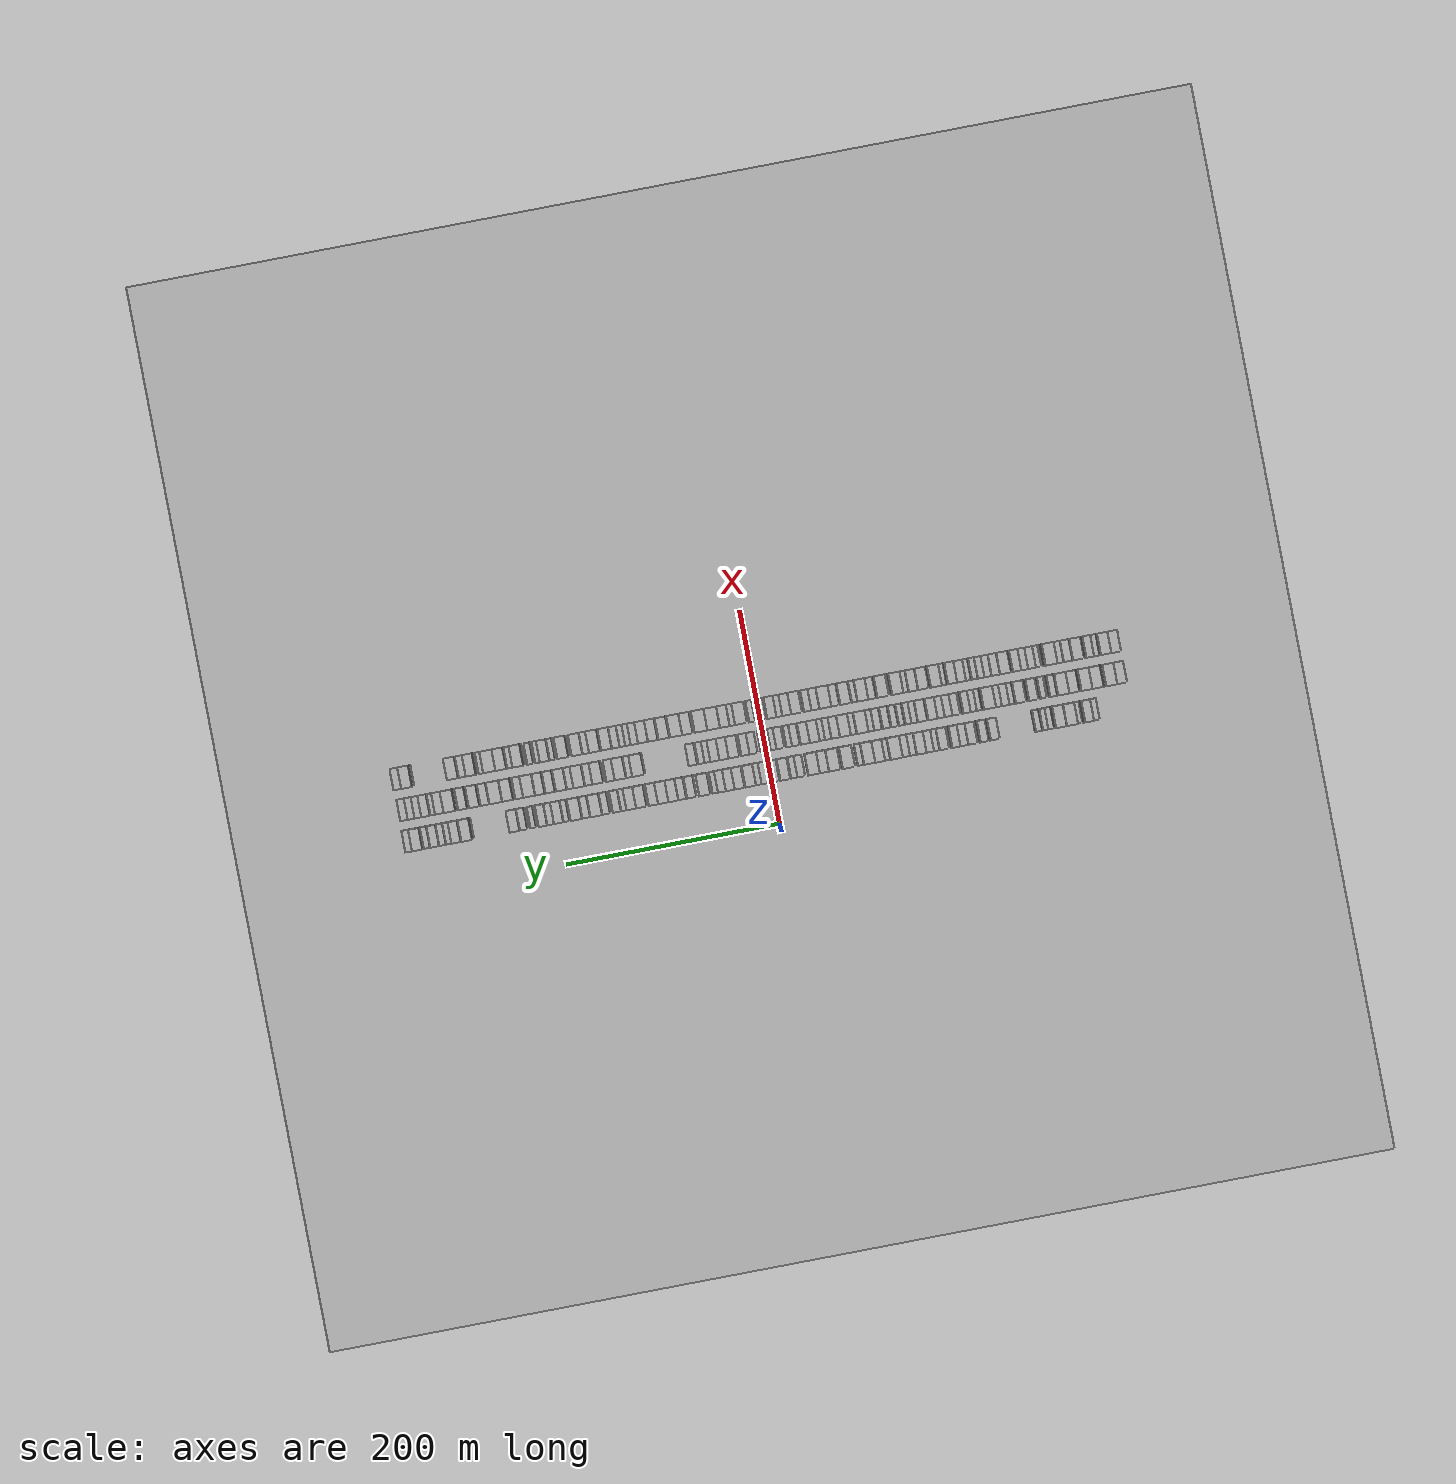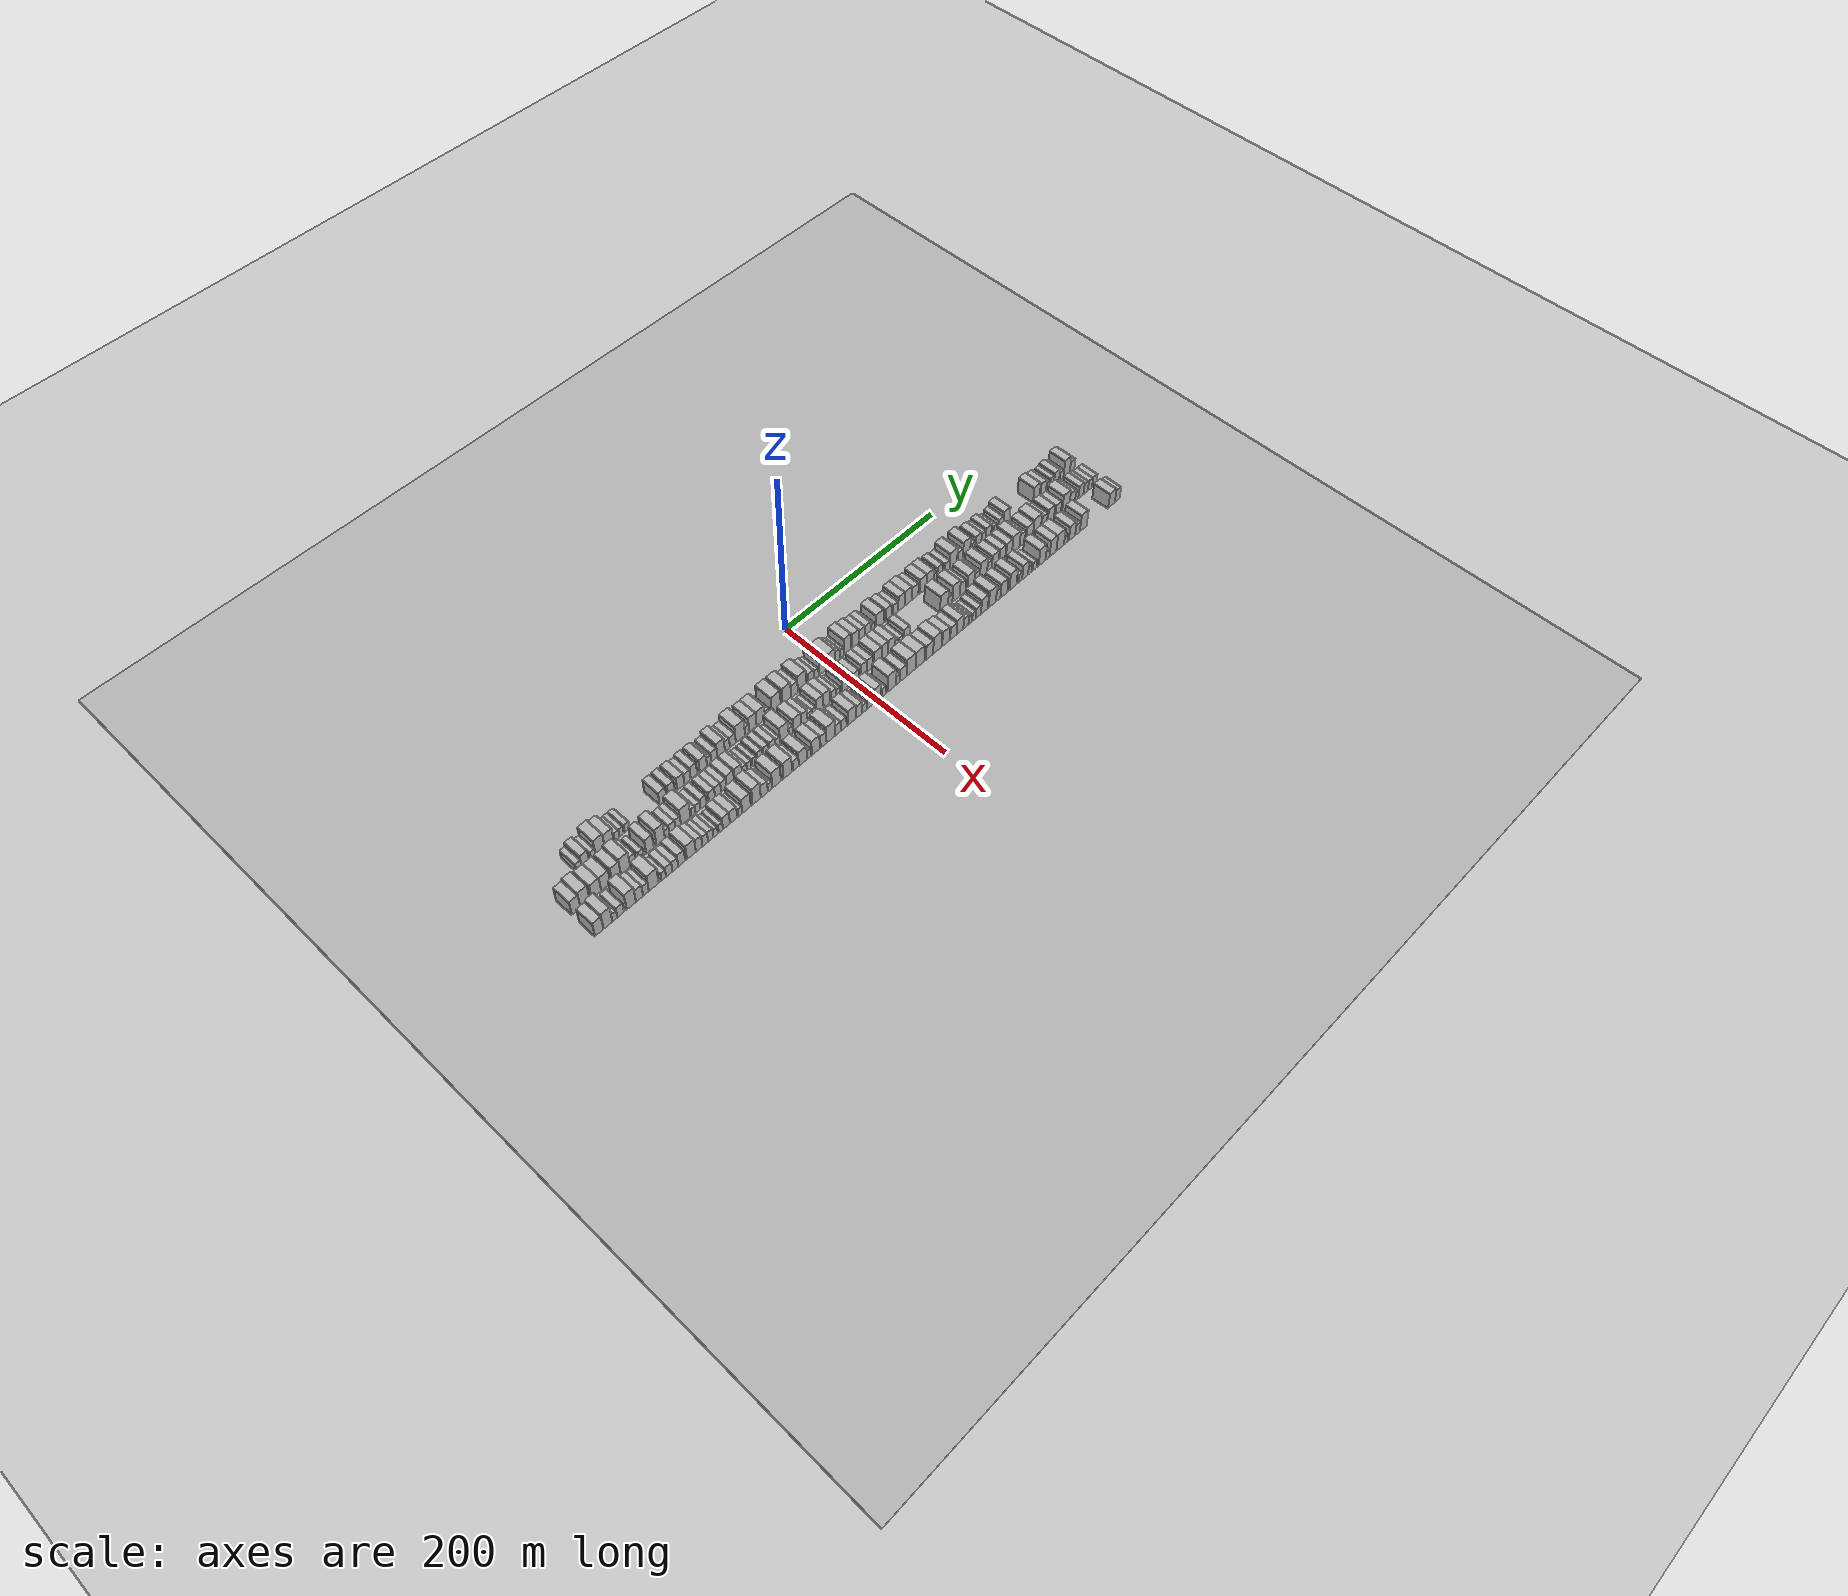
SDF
<?xml version="1.0" encoding="utf-8"?>

<sdf version="1.6">

   <world name="default">

      <gui fullscreen="0">

         <camera name="user_camera">

            <pose>-15 0 4.57585 0 0 0</pose>

            <view_controller>orbit</view_controller>

         </camera>

      </gui>

      <scene>

         <sky>

           <clouds>

             <speed>12</speed>

           </clouds>

         </sky>

         <ambient>0.4 0.4 0.4 1</ambient>

         <background>0.7 0.7 0.7 1</background>

         <shadows>1</shadows>

      </scene>

      <gravity>0 0 -9.8066</gravity>

      <magnetic_field>6e-06 2.3e-05 -4.2e-05</magnetic_field>

      <physics default="0" name="default_physics" type="ode">

         <ode>

            <solver>

               <type>quick</type>

               <iters>10</iters>

               <sor>1.0</sor>

               <use_dynamic_moi_rescaling>0</use_dynamic_moi_rescaling>

            </solver>

            <constraints>

               <cfm>0</cfm>

               <erp>0.2</erp>

               <contact_max_correcting_vel>100</contact_max_correcting_vel>

               <contact_surface_layer>0.001</contact_surface_layer>

            </constraints>

         </ode>

         <max_step_size>0.004</max_step_size>

         <real_time_factor>1</real_time_factor>

         <real_time_update_rate>250</real_time_update_rate>

      </physics>

      <light name="sun" type="directional">

         <cast_shadows>1</cast_shadows>

         <pose>0 0 10 0 0 0</pose>

         <diffuse>0.8 0.8 0.8 1</diffuse>

         <specular>0.2 0.2 0.2 1</specular>

         <attenuation>

            <range>1000</range>

            <constant>0.9</constant>

            <linear>0.01</linear>

            <quadratic>0.001</quadratic>

         </attenuation>

         <direction>-0.5 0.1 -0.9</direction>

      </light>

      <include>

         <name>ground_plane_1</name>

         <uri>model://HANNAS_ground_plane</uri>

         <pose>0 0 0  0 0 0</pose>

      </include>

      <include>

         <name>ground_plane_2</name>

         <uri>model://HANNAS_ground_plane</uri>

         <pose>100 0 0  0 0 0</pose>

      </include>

      <model name="building_1">

         <static>1</static>

         <pose frame="">50.0000 -303.0486 0 0.000000 0.000000 0.000000</pose>

         <link name="link">

            <pose frame="">0 0 6.00 0 0 0</pose>

            <collision name="collision">

               <geometry>

                  <box>

                     <size>20.0000 5.9676 12.0000</size>

                  </box>

               </geometry>

               <max_contacts>10</max_contacts>

               <surface>

                  <contact>

                     <ode/>

                  </contact>

                  <bounce/>

                  <friction>

                     <torsional>

                        <ode/>

                     </torsional>

                     <ode/>

                  </friction>

               </surface>

            </collision>

            <visual name="visual">

               <cast_shadows>0</cast_shadows>

               <geometry>

                  <box>

                     <size>20.0000 5.9676 12.0000</size>

                  </box>

               </geometry>

               <material>

                  <script>

                     <uri>model://HANNAS_wall/materials/scripts</uri>

                     <uri>model://HANNAS_wall/materials/textures</uri>

                     <name>vrc/HANNAS_wall</name>

                  </script>

               </material>

            </visual>

            <self_collide>0</self_collide>

            <enable_wind>0</enable_wind>

            <kinematic>0</kinematic>

         </link>

      </model>

      <model name="building_2">

         <static>1</static>

         <pose frame="">50.0000 -295.9503 0 0.000000 0.000000 0.000000</pose>

         <link name="link">

            <pose frame="">0 0 9.00 0 0 0</pose>

            <collision name="collision">

               <geometry>

                  <box>

                     <size>20.0000 8.2292 18.0000</size>

                  </box>

               </geometry>

               <max_contacts>10</max_contacts>

               <surface>

                  <contact>

                     <ode/>

                  </contact>

                  <bounce/>

                  <friction>

                     <torsional>

                        <ode/>

                     </torsional>

                     <ode/>

                  </friction>

               </surface>

            </collision>

            <visual name="visual">

               <cast_shadows>0</cast_shadows>

               <geometry>

                  <box>

                     <size>20.0000 8.2292 18.0000</size>

                  </box>

               </geometry>

               <material>

                  <script>

                     <uri>model://HANNAS_wall/materials/scripts</uri>

                     <uri>model://HANNAS_wall/materials/textures</uri>

                     <name>vrc/HANNAS_wall</name>

                  </script>

               </material>

            </visual>

            <self_collide>0</self_collide>

            <enable_wind>0</enable_wind>

            <kinematic>0</kinematic>

         </link>

      </model>

      <model name="building_3">

         <static>1</static>

         <pose frame="">50.0000 -287.1823 0 0.000000 0.000000 0.000000</pose>

         <link name="link">

            <pose frame="">0 0 6.00 0 0 0</pose>

            <collision name="collision">

               <geometry>

                  <box>

                     <size>20.0000 5.3067 12.0000</size>

                  </box>

               </geometry>

               <max_contacts>10</max_contacts>

               <surface>

                  <contact>

                     <ode/>

                  </contact>

                  <bounce/>

                  <friction>

                     <torsional>

                        <ode/>

                     </torsional>

                     <ode/>

                  </friction>

               </surface>

            </collision>

            <visual name="visual">

               <cast_shadows>0</cast_shadows>

               <geometry>

                  <box>

                     <size>20.0000 5.3067 12.0000</size>

                  </box>

               </geometry>

               <material>

                  <script>

                     <uri>model://HANNAS_wall/materials/scripts</uri>

                     <uri>model://HANNAS_wall/materials/textures</uri>

                     <name>vrc/HANNAS_wall</name>

                  </script>

               </material>

            </visual>

            <self_collide>0</self_collide>

            <enable_wind>0</enable_wind>

            <kinematic>0</kinematic>

         </link>

      </model>

      <model name="building_4">

         <static>1</static>

         <pose frame="">50.0000 -279.3959 0 0.000000 0.000000 0.000000</pose>

         <link name="link">

            <pose frame="">0 0 12.00 0 0 0</pose>

            <collision name="collision">

               <geometry>

                  <box>

                     <size>20.0000 10.2663 24.0000</size>

                  </box>

               </geometry>

               <max_contacts>10</max_contacts>

               <surface>

                  <contact>

                     <ode/>

                  </contact>

                  <bounce/>

                  <friction>

                     <torsional>

                        <ode/>

                     </torsional>

                     <ode/>

                  </friction>

               </surface>

            </collision>

            <visual name="visual">

               <cast_shadows>0</cast_shadows>

               <geometry>

                  <box>

                     <size>20.0000 10.2663 24.0000</size>

                  </box>

               </geometry>

               <material>

                  <script>

                     <uri>model://HANNAS_wall/materials/scripts</uri>

                     <uri>model://HANNAS_wall/materials/textures</uri>

                     <name>vrc/HANNAS_wall</name>

                  </script>

               </material>

            </visual>

            <self_collide>0</self_collide>

            <enable_wind>0</enable_wind>

            <kinematic>0</kinematic>

         </link>

      </model>

      <model name="building_5">

         <static>1</static>

         <pose frame="">50.0000 -269.2854 0 0.000000 0.000000 0.000000</pose>

         <link name="link">

            <pose frame="">0 0 10.50 0 0 0</pose>

            <collision name="collision">

               <geometry>

                  <box>

                     <size>20.0000 9.9546 21.0000</size>

                  </box>

               </geometry>

               <max_contacts>10</max_contacts>

               <surface>

                  <contact>

                     <ode/>

                  </contact>

                  <bounce/>

                  <friction>

                     <torsional>

                        <ode/>

                     </torsional>

                     <ode/>

                  </friction>

               </surface>

            </collision>

            <visual name="visual">

               <cast_shadows>0</cast_shadows>

               <geometry>

                  <box>

                     <size>20.0000 9.9546 21.0000</size>

                  </box>

               </geometry>

               <material>

                  <script>

                     <uri>model://HANNAS_wall/materials/scripts</uri>

                     <uri>model://HANNAS_wall/materials/textures</uri>

                     <name>vrc/HANNAS_wall</name>

                  </script>

               </material>

            </visual>

            <self_collide>0</self_collide>

            <enable_wind>0</enable_wind>

            <kinematic>0</kinematic>

         </link>

      </model>

      <model name="building_6">

         <static>1</static>

         <pose frame="">50.0000 -260.6441 0 0.000000 0.000000 0.000000</pose>

         <link name="link">

            <pose frame="">0 0 6.00 0 0 0</pose>

            <collision name="collision">

               <geometry>

                  <box>

                     <size>20.0000 5.3280 12.0000</size>

                  </box>

               </geometry>

               <max_contacts>10</max_contacts>

               <surface>

                  <contact>

                     <ode/>

                  </contact>

                  <bounce/>

                  <friction>

                     <torsional>

                        <ode/>

                     </torsional>

                     <ode/>

                  </friction>

               </surface>

            </collision>

            <visual name="visual">

               <cast_shadows>0</cast_shadows>

               <geometry>

                  <box>

                     <size>20.0000 5.3280 12.0000</size>

                  </box>

               </geometry>

               <material>

                  <script>

                     <uri>model://HANNAS_wall/materials/scripts</uri>

                     <uri>model://HANNAS_wall/materials/textures</uri>

                     <name>vrc/HANNAS_wall</name>

                  </script>

               </material>

            </visual>

            <self_collide>0</self_collide>

            <enable_wind>0</enable_wind>

            <kinematic>0</kinematic>

         </link>

      </model>

      <model name="building_7">

         <static>1</static>

         <pose frame="">50.0000 -255.5256 0 0.000000 0.000000 0.000000</pose>

         <link name="link">

            <pose frame="">0 0 6.00 0 0 0</pose>

            <collision name="collision">

               <geometry>

                  <box>

                     <size>20.0000 4.9091 12.0000</size>

                  </box>

               </geometry>

               <max_contacts>10</max_contacts>

               <surface>

                  <contact>

                     <ode/>

                  </contact>

                  <bounce/>

                  <friction>

                     <torsional>

                        <ode/>

                     </torsional>

                     <ode/>

                  </friction>

               </surface>

            </collision>

            <visual name="visual">

               <cast_shadows>0</cast_shadows>

               <geometry>

                  <box>

                     <size>20.0000 4.9091 12.0000</size>

                  </box>

               </geometry>

               <material>

                  <script>

                     <uri>model://HANNAS_wall/materials/scripts</uri>

                     <uri>model://HANNAS_wall/materials/textures</uri>

                     <name>vrc/HANNAS_wall</name>

                  </script>

               </material>

            </visual>

            <self_collide>0</self_collide>

            <enable_wind>0</enable_wind>

            <kinematic>0</kinematic>

         </link>

      </model>

      <model name="building_8">

         <static>1</static>

         <pose frame="">50.0000 -249.2155 0 0.000000 0.000000 0.000000</pose>

         <link name="link">

            <pose frame="">0 0 6.00 0 0 0</pose>

            <collision name="collision">

               <geometry>

                  <box>

                     <size>20.0000 5.7110 12.0000</size>

                  </box>

               </geometry>

               <max_contacts>10</max_contacts>

               <surface>

                  <contact>

                     <ode/>

                  </contact>

                  <bounce/>

                  <friction>

                     <torsional>

                        <ode/>

                     </torsional>

                     <ode/>

                  </friction>

               </surface>

            </collision>

            <visual name="visual">

               <cast_shadows>0</cast_shadows>

               <geometry>

                  <box>

                     <size>20.0000 5.7110 12.0000</size>

                  </box>

               </geometry>

               <material>

                  <script>

                     <uri>model://HANNAS_wall/materials/scripts</uri>

                     <uri>model://HANNAS_wall/materials/textures</uri>

                     <name>vrc/HANNAS_wall</name>

                  </script>

               </material>

            </visual>

            <self_collide>0</self_collide>

            <enable_wind>0</enable_wind>

            <kinematic>0</kinematic>

         </link>

      </model>

      <model name="building_9">

         <static>1</static>

         <pose frame="">50.0000 -207.9036 0 0.000000 0.000000 0.000000</pose>

         <link name="link">

            <pose frame="">0 0 9.00 0 0 0</pose>

            <collision name="collision">

               <geometry>

                  <box>

                     <size>20.0000 8.3043 18.0000</size>

                  </box>

               </geometry>

               <max_contacts>10</max_contacts>

               <surface>

                  <contact>

                     <ode/>

                  </contact>

                  <bounce/>

                  <friction>

                     <torsional>

                        <ode/>

                     </torsional>

                     <ode/>

                  </friction>

               </surface>

            </collision>

            <visual name="visual">

               <cast_shadows>0</cast_shadows>

               <geometry>

                  <box>

                     <size>20.0000 8.3043 18.0000</size>

                  </box>

               </geometry>

               <material>

                  <script>

                     <uri>model://HANNAS_wall/materials/scripts</uri>

                     <uri>model://HANNAS_wall/materials/textures</uri>

                     <name>vrc/HANNAS_wall</name>

                  </script>

               </material>

            </visual>

            <self_collide>0</self_collide>

            <enable_wind>0</enable_wind>

            <kinematic>0</kinematic>

         </link>

      </model>

      <model name="building_10">

         <static>1</static>

         <pose frame="">50.0000 -198.0247 0 0.000000 0.000000 0.000000</pose>

         <link name="link">

            <pose frame="">0 0 9.00 0 0 0</pose>

            <collision name="collision">

               <geometry>

                  <box>

                     <size>20.0000 7.4536 18.0000</size>

                  </box>

               </geometry>

               <max_contacts>10</max_contacts>

               <surface>

                  <contact>

                     <ode/>

                  </contact>

                  <bounce/>

                  <friction>

                     <torsional>

                        <ode/>

                     </torsional>

                     <ode/>

                  </friction>

               </surface>

            </collision>

            <visual name="visual">

               <cast_shadows>0</cast_shadows>

               <geometry>

                  <box>

                     <size>20.0000 7.4536 18.0000</size>

                  </box>

               </geometry>

               <material>

                  <script>

                     <uri>model://HANNAS_wall/materials/scripts</uri>

                     <uri>model://HANNAS_wall/materials/textures</uri>

                     <name>vrc/HANNAS_wall</name>

                  </script>

               </material>

            </visual>

            <self_collide>0</self_collide>

            <enable_wind>0</enable_wind>

            <kinematic>0</kinematic>

         </link>

      </model>

      <model name="building_11">

         <static>1</static>

         <pose frame="">50.0000 -187.1079 0 0.000000 0.000000 0.000000</pose>

         <link name="link">

            <pose frame="">0 0 9.00 0 0 0</pose>

            <collision name="collision">

               <geometry>

                  <box>

                     <size>20.0000 8.3798 18.0000</size>

                  </box>

               </geometry>

               <max_contacts>10</max_contacts>

               <surface>

                  <contact>

                     <ode/>

                  </contact>

                  <bounce/>

                  <friction>

                     <torsional>

                        <ode/>

                     </torsional>

                     <ode/>

                  </friction>

               </surface>

            </collision>

            <visual name="visual">

               <cast_shadows>0</cast_shadows>

               <geometry>

                  <box>

                     <size>20.0000 8.3798 18.0000</size>

                  </box>

               </geometry>

               <material>

                  <script>

                     <uri>model://HANNAS_wall/materials/scripts</uri>

                     <uri>model://HANNAS_wall/materials/textures</uri>

                     <name>vrc/HANNAS_wall</name>

                  </script>

               </material>

            </visual>

            <self_collide>0</self_collide>

            <enable_wind>0</enable_wind>

            <kinematic>0</kinematic>

         </link>

      </model>

      <model name="building_12">

         <static>1</static>

         <pose frame="">50.0000 -179.1790 0 0.000000 0.000000 0.000000</pose>

         <link name="link">

            <pose frame="">0 0 7.50 0 0 0</pose>

            <collision name="collision">

               <geometry>

                  <box>

                     <size>20.0000 7.4780 15.0000</size>

                  </box>

               </geometry>

               <max_contacts>10</max_contacts>

               <surface>

                  <contact>

                     <ode/>

                  </contact>

                  <bounce/>

                  <friction>

                     <torsional>

                        <ode/>

                     </torsional>

                     <ode/>

                  </friction>

               </surface>

            </collision>

            <visual name="visual">

               <cast_shadows>0</cast_shadows>

               <geometry>

                  <box>

                     <size>20.0000 7.4780 15.0000</size>

                  </box>

               </geometry>

               <material>

                  <script>

                     <uri>model://HANNAS_wall/materials/scripts</uri>

                     <uri>model://HANNAS_wall/materials/textures</uri>

                     <name>vrc/HANNAS_wall</name>

                  </script>

               </material>

            </visual>

            <self_collide>0</self_collide>

            <enable_wind>0</enable_wind>

            <kinematic>0</kinematic>

         </link>

      </model>

      <model name="building_13">

         <static>1</static>

         <pose frame="">50.0000 -171.6439 0 0.000000 0.000000 0.000000</pose>

         <link name="link">

            <pose frame="">0 0 9.00 0 0 0</pose>

            <collision name="collision">

               <geometry>

                  <box>

                     <size>20.0000 7.5922 18.0000</size>

                  </box>

               </geometry>

               <max_contacts>10</max_contacts>

               <surface>

                  <contact>

                     <ode/>

                  </contact>

                  <bounce/>

                  <friction>

                     <torsional>

                        <ode/>

                     </torsional>

                     <ode/>

                  </friction>

               </surface>

            </collision>

            <visual name="visual">

               <cast_shadows>0</cast_shadows>

               <geometry>

                  <box>

                     <size>20.0000 7.5922 18.0000</size>

                  </box>

               </geometry>

               <material>

                  <script>

                     <uri>model://HANNAS_wall/materials/scripts</uri>

                     <uri>model://HANNAS_wall/materials/textures</uri>

                     <name>vrc/HANNAS_wall</name>

                  </script>

               </material>

            </visual>

            <self_collide>0</self_collide>

            <enable_wind>0</enable_wind>

            <kinematic>0</kinematic>

         </link>

      </model>

      <model name="building_14">

         <static>1</static>

         <pose frame="">50.0000 -160.4778 0 0.000000 0.000000 0.000000</pose>

         <link name="link">

            <pose frame="">0 0 9.00 0 0 0</pose>

            <collision name="collision">

               <geometry>

                  <box>

                     <size>20.0000 8.7401 18.0000</size>

                  </box>

               </geometry>

               <max_contacts>10</max_contacts>

               <surface>

                  <contact>

                     <ode/>

                  </contact>

                  <bounce/>

                  <friction>

                     <torsional>

                        <ode/>

                     </torsional>

                     <ode/>

                  </friction>

               </surface>

            </collision>

            <visual name="visual">

               <cast_shadows>0</cast_shadows>

               <geometry>

                  <box>

                     <size>20.0000 8.7401 18.0000</size>

                  </box>

               </geometry>

               <material>

                  <script>

                     <uri>model://HANNAS_wall/materials/scripts</uri>

                     <uri>model://HANNAS_wall/materials/textures</uri>

                     <name>vrc/HANNAS_wall</name>

                  </script>

               </material>

            </visual>

            <self_collide>0</self_collide>

            <enable_wind>0</enable_wind>

            <kinematic>0</kinematic>

         </link>

      </model>

      <model name="building_15">

         <static>1</static>

         <pose frame="">50.0000 -153.5049 0 0.000000 0.000000 0.000000</pose>

         <link name="link">

            <pose frame="">0 0 6.00 0 0 0</pose>

            <collision name="collision">

               <geometry>

                  <box>

                     <size>20.0000 5.2057 12.0000</size>

                  </box>

               </geometry>

               <max_contacts>10</max_contacts>

               <surface>

                  <contact>

                     <ode/>

                  </contact>

                  <bounce/>

                  <friction>

                     <torsional>

                        <ode/>

                     </torsional>

                     <ode/>

                  </friction>

               </surface>

            </collision>

            <visual name="visual">

               <cast_shadows>0</cast_shadows>

               <geometry>

                  <box>

                     <size>20.0000 5.2057 12.0000</size>

                  </box>

               </geometry>

               <material>

                  <script>

                     <uri>model://HANNAS_wall/materials/scripts</uri>

                     <uri>model://HANNAS_wall/materials/textures</uri>

                     <name>vrc/HANNAS_wall</name>

                  </script>

               </material>

            </visual>

            <self_collide>0</self_collide>

            <enable_wind>0</enable_wind>

            <kinematic>0</kinematic>

         </link>

      </model>

      <model name="building_16">

         <static>1</static>

         <pose frame="">50.0000 -147.2780 0 0.000000 0.000000 0.000000</pose>

         <link name="link">

            <pose frame="">0 0 7.50 0 0 0</pose>

            <collision name="collision">

               <geometry>

                  <box>

                     <size>20.0000 7.2481 15.0000</size>

                  </box>

               </geometry>

               <max_contacts>10</max_contacts>

               <surface>

                  <contact>

                     <ode/>

                  </contact>

                  <bounce/>

                  <friction>

                     <torsional>

                        <ode/>

                     </torsional>

                     <ode/>

                  </friction>

               </surface>

            </collision>

            <visual name="visual">

               <cast_shadows>0</cast_shadows>

               <geometry>

                  <box>

                     <size>20.0000 7.2481 15.0000</size>

                  </box>

               </geometry>

               <material>

                  <script>

                     <uri>model://HANNAS_wall/materials/scripts</uri>

                     <uri>model://HANNAS_wall/materials/textures</uri>

                     <name>vrc/HANNAS_wall</name>

                  </script>

               </material>

            </visual>

            <self_collide>0</self_collide>

            <enable_wind>0</enable_wind>

            <kinematic>0</kinematic>

         </link>

      </model>

      <model name="building_17">

         <static>1</static>

         <pose frame="">50.0000 -139.1223 0 0.000000 0.000000 0.000000</pose>

         <link name="link">

            <pose frame="">0 0 10.50 0 0 0</pose>

            <collision name="collision">

               <geometry>

                  <box>

                     <size>20.0000 9.0632 21.0000</size>

                  </box>

               </geometry>

               <max_contacts>10</max_contacts>

               <surface>

                  <contact>

                     <ode/>

                  </contact>

                  <bounce/>

                  <friction>

                     <torsional>

                        <ode/>

                     </torsional>

                     <ode/>

                  </friction>

               </surface>

            </collision>

            <visual name="visual">

               <cast_shadows>0</cast_shadows>

               <geometry>

                  <box>

                     <size>20.0000 9.0632 21.0000</size>

                  </box>

               </geometry>

               <material>

                  <script>

                     <uri>model://HANNAS_wall/materials/scripts</uri>

                     <uri>model://HANNAS_wall/materials/textures</uri>

                     <name>vrc/HANNAS_wall</name>

                  </script>

               </material>

            </visual>

            <self_collide>0</self_collide>

            <enable_wind>0</enable_wind>

            <kinematic>0</kinematic>

         </link>

      </model>

      <model name="building_18">

         <static>1</static>

         <pose frame="">50.0000 -131.5241 0 0.000000 0.000000 0.000000</pose>

         <link name="link">

            <pose frame="">0 0 7.50 0 0 0</pose>

            <collision name="collision">

               <geometry>

                  <box>

                     <size>20.0000 6.1332 15.0000</size>

                  </box>

               </geometry>

               <max_contacts>10</max_contacts>

               <surface>

                  <contact>

                     <ode/>

                  </contact>

                  <bounce/>

                  <friction>

                     <torsional>

                        <ode/>

                     </torsional>

                     <ode/>

                  </friction>

               </surface>

            </collision>

            <visual name="visual">

               <cast_shadows>0</cast_shadows>

               <geometry>

                  <box>

                     <size>20.0000 6.1332 15.0000</size>

                  </box>

               </geometry>

               <material>

                  <script>

                     <uri>model://HANNAS_wall/materials/scripts</uri>

                     <uri>model://HANNAS_wall/materials/textures</uri>

                     <name>vrc/HANNAS_wall</name>

                  </script>

               </material>

            </visual>

            <self_collide>0</self_collide>

            <enable_wind>0</enable_wind>

            <kinematic>0</kinematic>

         </link>

      </model>

      <model name="building_19">

         <static>1</static>

         <pose frame="">50.0000 -124.9037 0 0.000000 0.000000 0.000000</pose>

         <link name="link">

            <pose frame="">0 0 7.50 0 0 0</pose>

            <collision name="collision">

               <geometry>

                  <box>

                     <size>20.0000 7.1077 15.0000</size>

                  </box>

               </geometry>

               <max_contacts>10</max_contacts>

               <surface>

                  <contact>

                     <ode/>

                  </contact>

                  <bounce/>

                  <friction>

                     <torsional>

                        <ode/>

                     </torsional>

                     <ode/>

                  </friction>

               </surface>

            </collision>

            <visual name="visual">

               <cast_shadows>0</cast_shadows>

               <geometry>

                  <box>

                     <size>20.0000 7.1077 15.0000</size>

                  </box>

               </geometry>

               <material>

                  <script>

                     <uri>model://HANNAS_wall/materials/scripts</uri>

                     <uri>model://HANNAS_wall/materials/textures</uri>

                     <name>vrc/HANNAS_wall</name>

                  </script>

               </material>

            </visual>

            <self_collide>0</self_collide>

            <enable_wind>0</enable_wind>

            <kinematic>0</kinematic>

         </link>

      </model>

      <model name="building_20">

         <static>1</static>

         <pose frame="">50.0000 -115.6766 0 0.000000 0.000000 0.000000</pose>

         <link name="link">

            <pose frame="">0 0 12.00 0 0 0</pose>

            <collision name="collision">

               <geometry>

                  <box>

                     <size>20.0000 11.3465 24.0000</size>

                  </box>

               </geometry>

               <max_contacts>10</max_contacts>

               <surface>

                  <contact>

                     <ode/>

                  </contact>

                  <bounce/>

                  <friction>

                     <torsional>

                        <ode/>

                     </torsional>

                     <ode/>

                  </friction>

               </surface>

            </collision>

            <visual name="visual">

               <cast_shadows>0</cast_shadows>

               <geometry>

                  <box>

                     <size>20.0000 11.3465 24.0000</size>

                  </box>

               </geometry>

               <material>

                  <script>

                     <uri>model://HANNAS_wall/materials/scripts</uri>

                     <uri>model://HANNAS_wall/materials/textures</uri>

                     <name>vrc/HANNAS_wall</name>

                  </script>

               </material>

            </visual>

            <self_collide>0</self_collide>

            <enable_wind>0</enable_wind>

            <kinematic>0</kinematic>

         </link>

      </model>

      <model name="building_21">

         <static>1</static>

         <pose frame="">50.0000 -107.4695 0 0.000000 0.000000 0.000000</pose>

         <link name="link">

            <pose frame="">0 0 6.00 0 0 0</pose>

            <collision name="collision">

               <geometry>

                  <box>

                     <size>20.0000 5.0677 12.0000</size>

                  </box>

               </geometry>

               <max_contacts>10</max_contacts>

               <surface>

                  <contact>

                     <ode/>

                  </contact>

                  <bounce/>

                  <friction>

                     <torsional>

                        <ode/>

                     </torsional>

                     <ode/>

                  </friction>

               </surface>

            </collision>

            <visual name="visual">

               <cast_shadows>0</cast_shadows>

               <geometry>

                  <box>

                     <size>20.0000 5.0677 12.0000</size>

                  </box>

               </geometry>

               <material>

                  <script>

                     <uri>model://HANNAS_wall/materials/scripts</uri>

                     <uri>model://HANNAS_wall/materials/textures</uri>

                     <name>vrc/HANNAS_wall</name>

                  </script>

               </material>

            </visual>

            <self_collide>0</self_collide>

            <enable_wind>0</enable_wind>

            <kinematic>0</kinematic>

         </link>

      </model>

      <model name="building_22">

         <static>1</static>

         <pose frame="">50.0000 -100.3512 0 0.000000 0.000000 0.000000</pose>

         <link name="link">

            <pose frame="">0 0 10.50 0 0 0</pose>

            <collision name="collision">

               <geometry>

                  <box>

                     <size>20.0000 9.1690 21.0000</size>

                  </box>

               </geometry>

               <max_contacts>10</max_contacts>

               <surface>

                  <contact>

                     <ode/>

                  </contact>

                  <bounce/>

                  <friction>

                     <torsional>

                        <ode/>

                     </torsional>

                     <ode/>

                  </friction>

               </surface>

            </collision>

            <visual name="visual">

               <cast_shadows>0</cast_shadows>

               <geometry>

                  <box>

                     <size>20.0000 9.1690 21.0000</size>

                  </box>

               </geometry>

               <material>

                  <script>

                     <uri>model://HANNAS_wall/materials/scripts</uri>

                     <uri>model://HANNAS_wall/materials/textures</uri>

                     <name>vrc/HANNAS_wall</name>

                  </script>

               </material>

            </visual>

            <self_collide>0</self_collide>

            <enable_wind>0</enable_wind>

            <kinematic>0</kinematic>

         </link>

      </model>

      <model name="building_23">

         <static>1</static>

         <pose frame="">50.0000 -90.5376 0 0.000000 0.000000 0.000000</pose>

         <link name="link">

            <pose frame="">0 0 10.50 0 0 0</pose>

            <collision name="collision">

               <geometry>

                  <box>

                     <size>20.0000 10.4582 21.0000</size>

                  </box>

               </geometry>

               <max_contacts>10</max_contacts>

               <surface>

                  <contact>

                     <ode/>

                  </contact>

                  <bounce/>

                  <friction>

                     <torsional>

                        <ode/>

                     </torsional>

                     <ode/>

                  </friction>

               </surface>

            </collision>

            <visual name="visual">

               <cast_shadows>0</cast_shadows>

               <geometry>

                  <box>

                     <size>20.0000 10.4582 21.0000</size>

                  </box>

               </geometry>

               <material>

                  <script>

                     <uri>model://HANNAS_wall/materials/scripts</uri>

                     <uri>model://HANNAS_wall/materials/textures</uri>

                     <name>vrc/HANNAS_wall</name>

                  </script>

               </material>

            </visual>

            <self_collide>0</self_collide>

            <enable_wind>0</enable_wind>

            <kinematic>0</kinematic>

         </link>

      </model>

      <model name="building_24">

         <static>1</static>

         <pose frame="">50.0000 -82.5647 0 0.000000 0.000000 0.000000</pose>

         <link name="link">

            <pose frame="">0 0 6.00 0 0 0</pose>

            <collision name="collision">

               <geometry>

                  <box>

                     <size>20.0000 5.4877 12.0000</size>

                  </box>

               </geometry>

               <max_contacts>10</max_contacts>

               <surface>

                  <contact>

                     <ode/>

                  </contact>

                  <bounce/>

                  <friction>

                     <torsional>

                        <ode/>

                     </torsional>

                     <ode/>

                  </friction>

               </surface>

            </collision>

            <visual name="visual">

               <cast_shadows>0</cast_shadows>

               <geometry>

                  <box>

                     <size>20.0000 5.4877 12.0000</size>

                  </box>

               </geometry>

               <material>

                  <script>

                     <uri>model://HANNAS_wall/materials/scripts</uri>

                     <uri>model://HANNAS_wall/materials/textures</uri>

                     <name>vrc/HANNAS_wall</name>

                  </script>

               </material>

            </visual>

            <self_collide>0</self_collide>

            <enable_wind>0</enable_wind>

            <kinematic>0</kinematic>

         </link>

      </model>

      <model name="building_25">

         <static>1</static>

         <pose frame="">50.0000 -71.1308 0 0.000000 0.000000 0.000000</pose>

         <link name="link">

            <pose frame="">0 0 12.00 0 0 0</pose>

            <collision name="collision">

               <geometry>

                  <box>

                     <size>20.0000 11.3801 24.0000</size>

                  </box>

               </geometry>

               <max_contacts>10</max_contacts>

               <surface>

                  <contact>

                     <ode/>

                  </contact>

                  <bounce/>

                  <friction>

                     <torsional>

                        <ode/>

                     </torsional>

                     <ode/>

                  </friction>

               </surface>

            </collision>

            <visual name="visual">

               <cast_shadows>0</cast_shadows>

               <geometry>

                  <box>

                     <size>20.0000 11.3801 24.0000</size>

                  </box>

               </geometry>

               <material>

                  <script>

                     <uri>model://HANNAS_wall/materials/scripts</uri>

                     <uri>model://HANNAS_wall/materials/textures</uri>

                     <name>vrc/HANNAS_wall</name>

                  </script>

               </material>

            </visual>

            <self_collide>0</self_collide>

            <enable_wind>0</enable_wind>

            <kinematic>0</kinematic>

         </link>

      </model>

      <model name="building_26">

         <static>1</static>

         <pose frame="">50.0000 -58.0494 0 0.000000 0.000000 0.000000</pose>

         <link name="link">

            <pose frame="">0 0 12.00 0 0 0</pose>

            <collision name="collision">

               <geometry>

                  <box>

                     <size>20.0000 10.7825 24.0000</size>

                  </box>

               </geometry>

               <max_contacts>10</max_contacts>

               <surface>

                  <contact>

                     <ode/>

                  </contact>

                  <bounce/>

                  <friction>

                     <torsional>

                        <ode/>

                     </torsional>

                     <ode/>

                  </friction>

               </surface>

            </collision>

            <visual name="visual">

               <cast_shadows>0</cast_shadows>

               <geometry>

                  <box>

                     <size>20.0000 10.7825 24.0000</size>

                  </box>

               </geometry>

               <material>

                  <script>

                     <uri>model://HANNAS_wall/materials/scripts</uri>

                     <uri>model://HANNAS_wall/materials/textures</uri>

                     <name>vrc/HANNAS_wall</name>

                  </script>

               </material>

            </visual>

            <self_collide>0</self_collide>

            <enable_wind>0</enable_wind>

            <kinematic>0</kinematic>

         </link>

      </model>

      <model name="building_27">

         <static>1</static>

         <pose frame="">50.0000 -48.3660 0 0.000000 0.000000 0.000000</pose>

         <link name="link">

            <pose frame="">0 0 9.00 0 0 0</pose>

            <collision name="collision">

               <geometry>

                  <box>

                     <size>20.0000 8.5843 18.0000</size>

                  </box>

               </geometry>

               <max_contacts>10</max_contacts>

               <surface>

                  <contact>

                     <ode/>

                  </contact>

                  <bounce/>

                  <friction>

                     <torsional>

                        <ode/>

                     </torsional>

                     <ode/>

                  </friction>

               </surface>

            </collision>

            <visual name="visual">

               <cast_shadows>0</cast_shadows>

               <geometry>

                  <box>

                     <size>20.0000 8.5843 18.0000</size>

                  </box>

               </geometry>

               <material>

                  <script>

                     <uri>model://HANNAS_wall/materials/scripts</uri>

                     <uri>model://HANNAS_wall/materials/textures</uri>

                     <name>vrc/HANNAS_wall</name>

                  </script>

               </material>

            </visual>

            <self_collide>0</self_collide>

            <enable_wind>0</enable_wind>

            <kinematic>0</kinematic>

         </link>

      </model>

      <model name="building_28">

         <static>1</static>

         <pose frame="">50.0000 -38.7281 0 0.000000 0.000000 0.000000</pose>

         <link name="link">

            <pose frame="">0 0 12.00 0 0 0</pose>

            <collision name="collision">

               <geometry>

                  <box>

                     <size>20.0000 10.6915 24.0000</size>

                  </box>

               </geometry>

               <max_contacts>10</max_contacts>

               <surface>

                  <contact>

                     <ode/>

                  </contact>

                  <bounce/>

                  <friction>

                     <torsional>

                        <ode/>

                     </torsional>

                     <ode/>

                  </friction>

               </surface>

            </collision>

            <visual name="visual">

               <cast_shadows>0</cast_shadows>

               <geometry>

                  <box>

                     <size>20.0000 10.6915 24.0000</size>

                  </box>

               </geometry>

               <material>

                  <script>

                     <uri>model://HANNAS_wall/materials/scripts</uri>

                     <uri>model://HANNAS_wall/materials/textures</uri>

                     <name>vrc/HANNAS_wall</name>

                  </script>

               </material>

            </visual>

            <self_collide>0</self_collide>

            <enable_wind>0</enable_wind>

            <kinematic>0</kinematic>

         </link>

      </model>

      <model name="building_29">

         <static>1</static>

         <pose frame="">50.0000 -26.8034 0 0.000000 0.000000 0.000000</pose>

         <link name="link">

            <pose frame="">0 0 7.50 0 0 0</pose>

            <collision name="collision">

               <geometry>

                  <box>

                     <size>20.0000 7.1579 15.0000</size>

                  </box>

               </geometry>

               <max_contacts>10</max_contacts>

               <surface>

                  <contact>

                     <ode/>

                  </contact>

                  <bounce/>

                  <friction>

                     <torsional>

                        <ode/>

                     </torsional>

                     <ode/>

                  </friction>

               </surface>

            </collision>

            <visual name="visual">

               <cast_shadows>0</cast_shadows>

               <geometry>

                  <box>

                     <size>20.0000 7.1579 15.0000</size>

                  </box>

               </geometry>

               <material>

                  <script>

                     <uri>model://HANNAS_wall/materials/scripts</uri>

                     <uri>model://HANNAS_wall/materials/textures</uri>

                     <name>vrc/HANNAS_wall</name>

                  </script>

               </material>

            </visual>

            <self_collide>0</self_collide>

            <enable_wind>0</enable_wind>

            <kinematic>0</kinematic>

         </link>

      </model>

      <model name="building_30">

         <static>1</static>

         <pose frame="">50.0000 -20.3374 0 0.000000 0.000000 0.000000</pose>

         <link name="link">

            <pose frame="">0 0 6.00 0 0 0</pose>

            <collision name="collision">

               <geometry>

                  <box>

                     <size>20.0000 5.7741 12.0000</size>

                  </box>

               </geometry>

               <max_contacts>10</max_contacts>

               <surface>

                  <contact>

                     <ode/>

                  </contact>

                  <bounce/>

                  <friction>

                     <torsional>

                        <ode/>

                     </torsional>

                     <ode/>

                  </friction>

               </surface>

            </collision>

            <visual name="visual">

               <cast_shadows>0</cast_shadows>

               <geometry>

                  <box>

                     <size>20.0000 5.7741 12.0000</size>

                  </box>

               </geometry>

               <material>

                  <script>

                     <uri>model://HANNAS_wall/materials/scripts</uri>

                     <uri>model://HANNAS_wall/materials/textures</uri>

                     <name>vrc/HANNAS_wall</name>

                  </script>

               </material>

            </visual>

            <self_collide>0</self_collide>

            <enable_wind>0</enable_wind>

            <kinematic>0</kinematic>

         </link>

      </model>

      <model name="building_31">

         <static>1</static>

         <pose frame="">50.0000 -11.9085 0 0.000000 0.000000 0.000000</pose>

         <link name="link">

            <pose frame="">0 0 10.50 0 0 0</pose>

            <collision name="collision">

               <geometry>

                  <box>

                     <size>20.0000 9.0835 21.0000</size>

                  </box>

               </geometry>

               <max_contacts>10</max_contacts>

               <surface>

                  <contact>

                     <ode/>

                  </contact>

                  <bounce/>

                  <friction>

                     <torsional>

                        <ode/>

                     </torsional>

                     <ode/>

                  </friction>

               </surface>

            </collision>

            <visual name="visual">

               <cast_shadows>0</cast_shadows>

               <geometry>

                  <box>

                     <size>20.0000 9.0835 21.0000</size>

                  </box>

               </geometry>

               <material>

                  <script>

                     <uri>model://HANNAS_wall/materials/scripts</uri>

                     <uri>model://HANNAS_wall/materials/textures</uri>

                     <name>vrc/HANNAS_wall</name>

                  </script>

               </material>

            </visual>

            <self_collide>0</self_collide>

            <enable_wind>0</enable_wind>

            <kinematic>0</kinematic>

         </link>

      </model>

      <model name="building_32">

         <static>1</static>

         <pose frame="">50.0000 -1.2948 0 0.000000 0.000000 0.000000</pose>

         <link name="link">

            <pose frame="">0 0 10.50 0 0 0</pose>

            <collision name="collision">

               <geometry>

                  <box>

                     <size>20.0000 10.1440 21.0000</size>

                  </box>

               </geometry>

               <max_contacts>10</max_contacts>

               <surface>

                  <contact>

                     <ode/>

                  </contact>

                  <bounce/>

                  <friction>

                     <torsional>

                        <ode/>

                     </torsional>

                     <ode/>

                  </friction>

               </surface>

            </collision>

            <visual name="visual">

               <cast_shadows>0</cast_shadows>

               <geometry>

                  <box>

                     <size>20.0000 10.1440 21.0000</size>

                  </box>

               </geometry>

               <material>

                  <script>

                     <uri>model://HANNAS_wall/materials/scripts</uri>

                     <uri>model://HANNAS_wall/materials/textures</uri>

                     <name>vrc/HANNAS_wall</name>

                  </script>

               </material>

            </visual>

            <self_collide>0</self_collide>

            <enable_wind>0</enable_wind>

            <kinematic>0</kinematic>

         </link>

      </model>

      <model name="building_33">

         <static>1</static>

         <pose frame="">50.0000 7.0367 0 0.000000 0.000000 0.000000</pose>

         <link name="link">

            <pose frame="">0 0 7.50 0 0 0</pose>

            <collision name="collision">

               <geometry>

                  <box>

                     <size>20.0000 6.5191 15.0000</size>

                  </box>

               </geometry>

               <max_contacts>10</max_contacts>

               <surface>

                  <contact>

                     <ode/>

                  </contact>

                  <bounce/>

                  <friction>

                     <torsional>

                        <ode/>

                     </torsional>

                     <ode/>

                  </friction>

               </surface>

            </collision>

            <visual name="visual">

               <cast_shadows>0</cast_shadows>

               <geometry>

                  <box>

                     <size>20.0000 6.5191 15.0000</size>

                  </box>

               </geometry>

               <material>

                  <script>

                     <uri>model://HANNAS_wall/materials/scripts</uri>

                     <uri>model://HANNAS_wall/materials/textures</uri>

                     <name>vrc/HANNAS_wall</name>

                  </script>

               </material>

            </visual>

            <self_collide>0</self_collide>

            <enable_wind>0</enable_wind>

            <kinematic>0</kinematic>

         </link>

      </model>

      <model name="building_34">

         <static>1</static>

         <pose frame="">50.0000 12.8875 0 0.000000 0.000000 0.000000</pose>

         <link name="link">

            <pose frame="">0 0 6.00 0 0 0</pose>

            <collision name="collision">

               <geometry>

                  <box>

                     <size>20.0000 5.1826 12.0000</size>

                  </box>

               </geometry>

               <max_contacts>10</max_contacts>

               <surface>

                  <contact>

                     <ode/>

                  </contact>

                  <bounce/>

                  <friction>

                     <torsional>

                        <ode/>

                     </torsional>

                     <ode/>

                  </friction>

               </surface>

            </collision>

            <visual name="visual">

               <cast_shadows>0</cast_shadows>

               <geometry>

                  <box>

                     <size>20.0000 5.1826 12.0000</size>

                  </box>

               </geometry>

               <material>

                  <script>

                     <uri>model://HANNAS_wall/materials/scripts</uri>

                     <uri>model://HANNAS_wall/materials/textures</uri>

                     <name>vrc/HANNAS_wall</name>

                  </script>

               </material>

            </visual>

            <self_collide>0</self_collide>

            <enable_wind>0</enable_wind>

            <kinematic>0</kinematic>

         </link>

      </model>

      <model name="building_35">

         <static>1</static>

         <pose frame="">50.0000 20.3388 0 0.000000 0.000000 0.000000</pose>

         <link name="link">

            <pose frame="">0 0 12.00 0 0 0</pose>

            <collision name="collision">

               <geometry>

                  <box>

                     <size>20.0000 9.7201 24.0000</size>

                  </box>

               </geometry>

               <max_contacts>10</max_contacts>

               <surface>

                  <contact>

                     <ode/>

                  </contact>

                  <bounce/>

                  <friction>

                     <torsional>

                        <ode/>

                     </torsional>

                     <ode/>

                  </friction>

               </surface>

            </collision>

            <visual name="visual">

               <cast_shadows>0</cast_shadows>

               <geometry>

                  <box>

                     <size>20.0000 9.7201 24.0000</size>

                  </box>

               </geometry>

               <material>

                  <script>

                     <uri>model://HANNAS_wall/materials/scripts</uri>

                     <uri>model://HANNAS_wall/materials/textures</uri>

                     <name>vrc/HANNAS_wall</name>

                  </script>

               </material>

            </visual>

            <self_collide>0</self_collide>

            <enable_wind>0</enable_wind>

            <kinematic>0</kinematic>

         </link>

      </model>

      <model name="building_36">

         <static>1</static>

         <pose frame="">50.0000 30.7863 0 0.000000 0.000000 0.000000</pose>

         <link name="link">

            <pose frame="">0 0 10.50 0 0 0</pose>

            <collision name="collision">

               <geometry>

                  <box>

                     <size>20.0000 9.1749 21.0000</size>

                  </box>

               </geometry>

               <max_contacts>10</max_contacts>

               <surface>

                  <contact>

                     <ode/>

                  </contact>

                  <bounce/>

                  <friction>

                     <torsional>

                        <ode/>

                     </torsional>

                     <ode/>

                  </friction>

               </surface>

            </collision>

            <visual name="visual">

               <cast_shadows>0</cast_shadows>

               <geometry>

                  <box>

                     <size>20.0000 9.1749 21.0000</size>

                  </box>

               </geometry>

               <material>

                  <script>

                     <uri>model://HANNAS_wall/materials/scripts</uri>

                     <uri>model://HANNAS_wall/materials/textures</uri>

                     <name>vrc/HANNAS_wall</name>

                  </script>

               </material>

            </visual>

            <self_collide>0</self_collide>

            <enable_wind>0</enable_wind>

            <kinematic>0</kinematic>

         </link>

      </model>

      <model name="building_37">

         <static>1</static>

         <pose frame="">50.0000 39.4990 0 0.000000 0.000000 0.000000</pose>

         <link name="link">

            <pose frame="">0 0 9.00 0 0 0</pose>

            <collision name="collision">

               <geometry>

                  <box>

                     <size>20.0000 8.2504 18.0000</size>

                  </box>

               </geometry>

               <max_contacts>10</max_contacts>

               <surface>

                  <contact>

                     <ode/>

                  </contact>

                  <bounce/>

                  <friction>

                     <torsional>

                        <ode/>

                     </torsional>

                     <ode/>

                  </friction>

               </surface>

            </collision>

            <visual name="visual">

               <cast_shadows>0</cast_shadows>

               <geometry>

                  <box>

                     <size>20.0000 8.2504 18.0000</size>

                  </box>

               </geometry>

               <material>

                  <script>

                     <uri>model://HANNAS_wall/materials/scripts</uri>

                     <uri>model://HANNAS_wall/materials/textures</uri>

                     <name>vrc/HANNAS_wall</name>

                  </script>

               </material>

            </visual>

            <self_collide>0</self_collide>

            <enable_wind>0</enable_wind>

            <kinematic>0</kinematic>

         </link>

      </model>

      <model name="building_38">

         <static>1</static>

         <pose frame="">50.0000 47.3485 0 0.000000 0.000000 0.000000</pose>

         <link name="link">

            <pose frame="">0 0 9.00 0 0 0</pose>

            <collision name="collision">

               <geometry>

                  <box>

                     <size>20.0000 7.4485 18.0000</size>

                  </box>

               </geometry>

               <max_contacts>10</max_contacts>

               <surface>

                  <contact>

                     <ode/>

                  </contact>

                  <bounce/>

                  <friction>

                     <torsional>

                        <ode/>

                     </torsional>

                     <ode/>

                  </friction>

               </surface>

            </collision>

            <visual name="visual">

               <cast_shadows>0</cast_shadows>

               <geometry>

                  <box>

                     <size>20.0000 7.4485 18.0000</size>

                  </box>

               </geometry>

               <material>

                  <script>

                     <uri>model://HANNAS_wall/materials/scripts</uri>

                     <uri>model://HANNAS_wall/materials/textures</uri>

                     <name>vrc/HANNAS_wall</name>

                  </script>

               </material>

            </visual>

            <self_collide>0</self_collide>

            <enable_wind>0</enable_wind>

            <kinematic>0</kinematic>

         </link>

      </model>

      <model name="building_39">

         <static>1</static>

         <pose frame="">50.0000 53.5620 0 0.000000 0.000000 0.000000</pose>

         <link name="link">

            <pose frame="">0 0 6.00 0 0 0</pose>

            <collision name="collision">

               <geometry>

                  <box>

                     <size>20.0000 4.9785 12.0000</size>

                  </box>

               </geometry>

               <max_contacts>10</max_contacts>

               <surface>

                  <contact>

                     <ode/>

                  </contact>

                  <bounce/>

                  <friction>

                     <torsional>

                        <ode/>

                     </torsional>

                     <ode/>

                  </friction>

               </surface>

            </collision>

            <visual name="visual">

               <cast_shadows>0</cast_shadows>

               <geometry>

                  <box>

                     <size>20.0000 4.9785 12.0000</size>

                  </box>

               </geometry>

               <material>

                  <script>

                     <uri>model://HANNAS_wall/materials/scripts</uri>

                     <uri>model://HANNAS_wall/materials/textures</uri>

                     <name>vrc/HANNAS_wall</name>

                  </script>

               </material>

            </visual>

            <self_collide>0</self_collide>

            <enable_wind>0</enable_wind>

            <kinematic>0</kinematic>

         </link>

      </model>

      <model name="building_40">

         <static>1</static>

         <pose frame="">50.0000 63.1879 0 0.000000 0.000000 0.000000</pose>

         <link name="link">

            <pose frame="">0 0 10.50 0 0 0</pose>

            <collision name="collision">

               <geometry>

                  <box>

                     <size>20.0000 10.2733 21.0000</size>

                  </box>

               </geometry>

               <max_contacts>10</max_contacts>

               <surface>

                  <contact>

                     <ode/>

                  </contact>

                  <bounce/>

                  <friction>

                     <torsional>

                        <ode/>

                     </torsional>

                     <ode/>

                  </friction>

               </surface>

            </collision>

            <visual name="visual">

               <cast_shadows>0</cast_shadows>

               <geometry>

                  <box>

                     <size>20.0000 10.2733 21.0000</size>

                  </box>

               </geometry>

               <material>

                  <script>

                     <uri>model://HANNAS_wall/materials/scripts</uri>

                     <uri>model://HANNAS_wall/materials/textures</uri>

                     <name>vrc/HANNAS_wall</name>

                  </script>

               </material>

            </visual>

            <self_collide>0</self_collide>

            <enable_wind>0</enable_wind>

            <kinematic>0</kinematic>

         </link>

      </model>

      <model name="building_41">

         <static>1</static>

         <pose frame="">50.0000 75.5066 0 0.000000 0.000000 0.000000</pose>

         <link name="link">

            <pose frame="">0 0 9.00 0 0 0</pose>

            <collision name="collision">

               <geometry>

                  <box>

                     <size>20.0000 8.3643 18.0000</size>

                  </box>

               </geometry>

               <max_contacts>10</max_contacts>

               <surface>

                  <contact>

                     <ode/>

                  </contact>

                  <bounce/>

                  <friction>

                     <torsional>

                        <ode/>

                     </torsional>

                     <ode/>

                  </friction>

               </surface>

            </collision>

            <visual name="visual">

               <cast_shadows>0</cast_shadows>

               <geometry>

                  <box>

                     <size>20.0000 8.3643 18.0000</size>

                  </box>

               </geometry>

               <material>

                  <script>

                     <uri>model://HANNAS_wall/materials/scripts</uri>

                     <uri>model://HANNAS_wall/materials/textures</uri>

                     <name>vrc/HANNAS_wall</name>

                  </script>

               </material>

            </visual>

            <self_collide>0</self_collide>

            <enable_wind>0</enable_wind>

            <kinematic>0</kinematic>

         </link>

      </model>

      <model name="building_42">

         <static>1</static>

         <pose frame="">50.0000 84.3368 0 0.000000 0.000000 0.000000</pose>

         <link name="link">

            <pose frame="">0 0 7.50 0 0 0</pose>

            <collision name="collision">

               <geometry>

                  <box>

                     <size>20.0000 7.2960 15.0000</size>

                  </box>

               </geometry>

               <max_contacts>10</max_contacts>

               <surface>

                  <contact>

                     <ode/>

                  </contact>

                  <bounce/>

                  <friction>

                     <torsional>

                        <ode/>

                     </torsional>

                     <ode/>

                  </friction>

               </surface>

            </collision>

            <visual name="visual">

               <cast_shadows>0</cast_shadows>

               <geometry>

                  <box>

                     <size>20.0000 7.2960 15.0000</size>

                  </box>

               </geometry>

               <material>

                  <script>

                     <uri>model://HANNAS_wall/materials/scripts</uri>

                     <uri>model://HANNAS_wall/materials/textures</uri>

                     <name>vrc/HANNAS_wall</name>

                  </script>

               </material>

            </visual>

            <self_collide>0</self_collide>

            <enable_wind>0</enable_wind>

            <kinematic>0</kinematic>

         </link>

      </model>

      <model name="building_43">

         <static>1</static>

         <pose frame="">50.0000 92.5315 0 0.000000 0.000000 0.000000</pose>

         <link name="link">

            <pose frame="">0 0 10.50 0 0 0</pose>

            <collision name="collision">

               <geometry>

                  <box>

                     <size>20.0000 9.0934 21.0000</size>

                  </box>

               </geometry>

               <max_contacts>10</max_contacts>

               <surface>

                  <contact>

                     <ode/>

                  </contact>

                  <bounce/>

                  <friction>

                     <torsional>

                        <ode/>

                     </torsional>

                     <ode/>

                  </friction>

               </surface>

            </collision>

            <visual name="visual">

               <cast_shadows>0</cast_shadows>

               <geometry>

                  <box>

                     <size>20.0000 9.0934 21.0000</size>

                  </box>

               </geometry>

               <material>

                  <script>

                     <uri>model://HANNAS_wall/materials/scripts</uri>

                     <uri>model://HANNAS_wall/materials/textures</uri>

                     <name>vrc/HANNAS_wall</name>

                  </script>

               </material>

            </visual>

            <self_collide>0</self_collide>

            <enable_wind>0</enable_wind>

            <kinematic>0</kinematic>

         </link>

      </model>

      <model name="building_44">

         <static>1</static>

         <pose frame="">50.0000 101.9800 0 0.000000 0.000000 0.000000</pose>

         <link name="link">

            <pose frame="">0 0 10.50 0 0 0</pose>

            <collision name="collision">

               <geometry>

                  <box>

                     <size>20.0000 9.8036 21.0000</size>

                  </box>

               </geometry>

               <max_contacts>10</max_contacts>

               <surface>

                  <contact>

                     <ode/>

                  </contact>

                  <bounce/>

                  <friction>

                     <torsional>

                        <ode/>

                     </torsional>

                     <ode/>

                  </friction>

               </surface>

            </collision>

            <visual name="visual">

               <cast_shadows>0</cast_shadows>

               <geometry>

                  <box>

                     <size>20.0000 9.8036 21.0000</size>

                  </box>

               </geometry>

               <material>

                  <script>

                     <uri>model://HANNAS_wall/materials/scripts</uri>

                     <uri>model://HANNAS_wall/materials/textures</uri>

                     <name>vrc/HANNAS_wall</name>

                  </script>

               </material>

            </visual>

            <self_collide>0</self_collide>

            <enable_wind>0</enable_wind>

            <kinematic>0</kinematic>

         </link>

      </model>

      <model name="building_45">

         <static>1</static>

         <pose frame="">50.0000 111.2178 0 0.000000 0.000000 0.000000</pose>

         <link name="link">

            <pose frame="">0 0 9.00 0 0 0</pose>

            <collision name="collision">

               <geometry>

                  <box>

                     <size>20.0000 8.6720 18.0000</size>

                  </box>

               </geometry>

               <max_contacts>10</max_contacts>

               <surface>

                  <contact>

                     <ode/>

                  </contact>

                  <bounce/>

                  <friction>

                     <torsional>

                        <ode/>

                     </torsional>

                     <ode/>

                  </friction>

               </surface>

            </collision>

            <visual name="visual">

               <cast_shadows>0</cast_shadows>

               <geometry>

                  <box>

                     <size>20.0000 8.6720 18.0000</size>

                  </box>

               </geometry>

               <material>

                  <script>

                     <uri>model://HANNAS_wall/materials/scripts</uri>

                     <uri>model://HANNAS_wall/materials/textures</uri>

                     <name>vrc/HANNAS_wall</name>

                  </script>

               </material>

            </visual>

            <self_collide>0</self_collide>

            <enable_wind>0</enable_wind>

            <kinematic>0</kinematic>

         </link>

      </model>

      <model name="building_46">

         <static>1</static>

         <pose frame="">50.0000 122.4304 0 0.000000 0.000000 0.000000</pose>

         <link name="link">

            <pose frame="">0 0 10.50 0 0 0</pose>

            <collision name="collision">

               <geometry>

                  <box>

                     <size>20.0000 9.7534 21.0000</size>

                  </box>

               </geometry>

               <max_contacts>10</max_contacts>

               <surface>

                  <contact>

                     <ode/>

                  </contact>

                  <bounce/>

                  <friction>

                     <torsional>

                        <ode/>

                     </torsional>

                     <ode/>

                  </friction>

               </surface>

            </collision>

            <visual name="visual">

               <cast_shadows>0</cast_shadows>

               <geometry>

                  <box>

                     <size>20.0000 9.7534 21.0000</size>

                  </box>

               </geometry>

               <material>

                  <script>

                     <uri>model://HANNAS_wall/materials/scripts</uri>

                     <uri>model://HANNAS_wall/materials/textures</uri>

                     <name>vrc/HANNAS_wall</name>

                  </script>

               </material>

            </visual>

            <self_collide>0</self_collide>

            <enable_wind>0</enable_wind>

            <kinematic>0</kinematic>

         </link>

      </model>

      <model name="building_47">

         <static>1</static>

         <pose frame="">50.0000 131.8109 0 0.000000 0.000000 0.000000</pose>

         <link name="link">

            <pose frame="">0 0 10.50 0 0 0</pose>

            <collision name="collision">

               <geometry>

                  <box>

                     <size>20.0000 9.0077 21.0000</size>

                  </box>

               </geometry>

               <max_contacts>10</max_contacts>

               <surface>

                  <contact>

                     <ode/>

                  </contact>

                  <bounce/>

                  <friction>

                     <torsional>

                        <ode/>

                     </torsional>

                     <ode/>

                  </friction>

               </surface>

            </collision>

            <visual name="visual">

               <cast_shadows>0</cast_shadows>

               <geometry>

                  <box>

                     <size>20.0000 9.0077 21.0000</size>

                  </box>

               </geometry>

               <material>

                  <script>

                     <uri>model://HANNAS_wall/materials/scripts</uri>

                     <uri>model://HANNAS_wall/materials/textures</uri>

                     <name>vrc/HANNAS_wall</name>

                  </script>

               </material>

            </visual>

            <self_collide>0</self_collide>

            <enable_wind>0</enable_wind>

            <kinematic>0</kinematic>

         </link>

      </model>

      <model name="building_48">

         <static>1</static>

         <pose frame="">50.0000 138.9734 0 0.000000 0.000000 0.000000</pose>

         <link name="link">

            <pose frame="">0 0 6.00 0 0 0</pose>

            <collision name="collision">

               <geometry>

                  <box>

                     <size>20.0000 5.3172 12.0000</size>

                  </box>

               </geometry>

               <max_contacts>10</max_contacts>

               <surface>

                  <contact>

                     <ode/>

                  </contact>

                  <bounce/>

                  <friction>

                     <torsional>

                        <ode/>

                     </torsional>

                     <ode/>

                  </friction>

               </surface>

            </collision>

            <visual name="visual">

               <cast_shadows>0</cast_shadows>

               <geometry>

                  <box>

                     <size>20.0000 5.3172 12.0000</size>

                  </box>

               </geometry>

               <material>

                  <script>

                     <uri>model://HANNAS_wall/materials/scripts</uri>

                     <uri>model://HANNAS_wall/materials/textures</uri>

                     <name>vrc/HANNAS_wall</name>

                  </script>

               </material>

            </visual>

            <self_collide>0</self_collide>

            <enable_wind>0</enable_wind>

            <kinematic>0</kinematic>

         </link>

      </model>

      <model name="building_49">

         <static>1</static>

         <pose frame="">50.0000 145.3596 0 0.000000 0.000000 0.000000</pose>

         <link name="link">

            <pose frame="">0 0 9.00 0 0 0</pose>

            <collision name="collision">

               <geometry>

                  <box>

                     <size>20.0000 7.4552 18.0000</size>

                  </box>

               </geometry>

               <max_contacts>10</max_contacts>

               <surface>

                  <contact>

                     <ode/>

                  </contact>

                  <bounce/>

                  <friction>

                     <torsional>

                        <ode/>

                     </torsional>

                     <ode/>

                  </friction>

               </surface>

            </collision>

            <visual name="visual">

               <cast_shadows>0</cast_shadows>

               <geometry>

                  <box>

                     <size>20.0000 7.4552 18.0000</size>

                  </box>

               </geometry>

               <material>

                  <script>

                     <uri>model://HANNAS_wall/materials/scripts</uri>

                     <uri>model://HANNAS_wall/materials/textures</uri>

                     <name>vrc/HANNAS_wall</name>

                  </script>

               </material>

            </visual>

            <self_collide>0</self_collide>

            <enable_wind>0</enable_wind>

            <kinematic>0</kinematic>

         </link>

      </model>

      <model name="building_50">

         <static>1</static>

         <pose frame="">50.0000 155.5371 0 0.000000 0.000000 0.000000</pose>

         <link name="link">

            <pose frame="">0 0 7.50 0 0 0</pose>

            <collision name="collision">

               <geometry>

                  <box>

                     <size>20.0000 6.8997 15.0000</size>

                  </box>

               </geometry>

               <max_contacts>10</max_contacts>

               <surface>

                  <contact>

                     <ode/>

                  </contact>

                  <bounce/>

                  <friction>

                     <torsional>

                        <ode/>

                     </torsional>

                     <ode/>

                  </friction>

               </surface>

            </collision>

            <visual name="visual">

               <cast_shadows>0</cast_shadows>

               <geometry>

                  <box>

                     <size>20.0000 6.8997 15.0000</size>

                  </box>

               </geometry>

               <material>

                  <script>

                     <uri>model://HANNAS_wall/materials/scripts</uri>

                     <uri>model://HANNAS_wall/materials/textures</uri>

                     <name>vrc/HANNAS_wall</name>

                  </script>

               </material>

            </visual>

            <self_collide>0</self_collide>

            <enable_wind>0</enable_wind>

            <kinematic>0</kinematic>

         </link>

      </model>

      <model name="building_51">

         <static>1</static>

         <pose frame="">50.0000 164.3028 0 0.000000 0.000000 0.000000</pose>

         <link name="link">

            <pose frame="">0 0 12.00 0 0 0</pose>

            <collision name="collision">

               <geometry>

                  <box>

                     <size>20.0000 10.6318 24.0000</size>

                  </box>

               </geometry>

               <max_contacts>10</max_contacts>

               <surface>

                  <contact>

                     <ode/>

                  </contact>

                  <bounce/>

                  <friction>

                     <torsional>

                        <ode/>

                     </torsional>

                     <ode/>

                  </friction>

               </surface>

            </collision>

            <visual name="visual">

               <cast_shadows>0</cast_shadows>

               <geometry>

                  <box>

                     <size>20.0000 10.6318 24.0000</size>

                  </box>

               </geometry>

               <material>

                  <script>

                     <uri>model://HANNAS_wall/materials/scripts</uri>

                     <uri>model://HANNAS_wall/materials/textures</uri>

                     <name>vrc/HANNAS_wall</name>

                  </script>

               </material>

            </visual>

            <self_collide>0</self_collide>

            <enable_wind>0</enable_wind>

            <kinematic>0</kinematic>

         </link>

      </model>

      <model name="building_52">

         <static>1</static>

         <pose frame="">50.0000 174.1626 0 0.000000 0.000000 0.000000</pose>

         <link name="link">

            <pose frame="">0 0 7.50 0 0 0</pose>

            <collision name="collision">

               <geometry>

                  <box>

                     <size>20.0000 7.0879 15.0000</size>

                  </box>

               </geometry>

               <max_contacts>10</max_contacts>

               <surface>

                  <contact>

                     <ode/>

                  </contact>

                  <bounce/>

                  <friction>

                     <torsional>

                        <ode/>

                     </torsional>

                     <ode/>

                  </friction>

               </surface>

            </collision>

            <visual name="visual">

               <cast_shadows>0</cast_shadows>

               <geometry>

                  <box>

                     <size>20.0000 7.0879 15.0000</size>

                  </box>

               </geometry>

               <material>

                  <script>

                     <uri>model://HANNAS_wall/materials/scripts</uri>

                     <uri>model://HANNAS_wall/materials/textures</uri>

                     <name>vrc/HANNAS_wall</name>

                  </script>

               </material>

            </visual>

            <self_collide>0</self_collide>

            <enable_wind>0</enable_wind>

            <kinematic>0</kinematic>

         </link>

      </model>

      <model name="building_53">

         <static>1</static>

         <pose frame="">50.0000 182.9408 0 0.000000 0.000000 0.000000</pose>

         <link name="link">

            <pose frame="">0 0 12.00 0 0 0</pose>

            <collision name="collision">

               <geometry>

                  <box>

                     <size>20.0000 10.4686 24.0000</size>

                  </box>

               </geometry>

               <max_contacts>10</max_contacts>

               <surface>

                  <contact>

                     <ode/>

                  </contact>

                  <bounce/>

                  <friction>

                     <torsional>

                        <ode/>

                     </torsional>

                     <ode/>

                  </friction>

               </surface>

            </collision>

            <visual name="visual">

               <cast_shadows>0</cast_shadows>

               <geometry>

                  <box>

                     <size>20.0000 10.4686 24.0000</size>

                  </box>

               </geometry>

               <material>

                  <script>

                     <uri>model://HANNAS_wall/materials/scripts</uri>

                     <uri>model://HANNAS_wall/materials/textures</uri>

                     <name>vrc/HANNAS_wall</name>

                  </script>

               </material>

            </visual>

            <self_collide>0</self_collide>

            <enable_wind>0</enable_wind>

            <kinematic>0</kinematic>

         </link>

      </model>

      <model name="building_54">

         <static>1</static>

         <pose frame="">50.0000 192.8291 0 0.000000 0.000000 0.000000</pose>

         <link name="link">

            <pose frame="">0 0 6.00 0 0 0</pose>

            <collision name="collision">

               <geometry>

                  <box>

                     <size>20.0000 5.3079 12.0000</size>

                  </box>

               </geometry>

               <max_contacts>10</max_contacts>

               <surface>

                  <contact>

                     <ode/>

                  </contact>

                  <bounce/>

                  <friction>

                     <torsional>

                        <ode/>

                     </torsional>

                     <ode/>

                  </friction>

               </surface>

            </collision>

            <visual name="visual">

               <cast_shadows>0</cast_shadows>

               <geometry>

                  <box>

                     <size>20.0000 5.3079 12.0000</size>

                  </box>

               </geometry>

               <material>

                  <script>

                     <uri>model://HANNAS_wall/materials/scripts</uri>

                     <uri>model://HANNAS_wall/materials/textures</uri>

                     <name>vrc/HANNAS_wall</name>

                  </script>

               </material>

            </visual>

            <self_collide>0</self_collide>

            <enable_wind>0</enable_wind>

            <kinematic>0</kinematic>

         </link>

      </model>

      <model name="building_55">

         <static>1</static>

         <pose frame="">50.0000 199.7881 0 0.000000 0.000000 0.000000</pose>

         <link name="link">

            <pose frame="">0 0 9.00 0 0 0</pose>

            <collision name="collision">

               <geometry>

                  <box>

                     <size>20.0000 8.6101 18.0000</size>

                  </box>

               </geometry>

               <max_contacts>10</max_contacts>

               <surface>

                  <contact>

                     <ode/>

                  </contact>

                  <bounce/>

                  <friction>

                     <torsional>

                        <ode/>

                     </torsional>

                     <ode/>

                  </friction>

               </surface>

            </collision>

            <visual name="visual">

               <cast_shadows>0</cast_shadows>

               <geometry>

                  <box>

                     <size>20.0000 8.6101 18.0000</size>

                  </box>

               </geometry>

               <material>

                  <script>

                     <uri>model://HANNAS_wall/materials/scripts</uri>

                     <uri>model://HANNAS_wall/materials/textures</uri>

                     <name>vrc/HANNAS_wall</name>

                  </script>

               </material>

            </visual>

            <self_collide>0</self_collide>

            <enable_wind>0</enable_wind>

            <kinematic>0</kinematic>

         </link>

      </model>

      <model name="building_56">

         <static>1</static>

         <pose frame="">50.0000 207.3334 0 0.000000 0.000000 0.000000</pose>

         <link name="link">

            <pose frame="">0 0 7.50 0 0 0</pose>

            <collision name="collision">

               <geometry>

                  <box>

                     <size>20.0000 6.4805 15.0000</size>

                  </box>

               </geometry>

               <max_contacts>10</max_contacts>

               <surface>

                  <contact>

                     <ode/>

                  </contact>

                  <bounce/>

                  <friction>

                     <torsional>

                        <ode/>

                     </torsional>

                     <ode/>

                  </friction>

               </surface>

            </collision>

            <visual name="visual">

               <cast_shadows>0</cast_shadows>

               <geometry>

                  <box>

                     <size>20.0000 6.4805 15.0000</size>

                  </box>

               </geometry>

               <material>

                  <script>

                     <uri>model://HANNAS_wall/materials/scripts</uri>

                     <uri>model://HANNAS_wall/materials/textures</uri>

                     <name>vrc/HANNAS_wall</name>

                  </script>

               </material>

            </visual>

            <self_collide>0</self_collide>

            <enable_wind>0</enable_wind>

            <kinematic>0</kinematic>

         </link>

      </model>

      <model name="building_57">

         <static>1</static>

         <pose frame="">50.0000 214.4789 0 0.000000 0.000000 0.000000</pose>

         <link name="link">

            <pose frame="">0 0 9.00 0 0 0</pose>

            <collision name="collision">

               <geometry>

                  <box>

                     <size>20.0000 7.8107 18.0000</size>

                  </box>

               </geometry>

               <max_contacts>10</max_contacts>

               <surface>

                  <contact>

                     <ode/>

                  </contact>

                  <bounce/>

                  <friction>

                     <torsional>

                        <ode/>

                     </torsional>

                     <ode/>

                  </friction>

               </surface>

            </collision>

            <visual name="visual">

               <cast_shadows>0</cast_shadows>

               <geometry>

                  <box>

                     <size>20.0000 7.8107 18.0000</size>

                  </box>

               </geometry>

               <material>

                  <script>

                     <uri>model://HANNAS_wall/materials/scripts</uri>

                     <uri>model://HANNAS_wall/materials/textures</uri>

                     <name>vrc/HANNAS_wall</name>

                  </script>

               </material>

            </visual>

            <self_collide>0</self_collide>

            <enable_wind>0</enable_wind>

            <kinematic>0</kinematic>

         </link>

      </model>

      <model name="building_58">

         <static>1</static>

         <pose frame="">50.0000 223.8658 0 0.000000 0.000000 0.000000</pose>

         <link name="link">

            <pose frame="">0 0 6.00 0 0 0</pose>

            <collision name="collision">

               <geometry>

                  <box>

                     <size>20.0000 4.9631 12.0000</size>

                  </box>

               </geometry>

               <max_contacts>10</max_contacts>

               <surface>

                  <contact>

                     <ode/>

                  </contact>

                  <bounce/>

                  <friction>

                     <torsional>

                        <ode/>

                     </torsional>

                     <ode/>

                  </friction>

               </surface>

            </collision>

            <visual name="visual">

               <cast_shadows>0</cast_shadows>

               <geometry>

                  <box>

                     <size>20.0000 4.9631 12.0000</size>

                  </box>

               </geometry>

               <material>

                  <script>

                     <uri>model://HANNAS_wall/materials/scripts</uri>

                     <uri>model://HANNAS_wall/materials/textures</uri>

                     <name>vrc/HANNAS_wall</name>

                  </script>

               </material>

            </visual>

            <self_collide>0</self_collide>

            <enable_wind>0</enable_wind>

            <kinematic>0</kinematic>

         </link>

      </model>

      <model name="building_59">

         <static>1</static>

         <pose frame="">50.0000 232.7346 0 0.000000 0.000000 0.000000</pose>

         <link name="link">

            <pose frame="">0 0 7.50 0 0 0</pose>

            <collision name="collision">

               <geometry>

                  <box>

                     <size>20.0000 6.7745 15.0000</size>

                  </box>

               </geometry>

               <max_contacts>10</max_contacts>

               <surface>

                  <contact>

                     <ode/>

                  </contact>

                  <bounce/>

                  <friction>

                     <torsional>

                        <ode/>

                     </torsional>

                     <ode/>

                  </friction>

               </surface>

            </collision>

            <visual name="visual">

               <cast_shadows>0</cast_shadows>

               <geometry>

                  <box>

                     <size>20.0000 6.7745 15.0000</size>

                  </box>

               </geometry>

               <material>

                  <script>

                     <uri>model://HANNAS_wall/materials/scripts</uri>

                     <uri>model://HANNAS_wall/materials/textures</uri>

                     <name>vrc/HANNAS_wall</name>

                  </script>

               </material>

            </visual>

            <self_collide>0</self_collide>

            <enable_wind>0</enable_wind>

            <kinematic>0</kinematic>

         </link>

      </model>

      <model name="building_60">

         <static>1</static>

         <pose frame="">50.0000 240.7288 0 0.000000 0.000000 0.000000</pose>

         <link name="link">

            <pose frame="">0 0 10.50 0 0 0</pose>

            <collision name="collision">

               <geometry>

                  <box>

                     <size>20.0000 9.2138 21.0000</size>

                  </box>

               </geometry>

               <max_contacts>10</max_contacts>

               <surface>

                  <contact>

                     <ode/>

                  </contact>

                  <bounce/>

                  <friction>

                     <torsional>

                        <ode/>

                     </torsional>

                     <ode/>

                  </friction>

               </surface>

            </collision>

            <visual name="visual">

               <cast_shadows>0</cast_shadows>

               <geometry>

                  <box>

                     <size>20.0000 9.2138 21.0000</size>

                  </box>

               </geometry>

               <material>

                  <script>

                     <uri>model://HANNAS_wall/materials/scripts</uri>

                     <uri>model://HANNAS_wall/materials/textures</uri>

                     <name>vrc/HANNAS_wall</name>

                  </script>

               </material>

            </visual>

            <self_collide>0</self_collide>

            <enable_wind>0</enable_wind>

            <kinematic>0</kinematic>

         </link>

      </model>

      <model name="building_61">

         <static>1</static>

         <pose frame="">50.0000 285.2702 0 0.000000 0.000000 0.000000</pose>

         <link name="link">

            <pose frame="">0 0 10.50 0 0 0</pose>

            <collision name="collision">

               <geometry>

                  <box>

                     <size>20.0000 9.9563 21.0000</size>

                  </box>

               </geometry>

               <max_contacts>10</max_contacts>

               <surface>

                  <contact>

                     <ode/>

                  </contact>

                  <bounce/>

                  <friction>

                     <torsional>

                        <ode/>

                     </torsional>

                     <ode/>

                  </friction>

               </surface>

            </collision>

            <visual name="visual">

               <cast_shadows>0</cast_shadows>

               <geometry>

                  <box>

                     <size>20.0000 9.9563 21.0000</size>

                  </box>

               </geometry>

               <material>

                  <script>

                     <uri>model://HANNAS_wall/materials/scripts</uri>

                     <uri>model://HANNAS_wall/materials/textures</uri>

                     <name>vrc/HANNAS_wall</name>

                  </script>

               </material>

            </visual>

            <self_collide>0</self_collide>

            <enable_wind>0</enable_wind>

            <kinematic>0</kinematic>

         </link>

      </model>

      <model name="building_62">

         <static>1</static>

         <pose frame="">50.0000 295.5224 0 0.000000 0.000000 0.000000</pose>

         <link name="link">

            <pose frame="">0 0 9.00 0 0 0</pose>

            <collision name="collision">

               <geometry>

                  <box>

                     <size>20.0000 8.5482 18.0000</size>

                  </box>

               </geometry>

               <max_contacts>10</max_contacts>

               <surface>

                  <contact>

                     <ode/>

                  </contact>

                  <bounce/>

                  <friction>

                     <torsional>

                        <ode/>

                     </torsional>

                     <ode/>

                  </friction>

               </surface>

            </collision>

            <visual name="visual">

               <cast_shadows>0</cast_shadows>

               <geometry>

                  <box>

                     <size>20.0000 8.5482 18.0000</size>

                  </box>

               </geometry>

               <material>

                  <script>

                     <uri>model://HANNAS_wall/materials/scripts</uri>

                     <uri>model://HANNAS_wall/materials/textures</uri>

                     <name>vrc/HANNAS_wall</name>

                  </script>

               </material>

            </visual>

            <self_collide>0</self_collide>

            <enable_wind>0</enable_wind>

            <kinematic>0</kinematic>

         </link>

      </model>

      <model name="building_63">

         <static>1</static>

         <pose frame="">50.0000 302.5892 0 0.000000 0.000000 0.000000</pose>

         <link name="link">

            <pose frame="">0 0 6.00 0 0 0</pose>

            <collision name="collision">

               <geometry>

                  <box>

                     <size>20.0000 5.5853 12.0000</size>

                  </box>

               </geometry>

               <max_contacts>10</max_contacts>

               <surface>

                  <contact>

                     <ode/>

                  </contact>

                  <bounce/>

                  <friction>

                     <torsional>

                        <ode/>

                     </torsional>

                     <ode/>

                  </friction>

               </surface>

            </collision>

            <visual name="visual">

               <cast_shadows>0</cast_shadows>

               <geometry>

                  <box>

                     <size>20.0000 5.5853 12.0000</size>

                  </box>

               </geometry>

               <material>

                  <script>

                     <uri>model://HANNAS_wall/materials/scripts</uri>

                     <uri>model://HANNAS_wall/materials/textures</uri>

                     <name>vrc/HANNAS_wall</name>

                  </script>

               </material>

            </visual>

            <self_collide>0</self_collide>

            <enable_wind>0</enable_wind>

            <kinematic>0</kinematic>

         </link>

      </model>

      <model name="building_64">

         <static>1</static>

         <pose frame="">50.0000 308.4129 0 0.000000 0.000000 0.000000</pose>

         <link name="link">

            <pose frame="">0 0 7.50 0 0 0</pose>

            <collision name="collision">

               <geometry>

                  <box>

                     <size>20.0000 6.0621 15.0000</size>

                  </box>

               </geometry>

               <max_contacts>10</max_contacts>

               <surface>

                  <contact>

                     <ode/>

                  </contact>

                  <bounce/>

                  <friction>

                     <torsional>

                        <ode/>

                     </torsional>

                     <ode/>

                  </friction>

               </surface>

            </collision>

            <visual name="visual">

               <cast_shadows>0</cast_shadows>

               <geometry>

                  <box>

                     <size>20.0000 6.0621 15.0000</size>

                  </box>

               </geometry>

               <material>

                  <script>

                     <uri>model://HANNAS_wall/materials/scripts</uri>

                     <uri>model://HANNAS_wall/materials/textures</uri>

                     <name>vrc/HANNAS_wall</name>

                  </script>

               </material>

            </visual>

            <self_collide>0</self_collide>

            <enable_wind>0</enable_wind>

            <kinematic>0</kinematic>

         </link>

      </model>

      <model name="building_65">

         <static>1</static>

         <pose frame="">50.0000 315.5067 0 0.000000 0.000000 0.000000</pose>

         <link name="link">

            <pose frame="">0 0 9.00 0 0 0</pose>

            <collision name="collision">

               <geometry>

                  <box>

                     <size>20.0000 8.1256 18.0000</size>

                  </box>

               </geometry>

               <max_contacts>10</max_contacts>

               <surface>

                  <contact>

                     <ode/>

                  </contact>

                  <bounce/>

                  <friction>

                     <torsional>

                        <ode/>

                     </torsional>

                     <ode/>

                  </friction>

               </surface>

            </collision>

            <visual name="visual">

               <cast_shadows>0</cast_shadows>

               <geometry>

                  <box>

                     <size>20.0000 8.1256 18.0000</size>

                  </box>

               </geometry>

               <material>

                  <script>

                     <uri>model://HANNAS_wall/materials/scripts</uri>

                     <uri>model://HANNAS_wall/materials/textures</uri>

                     <name>vrc/HANNAS_wall</name>

                  </script>

               </material>

            </visual>

            <self_collide>0</self_collide>

            <enable_wind>0</enable_wind>

            <kinematic>0</kinematic>

         </link>

      </model>

      <model name="building_66">

         <static>1</static>

         <pose frame="">50.0000 323.4332 0 0.000000 0.000000 0.000000</pose>

         <link name="link">

            <pose frame="">0 0 6.00 0 0 0</pose>

            <collision name="collision">

               <geometry>

                  <box>

                     <size>20.0000 5.7274 12.0000</size>

                  </box>

               </geometry>

               <max_contacts>10</max_contacts>

               <surface>

                  <contact>

                     <ode/>

                  </contact>

                  <bounce/>

                  <friction>

                     <torsional>

                        <ode/>

                     </torsional>

                     <ode/>

                  </friction>

               </surface>

            </collision>

            <visual name="visual">

               <cast_shadows>0</cast_shadows>

               <geometry>

                  <box>

                     <size>20.0000 5.7274 12.0000</size>

                  </box>

               </geometry>

               <material>

                  <script>

                     <uri>model://HANNAS_wall/materials/scripts</uri>

                     <uri>model://HANNAS_wall/materials/textures</uri>

                     <name>vrc/HANNAS_wall</name>

                  </script>

               </material>

            </visual>

            <self_collide>0</self_collide>

            <enable_wind>0</enable_wind>

            <kinematic>0</kinematic>

         </link>

      </model>

      <model name="building_67">

         <static>1</static>

         <pose frame="">50.0000 331.1289 0 0.000000 0.000000 0.000000</pose>

         <link name="link">

            <pose frame="">0 0 12.00 0 0 0</pose>

            <collision name="collision">

               <geometry>

                  <box>

                     <size>20.0000 9.6640 24.0000</size>

                  </box>

               </geometry>

               <max_contacts>10</max_contacts>

               <surface>

                  <contact>

                     <ode/>

                  </contact>

                  <bounce/>

                  <friction>

                     <torsional>

                        <ode/>

                     </torsional>

                     <ode/>

                  </friction>

               </surface>

            </collision>

            <visual name="visual">

               <cast_shadows>0</cast_shadows>

               <geometry>

                  <box>

                     <size>20.0000 9.6640 24.0000</size>

                  </box>

               </geometry>

               <material>

                  <script>

                     <uri>model://HANNAS_wall/materials/scripts</uri>

                     <uri>model://HANNAS_wall/materials/textures</uri>

                     <name>vrc/HANNAS_wall</name>

                  </script>

               </material>

            </visual>

            <self_collide>0</self_collide>

            <enable_wind>0</enable_wind>

            <kinematic>0</kinematic>

         </link>

      </model>

      <model name="building_68">

         <static>1</static>

         <pose frame="">50.0000 339.5677 0 0.000000 0.000000 0.000000</pose>

         <link name="link">

            <pose frame="">0 0 7.50 0 0 0</pose>

            <collision name="collision">

               <geometry>

                  <box>

                     <size>20.0000 7.2137 15.0000</size>

                  </box>

               </geometry>

               <max_contacts>10</max_contacts>

               <surface>

                  <contact>

                     <ode/>

                  </contact>

                  <bounce/>

                  <friction>

                     <torsional>

                        <ode/>

                     </torsional>

                     <ode/>

                  </friction>

               </surface>

            </collision>

            <visual name="visual">

               <cast_shadows>0</cast_shadows>

               <geometry>

                  <box>

                     <size>20.0000 7.2137 15.0000</size>

                  </box>

               </geometry>

               <material>

                  <script>

                     <uri>model://HANNAS_wall/materials/scripts</uri>

                     <uri>model://HANNAS_wall/materials/textures</uri>

                     <name>vrc/HANNAS_wall</name>

                  </script>

               </material>

            </visual>

            <self_collide>0</self_collide>

            <enable_wind>0</enable_wind>

            <kinematic>0</kinematic>

         </link>

      </model>

      <model name="building_69">

         <static>1</static>

         <pose frame="">79.0000 -331.3128 0 0.000000 0.000000 0.000000</pose>

         <link name="link">

            <pose frame="">0 0 10.50 0 0 0</pose>

            <collision name="collision">

               <geometry>

                  <box>

                     <size>20.0000 9.3744 21.0000</size>

                  </box>

               </geometry>

               <max_contacts>10</max_contacts>

               <surface>

                  <contact>

                     <ode/>

                  </contact>

                  <bounce/>

                  <friction>

                     <torsional>

                        <ode/>

                     </torsional>

                     <ode/>

                  </friction>

               </surface>

            </collision>

            <visual name="visual">

               <cast_shadows>0</cast_shadows>

               <geometry>

                  <box>

                     <size>20.0000 9.3744 21.0000</size>

                  </box>

               </geometry>

               <material>

                  <script>

                     <uri>model://HANNAS_wall/materials/scripts</uri>

                     <uri>model://HANNAS_wall/materials/textures</uri>

                     <name>vrc/HANNAS_wall</name>

                  </script>

               </material>

            </visual>

            <self_collide>0</self_collide>

            <enable_wind>0</enable_wind>

            <kinematic>0</kinematic>

         </link>

      </model>

      <model name="building_70">

         <static>1</static>

         <pose frame="">79.0000 -321.4560 0 0.000000 0.000000 0.000000</pose>

         <link name="link">

            <pose frame="">0 0 12.00 0 0 0</pose>

            <collision name="collision">

               <geometry>

                  <box>

                     <size>20.0000 10.3391 24.0000</size>

                  </box>

               </geometry>

               <max_contacts>10</max_contacts>

               <surface>

                  <contact>

                     <ode/>

                  </contact>

                  <bounce/>

                  <friction>

                     <torsional>

                        <ode/>

                     </torsional>

                     <ode/>

                  </friction>

               </surface>

            </collision>

            <visual name="visual">

               <cast_shadows>0</cast_shadows>

               <geometry>

                  <box>

                     <size>20.0000 10.3391 24.0000</size>

                  </box>

               </geometry>

               <material>

                  <script>

                     <uri>model://HANNAS_wall/materials/scripts</uri>

                     <uri>model://HANNAS_wall/materials/textures</uri>

                     <name>vrc/HANNAS_wall</name>

                  </script>

               </material>

            </visual>

            <self_collide>0</self_collide>

            <enable_wind>0</enable_wind>

            <kinematic>0</kinematic>

         </link>

      </model>

      <model name="building_71">

         <static>1</static>

         <pose frame="">79.0000 -309.0583 0 0.000000 0.000000 0.000000</pose>

         <link name="link">

            <pose frame="">0 0 10.50 0 0 0</pose>

            <collision name="collision">

               <geometry>

                  <box>

                     <size>20.0000 10.4563 21.0000</size>

                  </box>

               </geometry>

               <max_contacts>10</max_contacts>

               <surface>

                  <contact>

                     <ode/>

                  </contact>

                  <bounce/>

                  <friction>

                     <torsional>

                        <ode/>

                     </torsional>

                     <ode/>

                  </friction>

               </surface>

            </collision>

            <visual name="visual">

               <cast_shadows>0</cast_shadows>

               <geometry>

                  <box>

                     <size>20.0000 10.4563 21.0000</size>

                  </box>

               </geometry>

               <material>

                  <script>

                     <uri>model://HANNAS_wall/materials/scripts</uri>

                     <uri>model://HANNAS_wall/materials/textures</uri>

                     <name>vrc/HANNAS_wall</name>

                  </script>

               </material>

            </visual>

            <self_collide>0</self_collide>

            <enable_wind>0</enable_wind>

            <kinematic>0</kinematic>

         </link>

      </model>

      <model name="building_72">

         <static>1</static>

         <pose frame="">79.0000 -298.7084 0 0.000000 0.000000 0.000000</pose>

         <link name="link">

            <pose frame="">0 0 10.50 0 0 0</pose>

            <collision name="collision">

               <geometry>

                  <box>

                     <size>20.0000 10.2435 21.0000</size>

                  </box>

               </geometry>

               <max_contacts>10</max_contacts>

               <surface>

                  <contact>

                     <ode/>

                  </contact>

                  <bounce/>

                  <friction>

                     <torsional>

                        <ode/>

                     </torsional>

                     <ode/>

                  </friction>

               </surface>

            </collision>

            <visual name="visual">

               <cast_shadows>0</cast_shadows>

               <geometry>

                  <box>

                     <size>20.0000 10.2435 21.0000</size>

                  </box>

               </geometry>

               <material>

                  <script>

                     <uri>model://HANNAS_wall/materials/scripts</uri>

                     <uri>model://HANNAS_wall/materials/textures</uri>

                     <name>vrc/HANNAS_wall</name>

                  </script>

               </material>

            </visual>

            <self_collide>0</self_collide>

            <enable_wind>0</enable_wind>

            <kinematic>0</kinematic>

         </link>

      </model>

      <model name="building_73">

         <static>1</static>

         <pose frame="">79.0000 -286.7996 0 0.000000 0.000000 0.000000</pose>

         <link name="link">

            <pose frame="">0 0 10.50 0 0 0</pose>

            <collision name="collision">

               <geometry>

                  <box>

                     <size>20.0000 9.5743 21.0000</size>

                  </box>

               </geometry>

               <max_contacts>10</max_contacts>

               <surface>

                  <contact>

                     <ode/>

                  </contact>

                  <bounce/>

                  <friction>

                     <torsional>

                        <ode/>

                     </torsional>

                     <ode/>

                  </friction>

               </surface>

            </collision>

            <visual name="visual">

               <cast_shadows>0</cast_shadows>

               <geometry>

                  <box>

                     <size>20.0000 9.5743 21.0000</size>

                  </box>

               </geometry>

               <material>

                  <script>

                     <uri>model://HANNAS_wall/materials/scripts</uri>

                     <uri>model://HANNAS_wall/materials/textures</uri>

                     <name>vrc/HANNAS_wall</name>

                  </script>

               </material>

            </visual>

            <self_collide>0</self_collide>

            <enable_wind>0</enable_wind>

            <kinematic>0</kinematic>

         </link>

      </model>

      <model name="building_74">

         <static>1</static>

         <pose frame="">79.0000 -276.7387 0 0.000000 0.000000 0.000000</pose>

         <link name="link">

            <pose frame="">0 0 12.00 0 0 0</pose>

            <collision name="collision">

               <geometry>

                  <box>

                     <size>20.0000 10.5474 24.0000</size>

                  </box>

               </geometry>

               <max_contacts>10</max_contacts>

               <surface>

                  <contact>

                     <ode/>

                  </contact>

                  <bounce/>

                  <friction>

                     <torsional>

                        <ode/>

                     </torsional>

                     <ode/>

                  </friction>

               </surface>

            </collision>

            <visual name="visual">

               <cast_shadows>0</cast_shadows>

               <geometry>

                  <box>

                     <size>20.0000 10.5474 24.0000</size>

                  </box>

               </geometry>

               <material>

                  <script>

                     <uri>model://HANNAS_wall/materials/scripts</uri>

                     <uri>model://HANNAS_wall/materials/textures</uri>

                     <name>vrc/HANNAS_wall</name>

                  </script>

               </material>

            </visual>

            <self_collide>0</self_collide>

            <enable_wind>0</enable_wind>

            <kinematic>0</kinematic>

         </link>

      </model>

      <model name="building_75">

         <static>1</static>

         <pose frame="">79.0000 -268.2380 0 0.000000 0.000000 0.000000</pose>

         <link name="link">

            <pose frame="">0 0 7.50 0 0 0</pose>

            <collision name="collision">

               <geometry>

                  <box>

                     <size>20.0000 6.4539 15.0000</size>

                  </box>

               </geometry>

               <max_contacts>10</max_contacts>

               <surface>

                  <contact>

                     <ode/>

                  </contact>

                  <bounce/>

                  <friction>

                     <torsional>

                        <ode/>

                     </torsional>

                     <ode/>

                  </friction>

               </surface>

            </collision>

            <visual name="visual">

               <cast_shadows>0</cast_shadows>

               <geometry>

                  <box>

                     <size>20.0000 6.4539 15.0000</size>

                  </box>

               </geometry>

               <material>

                  <script>

                     <uri>model://HANNAS_wall/materials/scripts</uri>

                     <uri>model://HANNAS_wall/materials/textures</uri>

                     <name>vrc/HANNAS_wall</name>

                  </script>

               </material>

            </visual>

            <self_collide>0</self_collide>

            <enable_wind>0</enable_wind>

            <kinematic>0</kinematic>

         </link>

      </model>

      <model name="building_76">

         <static>1</static>

         <pose frame="">79.0000 -259.2029 0 0.000000 0.000000 0.000000</pose>

         <link name="link">

            <pose frame="">0 0 6.00 0 0 0</pose>

            <collision name="collision">

               <geometry>

                  <box>

                     <size>20.0000 5.6164 12.0000</size>

                  </box>

               </geometry>

               <max_contacts>10</max_contacts>

               <surface>

                  <contact>

                     <ode/>

                  </contact>

                  <bounce/>

                  <friction>

                     <torsional>

                        <ode/>

                     </torsional>

                     <ode/>

                  </friction>

               </surface>

            </collision>

            <visual name="visual">

               <cast_shadows>0</cast_shadows>

               <geometry>

                  <box>

                     <size>20.0000 5.6164 12.0000</size>

                  </box>

               </geometry>

               <material>

                  <script>

                     <uri>model://HANNAS_wall/materials/scripts</uri>

                     <uri>model://HANNAS_wall/materials/textures</uri>

                     <name>vrc/HANNAS_wall</name>

                  </script>

               </material>

            </visual>

            <self_collide>0</self_collide>

            <enable_wind>0</enable_wind>

            <kinematic>0</kinematic>

         </link>

      </model>

      <model name="building_77">

         <static>1</static>

         <pose frame="">79.0000 -249.1245 0 0.000000 0.000000 0.000000</pose>

         <link name="link">

            <pose frame="">0 0 10.50 0 0 0</pose>

            <collision name="collision">

               <geometry>

                  <box>

                     <size>20.0000 8.5404 21.0000</size>

                  </box>

               </geometry>

               <max_contacts>10</max_contacts>

               <surface>

                  <contact>

                     <ode/>

                  </contact>

                  <bounce/>

                  <friction>

                     <torsional>

                        <ode/>

                     </torsional>

                     <ode/>

                  </friction>

               </surface>

            </collision>

            <visual name="visual">

               <cast_shadows>0</cast_shadows>

               <geometry>

                  <box>

                     <size>20.0000 8.5404 21.0000</size>

                  </box>

               </geometry>

               <material>

                  <script>

                     <uri>model://HANNAS_wall/materials/scripts</uri>

                     <uri>model://HANNAS_wall/materials/textures</uri>

                     <name>vrc/HANNAS_wall</name>

                  </script>

               </material>

            </visual>

            <self_collide>0</self_collide>

            <enable_wind>0</enable_wind>

            <kinematic>0</kinematic>

         </link>

      </model>

      <model name="building_78">

         <static>1</static>

         <pose frame="">79.0000 -237.0167 0 0.000000 0.000000 0.000000</pose>

         <link name="link">

            <pose frame="">0 0 12.00 0 0 0</pose>

            <collision name="collision">

               <geometry>

                  <box>

                     <size>20.0000 9.6752 24.0000</size>

                  </box>

               </geometry>

               <max_contacts>10</max_contacts>

               <surface>

                  <contact>

                     <ode/>

                  </contact>

                  <bounce/>

                  <friction>

                     <torsional>

                        <ode/>

                     </torsional>

                     <ode/>

                  </friction>

               </surface>

            </collision>

            <visual name="visual">

               <cast_shadows>0</cast_shadows>

               <geometry>

                  <box>

                     <size>20.0000 9.6752 24.0000</size>

                  </box>

               </geometry>

               <material>

                  <script>

                     <uri>model://HANNAS_wall/materials/scripts</uri>

                     <uri>model://HANNAS_wall/materials/textures</uri>

                     <name>vrc/HANNAS_wall</name>

                  </script>

               </material>

            </visual>

            <self_collide>0</self_collide>

            <enable_wind>0</enable_wind>

            <kinematic>0</kinematic>

         </link>

      </model>

      <model name="building_79">

         <static>1</static>

         <pose frame="">79.0000 -229.5910 0 0.000000 0.000000 0.000000</pose>

         <link name="link">

            <pose frame="">0 0 6.00 0 0 0</pose>

            <collision name="collision">

               <geometry>

                  <box>

                     <size>20.0000 5.1763 12.0000</size>

                  </box>

               </geometry>

               <max_contacts>10</max_contacts>

               <surface>

                  <contact>

                     <ode/>

                  </contact>

                  <bounce/>

                  <friction>

                     <torsional>

                        <ode/>

                     </torsional>

                     <ode/>

                  </friction>

               </surface>

            </collision>

            <visual name="visual">

               <cast_shadows>0</cast_shadows>

               <geometry>

                  <box>

                     <size>20.0000 5.1763 12.0000</size>

                  </box>

               </geometry>

               <material>

                  <script>

                     <uri>model://HANNAS_wall/materials/scripts</uri>

                     <uri>model://HANNAS_wall/materials/textures</uri>

                     <name>vrc/HANNAS_wall</name>

                  </script>

               </material>

            </visual>

            <self_collide>0</self_collide>

            <enable_wind>0</enable_wind>

            <kinematic>0</kinematic>

         </link>

      </model>

      <model name="building_80">

         <static>1</static>

         <pose frame="">79.0000 -223.4374 0 0.000000 0.000000 0.000000</pose>

         <link name="link">

            <pose frame="">0 0 7.50 0 0 0</pose>

            <collision name="collision">

               <geometry>

                  <box>

                     <size>20.0000 7.1310 15.0000</size>

                  </box>

               </geometry>

               <max_contacts>10</max_contacts>

               <surface>

                  <contact>

                     <ode/>

                  </contact>

                  <bounce/>

                  <friction>

                     <torsional>

                        <ode/>

                     </torsional>

                     <ode/>

                  </friction>

               </surface>

            </collision>

            <visual name="visual">

               <cast_shadows>0</cast_shadows>

               <geometry>

                  <box>

                     <size>20.0000 7.1310 15.0000</size>

                  </box>

               </geometry>

               <material>

                  <script>

                     <uri>model://HANNAS_wall/materials/scripts</uri>

                     <uri>model://HANNAS_wall/materials/textures</uri>

                     <name>vrc/HANNAS_wall</name>

                  </script>

               </material>

            </visual>

            <self_collide>0</self_collide>

            <enable_wind>0</enable_wind>

            <kinematic>0</kinematic>

         </link>

      </model>

      <model name="building_81">

         <static>1</static>

         <pose frame="">79.0000 -216.7555 0 0.000000 0.000000 0.000000</pose>

         <link name="link">

            <pose frame="">0 0 7.50 0 0 0</pose>

            <collision name="collision">

               <geometry>

                  <box>

                     <size>20.0000 6.2327 15.0000</size>

                  </box>

               </geometry>

               <max_contacts>10</max_contacts>

               <surface>

                  <contact>

                     <ode/>

                  </contact>

                  <bounce/>

                  <friction>

                     <torsional>

                        <ode/>

                     </torsional>

                     <ode/>

                  </friction>

               </surface>

            </collision>

            <visual name="visual">

               <cast_shadows>0</cast_shadows>

               <geometry>

                  <box>

                     <size>20.0000 6.2327 15.0000</size>

                  </box>

               </geometry>

               <material>

                  <script>

                     <uri>model://HANNAS_wall/materials/scripts</uri>

                     <uri>model://HANNAS_wall/materials/textures</uri>

                     <name>vrc/HANNAS_wall</name>

                  </script>

               </material>

            </visual>

            <self_collide>0</self_collide>

            <enable_wind>0</enable_wind>

            <kinematic>0</kinematic>

         </link>

      </model>

      <model name="building_82">

         <static>1</static>

         <pose frame="">79.0000 -208.0355 0 0.000000 0.000000 0.000000</pose>

         <link name="link">

            <pose frame="">0 0 12.00 0 0 0</pose>

            <collision name="collision">

               <geometry>

                  <box>

                     <size>20.0000 11.2073 24.0000</size>

                  </box>

               </geometry>

               <max_contacts>10</max_contacts>

               <surface>

                  <contact>

                     <ode/>

                  </contact>

                  <bounce/>

                  <friction>

                     <torsional>

                        <ode/>

                     </torsional>

                     <ode/>

                  </friction>

               </surface>

            </collision>

            <visual name="visual">

               <cast_shadows>0</cast_shadows>

               <geometry>

                  <box>

                     <size>20.0000 11.2073 24.0000</size>

                  </box>

               </geometry>

               <material>

                  <script>

                     <uri>model://HANNAS_wall/materials/scripts</uri>

                     <uri>model://HANNAS_wall/materials/textures</uri>

                     <name>vrc/HANNAS_wall</name>

                  </script>

               </material>

            </visual>

            <self_collide>0</self_collide>

            <enable_wind>0</enable_wind>

            <kinematic>0</kinematic>

         </link>

      </model>

      <model name="building_83">

         <static>1</static>

         <pose frame="">79.0000 -199.0201 0 0.000000 0.000000 0.000000</pose>

         <link name="link">

            <pose frame="">0 0 6.00 0 0 0</pose>

            <collision name="collision">

               <geometry>

                  <box>

                     <size>20.0000 4.8236 12.0000</size>

                  </box>

               </geometry>

               <max_contacts>10</max_contacts>

               <surface>

                  <contact>

                     <ode/>

                  </contact>

                  <bounce/>

                  <friction>

                     <torsional>

                        <ode/>

                     </torsional>

                     <ode/>

                  </friction>

               </surface>

            </collision>

            <visual name="visual">

               <cast_shadows>0</cast_shadows>

               <geometry>

                  <box>

                     <size>20.0000 4.8236 12.0000</size>

                  </box>

               </geometry>

               <material>

                  <script>

                     <uri>model://HANNAS_wall/materials/scripts</uri>

                     <uri>model://HANNAS_wall/materials/textures</uri>

                     <name>vrc/HANNAS_wall</name>

                  </script>

               </material>

            </visual>

            <self_collide>0</self_collide>

            <enable_wind>0</enable_wind>

            <kinematic>0</kinematic>

         </link>

      </model>

      <model name="building_84">

         <static>1</static>

         <pose frame="">79.0000 -193.6619 0 0.000000 0.000000 0.000000</pose>

         <link name="link">

            <pose frame="">0 0 6.00 0 0 0</pose>

            <collision name="collision">

               <geometry>

                  <box>

                     <size>20.0000 5.8927 12.0000</size>

                  </box>

               </geometry>

               <max_contacts>10</max_contacts>

               <surface>

                  <contact>

                     <ode/>

                  </contact>

                  <bounce/>

                  <friction>

                     <torsional>

                        <ode/>

                     </torsional>

                     <ode/>

                  </friction>

               </surface>

            </collision>

            <visual name="visual">

               <cast_shadows>0</cast_shadows>

               <geometry>

                  <box>

                     <size>20.0000 5.8927 12.0000</size>

                  </box>

               </geometry>

               <material>

                  <script>

                     <uri>model://HANNAS_wall/materials/scripts</uri>

                     <uri>model://HANNAS_wall/materials/textures</uri>

                     <name>vrc/HANNAS_wall</name>

                  </script>

               </material>

            </visual>

            <self_collide>0</self_collide>

            <enable_wind>0</enable_wind>

            <kinematic>0</kinematic>

         </link>

      </model>

      <model name="building_85">

         <static>1</static>

         <pose frame="">79.0000 -187.2942 0 0.000000 0.000000 0.000000</pose>

         <link name="link">

            <pose frame="">0 0 7.50 0 0 0</pose>

            <collision name="collision">

               <geometry>

                  <box>

                     <size>20.0000 6.8426 15.0000</size>

                  </box>

               </geometry>

               <max_contacts>10</max_contacts>

               <surface>

                  <contact>

                     <ode/>

                  </contact>

                  <bounce/>

                  <friction>

                     <torsional>

                        <ode/>

                     </torsional>

                     <ode/>

                  </friction>

               </surface>

            </collision>

            <visual name="visual">

               <cast_shadows>0</cast_shadows>

               <geometry>

                  <box>

                     <size>20.0000 6.8426 15.0000</size>

                  </box>

               </geometry>

               <material>

                  <script>

                     <uri>model://HANNAS_wall/materials/scripts</uri>

                     <uri>model://HANNAS_wall/materials/textures</uri>

                     <name>vrc/HANNAS_wall</name>

                  </script>

               </material>

            </visual>

            <self_collide>0</self_collide>

            <enable_wind>0</enable_wind>

            <kinematic>0</kinematic>

         </link>

      </model>

      <model name="building_86">

         <static>1</static>

         <pose frame="">79.0000 -177.2601 0 0.000000 0.000000 0.000000</pose>

         <link name="link">

            <pose frame="">0 0 7.50 0 0 0</pose>

            <collision name="collision">

               <geometry>

                  <box>

                     <size>20.0000 7.2257 15.0000</size>

                  </box>

               </geometry>

               <max_contacts>10</max_contacts>

               <surface>

                  <contact>

                     <ode/>

                  </contact>

                  <bounce/>

                  <friction>

                     <torsional>

                        <ode/>

                     </torsional>

                     <ode/>

                  </friction>

               </surface>

            </collision>

            <visual name="visual">

               <cast_shadows>0</cast_shadows>

               <geometry>

                  <box>

                     <size>20.0000 7.2257 15.0000</size>

                  </box>

               </geometry>

               <material>

                  <script>

                     <uri>model://HANNAS_wall/materials/scripts</uri>

                     <uri>model://HANNAS_wall/materials/textures</uri>

                     <name>vrc/HANNAS_wall</name>

                  </script>

               </material>

            </visual>

            <self_collide>0</self_collide>

            <enable_wind>0</enable_wind>

            <kinematic>0</kinematic>

         </link>

      </model>

      <model name="building_87">

         <static>1</static>

         <pose frame="">79.0000 -170.0598 0 0.000000 0.000000 0.000000</pose>

         <link name="link">

            <pose frame="">0 0 7.50 0 0 0</pose>

            <collision name="collision">

               <geometry>

                  <box>

                     <size>20.0000 7.1750 15.0000</size>

                  </box>

               </geometry>

               <max_contacts>10</max_contacts>

               <surface>

                  <contact>

                     <ode/>

                  </contact>

                  <bounce/>

                  <friction>

                     <torsional>

                        <ode/>

                     </torsional>

                     <ode/>

                  </friction>

               </surface>

            </collision>

            <visual name="visual">

               <cast_shadows>0</cast_shadows>

               <geometry>

                  <box>

                     <size>20.0000 7.1750 15.0000</size>

                  </box>

               </geometry>

               <material>

                  <script>

                     <uri>model://HANNAS_wall/materials/scripts</uri>

                     <uri>model://HANNAS_wall/materials/textures</uri>

                     <name>vrc/HANNAS_wall</name>

                  </script>

               </material>

            </visual>

            <self_collide>0</self_collide>

            <enable_wind>0</enable_wind>

            <kinematic>0</kinematic>

         </link>

      </model>

      <model name="building_88">

         <static>1</static>

         <pose frame="">79.0000 -163.0682 0 0.000000 0.000000 0.000000</pose>

         <link name="link">

            <pose frame="">0 0 7.50 0 0 0</pose>

            <collision name="collision">

               <geometry>

                  <box>

                     <size>20.0000 6.8081 15.0000</size>

                  </box>

               </geometry>

               <max_contacts>10</max_contacts>

               <surface>

                  <contact>

                     <ode/>

                  </contact>

                  <bounce/>

                  <friction>

                     <torsional>

                        <ode/>

                     </torsional>

                     <ode/>

                  </friction>

               </surface>

            </collision>

            <visual name="visual">

               <cast_shadows>0</cast_shadows>

               <geometry>

                  <box>

                     <size>20.0000 6.8081 15.0000</size>

                  </box>

               </geometry>

               <material>

                  <script>

                     <uri>model://HANNAS_wall/materials/scripts</uri>

                     <uri>model://HANNAS_wall/materials/textures</uri>

                     <name>vrc/HANNAS_wall</name>

                  </script>

               </material>

            </visual>

            <self_collide>0</self_collide>

            <enable_wind>0</enable_wind>

            <kinematic>0</kinematic>

         </link>

      </model>

      <model name="building_89">

         <static>1</static>

         <pose frame="">79.0000 -155.3139 0 0.000000 0.000000 0.000000</pose>

         <link name="link">

            <pose frame="">0 0 9.00 0 0 0</pose>

            <collision name="collision">

               <geometry>

                  <box>

                     <size>20.0000 8.7005 18.0000</size>

                  </box>

               </geometry>

               <max_contacts>10</max_contacts>

               <surface>

                  <contact>

                     <ode/>

                  </contact>

                  <bounce/>

                  <friction>

                     <torsional>

                        <ode/>

                     </torsional>

                     <ode/>

                  </friction>

               </surface>

            </collision>

            <visual name="visual">

               <cast_shadows>0</cast_shadows>

               <geometry>

                  <box>

                     <size>20.0000 8.7005 18.0000</size>

                  </box>

               </geometry>

               <material>

                  <script>

                     <uri>model://HANNAS_wall/materials/scripts</uri>

                     <uri>model://HANNAS_wall/materials/textures</uri>

                     <name>vrc/HANNAS_wall</name>

                  </script>

               </material>

            </visual>

            <self_collide>0</self_collide>

            <enable_wind>0</enable_wind>

            <kinematic>0</kinematic>

         </link>

      </model>

      <model name="building_90">

         <static>1</static>

         <pose frame="">79.0000 -145.5739 0 0.000000 0.000000 0.000000</pose>

         <link name="link">

            <pose frame="">0 0 9.00 0 0 0</pose>

            <collision name="collision">

               <geometry>

                  <box>

                     <size>20.0000 8.7796 18.0000</size>

                  </box>

               </geometry>

               <max_contacts>10</max_contacts>

               <surface>

                  <contact>

                     <ode/>

                  </contact>

                  <bounce/>

                  <friction>

                     <torsional>

                        <ode/>

                     </torsional>

                     <ode/>

                  </friction>

               </surface>

            </collision>

            <visual name="visual">

               <cast_shadows>0</cast_shadows>

               <geometry>

                  <box>

                     <size>20.0000 8.7796 18.0000</size>

                  </box>

               </geometry>

               <material>

                  <script>

                     <uri>model://HANNAS_wall/materials/scripts</uri>

                     <uri>model://HANNAS_wall/materials/textures</uri>

                     <name>vrc/HANNAS_wall</name>

                  </script>

               </material>

            </visual>

            <self_collide>0</self_collide>

            <enable_wind>0</enable_wind>

            <kinematic>0</kinematic>

         </link>

      </model>

      <model name="building_91">

         <static>1</static>

         <pose frame="">79.0000 -138.3351 0 0.000000 0.000000 0.000000</pose>

         <link name="link">

            <pose frame="">0 0 6.00 0 0 0</pose>

            <collision name="collision">

               <geometry>

                  <box>

                     <size>20.0000 5.6979 12.0000</size>

                  </box>

               </geometry>

               <max_contacts>10</max_contacts>

               <surface>

                  <contact>

                     <ode/>

                  </contact>

                  <bounce/>

                  <friction>

                     <torsional>

                        <ode/>

                     </torsional>

                     <ode/>

                  </friction>

               </surface>

            </collision>

            <visual name="visual">

               <cast_shadows>0</cast_shadows>

               <geometry>

                  <box>

                     <size>20.0000 5.6979 12.0000</size>

                  </box>

               </geometry>

               <material>

                  <script>

                     <uri>model://HANNAS_wall/materials/scripts</uri>

                     <uri>model://HANNAS_wall/materials/textures</uri>

                     <name>vrc/HANNAS_wall</name>

                  </script>

               </material>

            </visual>

            <self_collide>0</self_collide>

            <enable_wind>0</enable_wind>

            <kinematic>0</kinematic>

         </link>

      </model>

      <model name="building_92">

         <static>1</static>

         <pose frame="">79.0000 -132.7585 0 0.000000 0.000000 0.000000</pose>

         <link name="link">

            <pose frame="">0 0 6.00 0 0 0</pose>

            <collision name="collision">

               <geometry>

                  <box>

                     <size>20.0000 5.4553 12.0000</size>

                  </box>

               </geometry>

               <max_contacts>10</max_contacts>

               <surface>

                  <contact>

                     <ode/>

                  </contact>

                  <bounce/>

                  <friction>

                     <torsional>

                        <ode/>

                     </torsional>

                     <ode/>

                  </friction>

               </surface>

            </collision>

            <visual name="visual">

               <cast_shadows>0</cast_shadows>

               <geometry>

                  <box>

                     <size>20.0000 5.4553 12.0000</size>

                  </box>

               </geometry>

               <material>

                  <script>

                     <uri>model://HANNAS_wall/materials/scripts</uri>

                     <uri>model://HANNAS_wall/materials/textures</uri>

                     <name>vrc/HANNAS_wall</name>

                  </script>

               </material>

            </visual>

            <self_collide>0</self_collide>

            <enable_wind>0</enable_wind>

            <kinematic>0</kinematic>

         </link>

      </model>

      <model name="building_93">

         <static>1</static>

         <pose frame="">79.0000 -126.4665 0 0.000000 0.000000 0.000000</pose>

         <link name="link">

            <pose frame="">0 0 6.00 0 0 0</pose>

            <collision name="collision">

               <geometry>

                  <box>

                     <size>20.0000 5.1287 12.0000</size>

                  </box>

               </geometry>

               <max_contacts>10</max_contacts>

               <surface>

                  <contact>

                     <ode/>

                  </contact>

                  <bounce/>

                  <friction>

                     <torsional>

                        <ode/>

                     </torsional>

                     <ode/>

                  </friction>

               </surface>

            </collision>

            <visual name="visual">

               <cast_shadows>0</cast_shadows>

               <geometry>

                  <box>

                     <size>20.0000 5.1287 12.0000</size>

                  </box>

               </geometry>

               <material>

                  <script>

                     <uri>model://HANNAS_wall/materials/scripts</uri>

                     <uri>model://HANNAS_wall/materials/textures</uri>

                     <name>vrc/HANNAS_wall</name>

                  </script>

               </material>

            </visual>

            <self_collide>0</self_collide>

            <enable_wind>0</enable_wind>

            <kinematic>0</kinematic>

         </link>

      </model>

      <model name="building_94">

         <static>1</static>

         <pose frame="">79.0000 -119.8059 0 0.000000 0.000000 0.000000</pose>

         <link name="link">

            <pose frame="">0 0 7.50 0 0 0</pose>

            <collision name="collision">

               <geometry>

                  <box>

                     <size>20.0000 6.1925 15.0000</size>

                  </box>

               </geometry>

               <max_contacts>10</max_contacts>

               <surface>

                  <contact>

                     <ode/>

                  </contact>

                  <bounce/>

                  <friction>

                     <torsional>

                        <ode/>

                     </torsional>

                     <ode/>

                  </friction>

               </surface>

            </collision>

            <visual name="visual">

               <cast_shadows>0</cast_shadows>

               <geometry>

                  <box>

                     <size>20.0000 6.1925 15.0000</size>

                  </box>

               </geometry>

               <material>

                  <script>

                     <uri>model://HANNAS_wall/materials/scripts</uri>

                     <uri>model://HANNAS_wall/materials/textures</uri>

                     <name>vrc/HANNAS_wall</name>

                  </script>

               </material>

            </visual>

            <self_collide>0</self_collide>

            <enable_wind>0</enable_wind>

            <kinematic>0</kinematic>

         </link>

      </model>

      <model name="building_95">

         <static>1</static>

         <pose frame="">79.0000 -112.1985 0 0.000000 0.000000 0.000000</pose>

         <link name="link">

            <pose frame="">0 0 7.50 0 0 0</pose>

            <collision name="collision">

               <geometry>

                  <box>

                     <size>20.0000 7.0223 15.0000</size>

                  </box>

               </geometry>

               <max_contacts>10</max_contacts>

               <surface>

                  <contact>

                     <ode/>

                  </contact>

                  <bounce/>

                  <friction>

                     <torsional>

                        <ode/>

                     </torsional>

                     <ode/>

                  </friction>

               </surface>

            </collision>

            <visual name="visual">

               <cast_shadows>0</cast_shadows>

               <geometry>

                  <box>

                     <size>20.0000 7.0223 15.0000</size>

                  </box>

               </geometry>

               <material>

                  <script>

                     <uri>model://HANNAS_wall/materials/scripts</uri>

                     <uri>model://HANNAS_wall/materials/textures</uri>

                     <name>vrc/HANNAS_wall</name>

                  </script>

               </material>

            </visual>

            <self_collide>0</self_collide>

            <enable_wind>0</enable_wind>

            <kinematic>0</kinematic>

         </link>

      </model>

      <model name="building_96">

         <static>1</static>

         <pose frame="">79.0000 -104.1582 0 0.000000 0.000000 0.000000</pose>

         <link name="link">

            <pose frame="">0 0 7.50 0 0 0</pose>

            <collision name="collision">

               <geometry>

                  <box>

                     <size>20.0000 7.0582 15.0000</size>

                  </box>

               </geometry>

               <max_contacts>10</max_contacts>

               <surface>

                  <contact>

                     <ode/>

                  </contact>

                  <bounce/>

                  <friction>

                     <torsional>

                        <ode/>

                     </torsional>

                     <ode/>

                  </friction>

               </surface>

            </collision>

            <visual name="visual">

               <cast_shadows>0</cast_shadows>

               <geometry>

                  <box>

                     <size>20.0000 7.0582 15.0000</size>

                  </box>

               </geometry>

               <material>

                  <script>

                     <uri>model://HANNAS_wall/materials/scripts</uri>

                     <uri>model://HANNAS_wall/materials/textures</uri>

                     <name>vrc/HANNAS_wall</name>

                  </script>

               </material>

            </visual>

            <self_collide>0</self_collide>

            <enable_wind>0</enable_wind>

            <kinematic>0</kinematic>

         </link>

      </model>

      <model name="building_97">

         <static>1</static>

         <pose frame="">79.0000 -97.8102 0 0.000000 0.000000 0.000000</pose>

         <link name="link">

            <pose frame="">0 0 6.00 0 0 0</pose>

            <collision name="collision">

               <geometry>

                  <box>

                     <size>20.0000 5.6377 12.0000</size>

                  </box>

               </geometry>

               <max_contacts>10</max_contacts>

               <surface>

                  <contact>

                     <ode/>

                  </contact>

                  <bounce/>

                  <friction>

                     <torsional>

                        <ode/>

                     </torsional>

                     <ode/>

                  </friction>

               </surface>

            </collision>

            <visual name="visual">

               <cast_shadows>0</cast_shadows>

               <geometry>

                  <box>

                     <size>20.0000 5.6377 12.0000</size>

                  </box>

               </geometry>

               <material>

                  <script>

                     <uri>model://HANNAS_wall/materials/scripts</uri>

                     <uri>model://HANNAS_wall/materials/textures</uri>

                     <name>vrc/HANNAS_wall</name>

                  </script>

               </material>

            </visual>

            <self_collide>0</self_collide>

            <enable_wind>0</enable_wind>

            <kinematic>0</kinematic>

         </link>

      </model>

      <model name="building_98">

         <static>1</static>

         <pose frame="">79.0000 -89.5477 0 0.000000 0.000000 0.000000</pose>

         <link name="link">

            <pose frame="">0 0 12.00 0 0 0</pose>

            <collision name="collision">

               <geometry>

                  <box>

                     <size>20.0000 10.8873 24.0000</size>

                  </box>

               </geometry>

               <max_contacts>10</max_contacts>

               <surface>

                  <contact>

                     <ode/>

                  </contact>

                  <bounce/>

                  <friction>

                     <torsional>

                        <ode/>

                     </torsional>

                     <ode/>

                  </friction>

               </surface>

            </collision>

            <visual name="visual">

               <cast_shadows>0</cast_shadows>

               <geometry>

                  <box>

                     <size>20.0000 10.8873 24.0000</size>

                  </box>

               </geometry>

               <material>

                  <script>

                     <uri>model://HANNAS_wall/materials/scripts</uri>

                     <uri>model://HANNAS_wall/materials/textures</uri>

                     <name>vrc/HANNAS_wall</name>

                  </script>

               </material>

            </visual>

            <self_collide>0</self_collide>

            <enable_wind>0</enable_wind>

            <kinematic>0</kinematic>

         </link>

      </model>

      <model name="building_99">

         <static>1</static>

         <pose frame="">79.0000 -81.3429 0 0.000000 0.000000 0.000000</pose>

         <link name="link">

            <pose frame="">0 0 6.00 0 0 0</pose>

            <collision name="collision">

               <geometry>

                  <box>

                     <size>20.0000 5.5224 12.0000</size>

                  </box>

               </geometry>

               <max_contacts>10</max_contacts>

               <surface>

                  <contact>

                     <ode/>

                  </contact>

                  <bounce/>

                  <friction>

                     <torsional>

                        <ode/>

                     </torsional>

                     <ode/>

                  </friction>

               </surface>

            </collision>

            <visual name="visual">

               <cast_shadows>0</cast_shadows>

               <geometry>

                  <box>

                     <size>20.0000 5.5224 12.0000</size>

                  </box>

               </geometry>

               <material>

                  <script>

                     <uri>model://HANNAS_wall/materials/scripts</uri>

                     <uri>model://HANNAS_wall/materials/textures</uri>

                     <name>vrc/HANNAS_wall</name>

                  </script>

               </material>

            </visual>

            <self_collide>0</self_collide>

            <enable_wind>0</enable_wind>

            <kinematic>0</kinematic>

         </link>

      </model>

      <model name="building_100">

         <static>1</static>

         <pose frame="">79.0000 -73.5004 0 0.000000 0.000000 0.000000</pose>

         <link name="link">

            <pose frame="">0 0 10.50 0 0 0</pose>

            <collision name="collision">

               <geometry>

                  <box>

                     <size>20.0000 10.1625 21.0000</size>

                  </box>

               </geometry>

               <max_contacts>10</max_contacts>

               <surface>

                  <contact>

                     <ode/>

                  </contact>

                  <bounce/>

                  <friction>

                     <torsional>

                        <ode/>

                     </torsional>

                     <ode/>

                  </friction>

               </surface>

            </collision>

            <visual name="visual">

               <cast_shadows>0</cast_shadows>

               <geometry>

                  <box>

                     <size>20.0000 10.1625 21.0000</size>

                  </box>

               </geometry>

               <material>

                  <script>

                     <uri>model://HANNAS_wall/materials/scripts</uri>

                     <uri>model://HANNAS_wall/materials/textures</uri>

                     <name>vrc/HANNAS_wall</name>

                  </script>

               </material>

            </visual>

            <self_collide>0</self_collide>

            <enable_wind>0</enable_wind>

            <kinematic>0</kinematic>

         </link>

      </model>

      <model name="building_101">

         <static>1</static>

         <pose frame="">79.0000 -64.4863 0 0.000000 0.000000 0.000000</pose>

         <link name="link">

            <pose frame="">0 0 9.00 0 0 0</pose>

            <collision name="collision">

               <geometry>

                  <box>

                     <size>20.0000 7.8658 18.0000</size>

                  </box>

               </geometry>

               <max_contacts>10</max_contacts>

               <surface>

                  <contact>

                     <ode/>

                  </contact>

                  <bounce/>

                  <friction>

                     <torsional>

                        <ode/>

                     </torsional>

                     <ode/>

                  </friction>

               </surface>

            </collision>

            <visual name="visual">

               <cast_shadows>0</cast_shadows>

               <geometry>

                  <box>

                     <size>20.0000 7.8658 18.0000</size>

                  </box>

               </geometry>

               <material>

                  <script>

                     <uri>model://HANNAS_wall/materials/scripts</uri>

                     <uri>model://HANNAS_wall/materials/textures</uri>

                     <name>vrc/HANNAS_wall</name>

                  </script>

               </material>

            </visual>

            <self_collide>0</self_collide>

            <enable_wind>0</enable_wind>

            <kinematic>0</kinematic>

         </link>

      </model>

      <model name="building_102">

         <static>1</static>

         <pose frame="">79.0000 -57.6087 0 0.000000 0.000000 0.000000</pose>

         <link name="link">

            <pose frame="">0 0 6.00 0 0 0</pose>

            <collision name="collision">

               <geometry>

                  <box>

                     <size>20.0000 5.8895 12.0000</size>

                  </box>

               </geometry>

               <max_contacts>10</max_contacts>

               <surface>

                  <contact>

                     <ode/>

                  </contact>

                  <bounce/>

                  <friction>

                     <torsional>

                        <ode/>

                     </torsional>

                     <ode/>

                  </friction>

               </surface>

            </collision>

            <visual name="visual">

               <cast_shadows>0</cast_shadows>

               <geometry>

                  <box>

                     <size>20.0000 5.8895 12.0000</size>

                  </box>

               </geometry>

               <material>

                  <script>

                     <uri>model://HANNAS_wall/materials/scripts</uri>

                     <uri>model://HANNAS_wall/materials/textures</uri>

                     <name>vrc/HANNAS_wall</name>

                  </script>

               </material>

            </visual>

            <self_collide>0</self_collide>

            <enable_wind>0</enable_wind>

            <kinematic>0</kinematic>

         </link>

      </model>

      <model name="building_103">

         <static>1</static>

         <pose frame="">79.0000 -52.1022 0 0.000000 0.000000 0.000000</pose>

         <link name="link">

            <pose frame="">0 0 6.00 0 0 0</pose>

            <collision name="collision">

               <geometry>

                  <box>

                     <size>20.0000 5.1234 12.0000</size>

                  </box>

               </geometry>

               <max_contacts>10</max_contacts>

               <surface>

                  <contact>

                     <ode/>

                  </contact>

                  <bounce/>

                  <friction>

                     <torsional>

                        <ode/>

                     </torsional>

                     <ode/>

                  </friction>

               </surface>

            </collision>

            <visual name="visual">

               <cast_shadows>0</cast_shadows>

               <geometry>

                  <box>

                     <size>20.0000 5.1234 12.0000</size>

                  </box>

               </geometry>

               <material>

                  <script>

                     <uri>model://HANNAS_wall/materials/scripts</uri>

                     <uri>model://HANNAS_wall/materials/textures</uri>

                     <name>vrc/HANNAS_wall</name>

                  </script>

               </material>

            </visual>

            <self_collide>0</self_collide>

            <enable_wind>0</enable_wind>

            <kinematic>0</kinematic>

         </link>

      </model>

      <model name="building_104">

         <static>1</static>

         <pose frame="">79.0000 -44.9407 0 0.000000 0.000000 0.000000</pose>

         <link name="link">

            <pose frame="">0 0 10.50 0 0 0</pose>

            <collision name="collision">

               <geometry>

                  <box>

                     <size>20.0000 9.1995 21.0000</size>

                  </box>

               </geometry>

               <max_contacts>10</max_contacts>

               <surface>

                  <contact>

                     <ode/>

                  </contact>

                  <bounce/>

                  <friction>

                     <torsional>

                        <ode/>

                     </torsional>

                     <ode/>

                  </friction>

               </surface>

            </collision>

            <visual name="visual">

               <cast_shadows>0</cast_shadows>

               <geometry>

                  <box>

                     <size>20.0000 9.1995 21.0000</size>

                  </box>

               </geometry>

               <material>

                  <script>

                     <uri>model://HANNAS_wall/materials/scripts</uri>

                     <uri>model://HANNAS_wall/materials/textures</uri>

                     <name>vrc/HANNAS_wall</name>

                  </script>

               </material>

            </visual>

            <self_collide>0</self_collide>

            <enable_wind>0</enable_wind>

            <kinematic>0</kinematic>

         </link>

      </model>

      <model name="building_105">

         <static>1</static>

         <pose frame="">79.0000 -36.1029 0 0.000000 0.000000 0.000000</pose>

         <link name="link">

            <pose frame="">0 0 10.50 0 0 0</pose>

            <collision name="collision">

               <geometry>

                  <box>

                     <size>20.0000 8.4762 21.0000</size>

                  </box>

               </geometry>

               <max_contacts>10</max_contacts>

               <surface>

                  <contact>

                     <ode/>

                  </contact>

                  <bounce/>

                  <friction>

                     <torsional>

                        <ode/>

                     </torsional>

                     <ode/>

                  </friction>

               </surface>

            </collision>

            <visual name="visual">

               <cast_shadows>0</cast_shadows>

               <geometry>

                  <box>

                     <size>20.0000 8.4762 21.0000</size>

                  </box>

               </geometry>

               <material>

                  <script>

                     <uri>model://HANNAS_wall/materials/scripts</uri>

                     <uri>model://HANNAS_wall/materials/textures</uri>

                     <name>vrc/HANNAS_wall</name>

                  </script>

               </material>

            </visual>

            <self_collide>0</self_collide>

            <enable_wind>0</enable_wind>

            <kinematic>0</kinematic>

         </link>

      </model>

      <model name="building_106">

         <static>1</static>

         <pose frame="">79.0000 -27.3061 0 0.000000 0.000000 0.000000</pose>

         <link name="link">

            <pose frame="">0 0 7.50 0 0 0</pose>

            <collision name="collision">

               <geometry>

                  <box>

                     <size>20.0000 7.1174 15.0000</size>

                  </box>

               </geometry>

               <max_contacts>10</max_contacts>

               <surface>

                  <contact>

                     <ode/>

                  </contact>

                  <bounce/>

                  <friction>

                     <torsional>

                        <ode/>

                     </torsional>

                     <ode/>

                  </friction>

               </surface>

            </collision>

            <visual name="visual">

               <cast_shadows>0</cast_shadows>

               <geometry>

                  <box>

                     <size>20.0000 7.1174 15.0000</size>

                  </box>

               </geometry>

               <material>

                  <script>

                     <uri>model://HANNAS_wall/materials/scripts</uri>

                     <uri>model://HANNAS_wall/materials/textures</uri>

                     <name>vrc/HANNAS_wall</name>

                  </script>

               </material>

            </visual>

            <self_collide>0</self_collide>

            <enable_wind>0</enable_wind>

            <kinematic>0</kinematic>

         </link>

      </model>

      <model name="building_107">

         <static>1</static>

         <pose frame="">79.0000 -21.1701 0 0.000000 0.000000 0.000000</pose>

         <link name="link">

            <pose frame="">0 0 6.00 0 0 0</pose>

            <collision name="collision">

               <geometry>

                  <box>

                     <size>20.0000 5.1546 12.0000</size>

                  </box>

               </geometry>

               <max_contacts>10</max_contacts>

               <surface>

                  <contact>

                     <ode/>

                  </contact>

                  <bounce/>

                  <friction>

                     <torsional>

                        <ode/>

                     </torsional>

                     <ode/>

                  </friction>

               </surface>

            </collision>

            <visual name="visual">

               <cast_shadows>0</cast_shadows>

               <geometry>

                  <box>

                     <size>20.0000 5.1546 12.0000</size>

                  </box>

               </geometry>

               <material>

                  <script>

                     <uri>model://HANNAS_wall/materials/scripts</uri>

                     <uri>model://HANNAS_wall/materials/textures</uri>

                     <name>vrc/HANNAS_wall</name>

                  </script>

               </material>

            </visual>

            <self_collide>0</self_collide>

            <enable_wind>0</enable_wind>

            <kinematic>0</kinematic>

         </link>

      </model>

      <model name="building_108">

         <static>1</static>

         <pose frame="">79.0000 -12.8640 0 0.000000 0.000000 0.000000</pose>

         <link name="link">

            <pose frame="">0 0 9.00 0 0 0</pose>

            <collision name="collision">

               <geometry>

                  <box>

                     <size>20.0000 7.4575 18.0000</size>

                  </box>

               </geometry>

               <max_contacts>10</max_contacts>

               <surface>

                  <contact>

                     <ode/>

                  </contact>

                  <bounce/>

                  <friction>

                     <torsional>

                        <ode/>

                     </torsional>

                     <ode/>

                  </friction>

               </surface>

            </collision>

            <visual name="visual">

               <cast_shadows>0</cast_shadows>

               <geometry>

                  <box>

                     <size>20.0000 7.4575 18.0000</size>

                  </box>

               </geometry>

               <material>

                  <script>

                     <uri>model://HANNAS_wall/materials/scripts</uri>

                     <uri>model://HANNAS_wall/materials/textures</uri>

                     <name>vrc/HANNAS_wall</name>

                  </script>

               </material>

            </visual>

            <self_collide>0</self_collide>

            <enable_wind>0</enable_wind>

            <kinematic>0</kinematic>

         </link>

      </model>

      <model name="building_109">

         <static>1</static>

         <pose frame="">79.0000 -6.5054 0 0.000000 0.000000 0.000000</pose>

         <link name="link">

            <pose frame="">0 0 6.00 0 0 0</pose>

            <collision name="collision">

               <geometry>

                  <box>

                     <size>20.0000 5.2598 12.0000</size>

                  </box>

               </geometry>

               <max_contacts>10</max_contacts>

               <surface>

                  <contact>

                     <ode/>

                  </contact>

                  <bounce/>

                  <friction>

                     <torsional>

                        <ode/>

                     </torsional>

                     <ode/>

                  </friction>

               </surface>

            </collision>

            <visual name="visual">

               <cast_shadows>0</cast_shadows>

               <geometry>

                  <box>

                     <size>20.0000 5.2598 12.0000</size>

                  </box>

               </geometry>

               <material>

                  <script>

                     <uri>model://HANNAS_wall/materials/scripts</uri>

                     <uri>model://HANNAS_wall/materials/textures</uri>

                     <name>vrc/HANNAS_wall</name>

                  </script>

               </material>

            </visual>

            <self_collide>0</self_collide>

            <enable_wind>0</enable_wind>

            <kinematic>0</kinematic>

         </link>

      </model>

      <model name="building_110">

         <static>1</static>

         <pose frame="">79.0000 1.8240 0 0.000000 0.000000 0.000000</pose>

         <link name="link">

            <pose frame="">0 0 7.50 0 0 0</pose>

            <collision name="collision">

               <geometry>

                  <box>

                     <size>20.0000 7.3990 15.0000</size>

                  </box>

               </geometry>

               <max_contacts>10</max_contacts>

               <surface>

                  <contact>

                     <ode/>

                  </contact>

                  <bounce/>

                  <friction>

                     <torsional>

                        <ode/>

                     </torsional>

                     <ode/>

                  </friction>

               </surface>

            </collision>

            <visual name="visual">

               <cast_shadows>0</cast_shadows>

               <geometry>

                  <box>

                     <size>20.0000 7.3990 15.0000</size>

                  </box>

               </geometry>

               <material>

                  <script>

                     <uri>model://HANNAS_wall/materials/scripts</uri>

                     <uri>model://HANNAS_wall/materials/textures</uri>

                     <name>vrc/HANNAS_wall</name>

                  </script>

               </material>

            </visual>

            <self_collide>0</self_collide>

            <enable_wind>0</enable_wind>

            <kinematic>0</kinematic>

         </link>

      </model>

      <model name="building_111">

         <static>1</static>

         <pose frame="">79.0000 12.2168 0 0.000000 0.000000 0.000000</pose>

         <link name="link">

            <pose frame="">0 0 9.00 0 0 0</pose>

            <collision name="collision">

               <geometry>

                  <box>

                     <size>20.0000 7.3866 18.0000</size>

                  </box>

               </geometry>

               <max_contacts>10</max_contacts>

               <surface>

                  <contact>

                     <ode/>

                  </contact>

                  <bounce/>

                  <friction>

                     <torsional>

                        <ode/>

                     </torsional>

                     <ode/>

                  </friction>

               </surface>

            </collision>

            <visual name="visual">

               <cast_shadows>0</cast_shadows>

               <geometry>

                  <box>

                     <size>20.0000 7.3866 18.0000</size>

                  </box>

               </geometry>

               <material>

                  <script>

                     <uri>model://HANNAS_wall/materials/scripts</uri>

                     <uri>model://HANNAS_wall/materials/textures</uri>

                     <name>vrc/HANNAS_wall</name>

                  </script>

               </material>

            </visual>

            <self_collide>0</self_collide>

            <enable_wind>0</enable_wind>

            <kinematic>0</kinematic>

         </link>

      </model>

      <model name="building_112">

         <static>1</static>

         <pose frame="">79.0000 19.7030 0 0.000000 0.000000 0.000000</pose>

         <link name="link">

            <pose frame="">0 0 9.00 0 0 0</pose>

            <collision name="collision">

               <geometry>

                  <box>

                     <size>20.0000 7.5858 18.0000</size>

                  </box>

               </geometry>

               <max_contacts>10</max_contacts>

               <surface>

                  <contact>

                     <ode/>

                  </contact>

                  <bounce/>

                  <friction>

                     <torsional>

                        <ode/>

                     </torsional>

                     <ode/>

                  </friction>

               </surface>

            </collision>

            <visual name="visual">

               <cast_shadows>0</cast_shadows>

               <geometry>

                  <box>

                     <size>20.0000 7.5858 18.0000</size>

                  </box>

               </geometry>

               <material>

                  <script>

                     <uri>model://HANNAS_wall/materials/scripts</uri>

                     <uri>model://HANNAS_wall/materials/textures</uri>

                     <name>vrc/HANNAS_wall</name>

                  </script>

               </material>

            </visual>

            <self_collide>0</self_collide>

            <enable_wind>0</enable_wind>

            <kinematic>0</kinematic>

         </link>

      </model>

      <model name="building_113">

         <static>1</static>

         <pose frame="">79.0000 30.4087 0 0.000000 0.000000 0.000000</pose>

         <link name="link">

            <pose frame="">0 0 10.50 0 0 0</pose>

            <collision name="collision">

               <geometry>

                  <box>

                     <size>20.0000 9.8256 21.0000</size>

                  </box>

               </geometry>

               <max_contacts>10</max_contacts>

               <surface>

                  <contact>

                     <ode/>

                  </contact>

                  <bounce/>

                  <friction>

                     <torsional>

                        <ode/>

                     </torsional>

                     <ode/>

                  </friction>

               </surface>

            </collision>

            <visual name="visual">

               <cast_shadows>0</cast_shadows>

               <geometry>

                  <box>

                     <size>20.0000 9.8256 21.0000</size>

                  </box>

               </geometry>

               <material>

                  <script>

                     <uri>model://HANNAS_wall/materials/scripts</uri>

                     <uri>model://HANNAS_wall/materials/textures</uri>

                     <name>vrc/HANNAS_wall</name>

                  </script>

               </material>

            </visual>

            <self_collide>0</self_collide>

            <enable_wind>0</enable_wind>

            <kinematic>0</kinematic>

         </link>

      </model>

      <model name="building_114">

         <static>1</static>

         <pose frame="">79.0000 39.6394 0 0.000000 0.000000 0.000000</pose>

         <link name="link">

            <pose frame="">0 0 10.50 0 0 0</pose>

            <collision name="collision">

               <geometry>

                  <box>

                     <size>20.0000 8.6358 21.0000</size>

                  </box>

               </geometry>

               <max_contacts>10</max_contacts>

               <surface>

                  <contact>

                     <ode/>

                  </contact>

                  <bounce/>

                  <friction>

                     <torsional>

                        <ode/>

                     </torsional>

                     <ode/>

                  </friction>

               </surface>

            </collision>

            <visual name="visual">

               <cast_shadows>0</cast_shadows>

               <geometry>

                  <box>

                     <size>20.0000 8.6358 21.0000</size>

                  </box>

               </geometry>

               <material>

                  <script>

                     <uri>model://HANNAS_wall/materials/scripts</uri>

                     <uri>model://HANNAS_wall/materials/textures</uri>

                     <name>vrc/HANNAS_wall</name>

                  </script>

               </material>

            </visual>

            <self_collide>0</self_collide>

            <enable_wind>0</enable_wind>

            <kinematic>0</kinematic>

         </link>

      </model>

      <model name="building_115">

         <static>1</static>

         <pose frame="">79.0000 48.2117 0 0.000000 0.000000 0.000000</pose>

         <link name="link">

            <pose frame="">0 0 10.50 0 0 0</pose>

            <collision name="collision">

               <geometry>

                  <box>

                     <size>20.0000 8.5088 21.0000</size>

                  </box>

               </geometry>

               <max_contacts>10</max_contacts>

               <surface>

                  <contact>

                     <ode/>

                  </contact>

                  <bounce/>

                  <friction>

                     <torsional>

                        <ode/>

                     </torsional>

                     <ode/>

                  </friction>

               </surface>

            </collision>

            <visual name="visual">

               <cast_shadows>0</cast_shadows>

               <geometry>

                  <box>

                     <size>20.0000 8.5088 21.0000</size>

                  </box>

               </geometry>

               <material>

                  <script>

                     <uri>model://HANNAS_wall/materials/scripts</uri>

                     <uri>model://HANNAS_wall/materials/textures</uri>

                     <name>vrc/HANNAS_wall</name>

                  </script>

               </material>

            </visual>

            <self_collide>0</self_collide>

            <enable_wind>0</enable_wind>

            <kinematic>0</kinematic>

         </link>

      </model>

      <model name="building_116">

         <static>1</static>

         <pose frame="">79.0000 55.2137 0 0.000000 0.000000 0.000000</pose>

         <link name="link">

            <pose frame="">0 0 6.00 0 0 0</pose>

            <collision name="collision">

               <geometry>

                  <box>

                     <size>20.0000 5.4953 12.0000</size>

                  </box>

               </geometry>

               <max_contacts>10</max_contacts>

               <surface>

                  <contact>

                     <ode/>

                  </contact>

                  <bounce/>

                  <friction>

                     <torsional>

                        <ode/>

                     </torsional>

                     <ode/>

                  </friction>

               </surface>

            </collision>

            <visual name="visual">

               <cast_shadows>0</cast_shadows>

               <geometry>

                  <box>

                     <size>20.0000 5.4953 12.0000</size>

                  </box>

               </geometry>

               <material>

                  <script>

                     <uri>model://HANNAS_wall/materials/scripts</uri>

                     <uri>model://HANNAS_wall/materials/textures</uri>

                     <name>vrc/HANNAS_wall</name>

                  </script>

               </material>

            </visual>

            <self_collide>0</self_collide>

            <enable_wind>0</enable_wind>

            <kinematic>0</kinematic>

         </link>

      </model>

      <model name="building_117">

         <static>1</static>

         <pose frame="">79.0000 60.8934 0 0.000000 0.000000 0.000000</pose>

         <link name="link">

            <pose frame="">0 0 6.00 0 0 0</pose>

            <collision name="collision">

               <geometry>

                  <box>

                     <size>20.0000 5.8640 12.0000</size>

                  </box>

               </geometry>

               <max_contacts>10</max_contacts>

               <surface>

                  <contact>

                     <ode/>

                  </contact>

                  <bounce/>

                  <friction>

                     <torsional>

                        <ode/>

                     </torsional>

                     <ode/>

                  </friction>

               </surface>

            </collision>

            <visual name="visual">

               <cast_shadows>0</cast_shadows>

               <geometry>

                  <box>

                     <size>20.0000 5.8640 12.0000</size>

                  </box>

               </geometry>

               <material>

                  <script>

                     <uri>model://HANNAS_wall/materials/scripts</uri>

                     <uri>model://HANNAS_wall/materials/textures</uri>

                     <name>vrc/HANNAS_wall</name>

                  </script>

               </material>

            </visual>

            <self_collide>0</self_collide>

            <enable_wind>0</enable_wind>

            <kinematic>0</kinematic>

         </link>

      </model>

      <model name="building_118">

         <static>1</static>

         <pose frame="">79.0000 68.7875 0 0.000000 0.000000 0.000000</pose>

         <link name="link">

            <pose frame="">0 0 9.00 0 0 0</pose>

            <collision name="collision">

               <geometry>

                  <box>

                     <size>20.0000 7.9242 18.0000</size>

                  </box>

               </geometry>

               <max_contacts>10</max_contacts>

               <surface>

                  <contact>

                     <ode/>

                  </contact>

                  <bounce/>

                  <friction>

                     <torsional>

                        <ode/>

                     </torsional>

                     <ode/>

                  </friction>

               </surface>

            </collision>

            <visual name="visual">

               <cast_shadows>0</cast_shadows>

               <geometry>

                  <box>

                     <size>20.0000 7.9242 18.0000</size>

                  </box>

               </geometry>

               <material>

                  <script>

                     <uri>model://HANNAS_wall/materials/scripts</uri>

                     <uri>model://HANNAS_wall/materials/textures</uri>

                     <name>vrc/HANNAS_wall</name>

                  </script>

               </material>

            </visual>

            <self_collide>0</self_collide>

            <enable_wind>0</enable_wind>

            <kinematic>0</kinematic>

         </link>

      </model>

      <model name="building_119">

         <static>1</static>

         <pose frame="">79.0000 119.6316 0 0.000000 0.000000 0.000000</pose>

         <link name="link">

            <pose frame="">0 0 12.00 0 0 0</pose>

            <collision name="collision">

               <geometry>

                  <box>

                     <size>20.0000 11.2546 24.0000</size>

                  </box>

               </geometry>

               <max_contacts>10</max_contacts>

               <surface>

                  <contact>

                     <ode/>

                  </contact>

                  <bounce/>

                  <friction>

                     <torsional>

                        <ode/>

                     </torsional>

                     <ode/>

                  </friction>

               </surface>

            </collision>

            <visual name="visual">

               <cast_shadows>0</cast_shadows>

               <geometry>

                  <box>

                     <size>20.0000 11.2546 24.0000</size>

                  </box>

               </geometry>

               <material>

                  <script>

                     <uri>model://HANNAS_wall/materials/scripts</uri>

                     <uri>model://HANNAS_wall/materials/textures</uri>

                     <name>vrc/HANNAS_wall</name>

                  </script>

               </material>

            </visual>

            <self_collide>0</self_collide>

            <enable_wind>0</enable_wind>

            <kinematic>0</kinematic>

         </link>

      </model>

      <model name="building_120">

         <static>1</static>

         <pose frame="">79.0000 128.2246 0 0.000000 0.000000 0.000000</pose>

         <link name="link">

            <pose frame="">0 0 6.00 0 0 0</pose>

            <collision name="collision">

               <geometry>

                  <box>

                     <size>20.0000 5.9314 12.0000</size>

                  </box>

               </geometry>

               <max_contacts>10</max_contacts>

               <surface>

                  <contact>

                     <ode/>

                  </contact>

                  <bounce/>

                  <friction>

                     <torsional>

                        <ode/>

                     </torsional>

                     <ode/>

                  </friction>

               </surface>

            </collision>

            <visual name="visual">

               <cast_shadows>0</cast_shadows>

               <geometry>

                  <box>

                     <size>20.0000 5.9314 12.0000</size>

                  </box>

               </geometry>

               <material>

                  <script>

                     <uri>model://HANNAS_wall/materials/scripts</uri>

                     <uri>model://HANNAS_wall/materials/textures</uri>

                     <name>vrc/HANNAS_wall</name>

                  </script>

               </material>

            </visual>

            <self_collide>0</self_collide>

            <enable_wind>0</enable_wind>

            <kinematic>0</kinematic>

         </link>

      </model>

      <model name="building_121">

         <static>1</static>

         <pose frame="">79.0000 136.3945 0 0.000000 0.000000 0.000000</pose>

         <link name="link">

            <pose frame="">0 0 12.00 0 0 0</pose>

            <collision name="collision">

               <geometry>

                  <box>

                     <size>20.0000 10.4083 24.0000</size>

                  </box>

               </geometry>

               <max_contacts>10</max_contacts>

               <surface>

                  <contact>

                     <ode/>

                  </contact>

                  <bounce/>

                  <friction>

                     <torsional>

                        <ode/>

                     </torsional>

                     <ode/>

                  </friction>

               </surface>

            </collision>

            <visual name="visual">

               <cast_shadows>0</cast_shadows>

               <geometry>

                  <box>

                     <size>20.0000 10.4083 24.0000</size>

                  </box>

               </geometry>

               <material>

                  <script>

                     <uri>model://HANNAS_wall/materials/scripts</uri>

                     <uri>model://HANNAS_wall/materials/textures</uri>

                     <name>vrc/HANNAS_wall</name>

                  </script>

               </material>

            </visual>

            <self_collide>0</self_collide>

            <enable_wind>0</enable_wind>

            <kinematic>0</kinematic>

         </link>

      </model>

      <model name="building_122">

         <static>1</static>

         <pose frame="">79.0000 145.5645 0 0.000000 0.000000 0.000000</pose>

         <link name="link">

            <pose frame="">0 0 9.00 0 0 0</pose>

            <collision name="collision">

               <geometry>

                  <box>

                     <size>20.0000 7.9316 18.0000</size>

                  </box>

               </geometry>

               <max_contacts>10</max_contacts>

               <surface>

                  <contact>

                     <ode/>

                  </contact>

                  <bounce/>

                  <friction>

                     <torsional>

                        <ode/>

                     </torsional>

                     <ode/>

                  </friction>

               </surface>

            </collision>

            <visual name="visual">

               <cast_shadows>0</cast_shadows>

               <geometry>

                  <box>

                     <size>20.0000 7.9316 18.0000</size>

                  </box>

               </geometry>

               <material>

                  <script>

                     <uri>model://HANNAS_wall/materials/scripts</uri>

                     <uri>model://HANNAS_wall/materials/textures</uri>

                     <name>vrc/HANNAS_wall</name>

                  </script>

               </material>

            </visual>

            <self_collide>0</self_collide>

            <enable_wind>0</enable_wind>

            <kinematic>0</kinematic>

         </link>

      </model>

      <model name="building_123">

         <static>1</static>

         <pose frame="">79.0000 157.5036 0 0.000000 0.000000 0.000000</pose>

         <link name="link">

            <pose frame="">0 0 10.50 0 0 0</pose>

            <collision name="collision">

               <geometry>

                  <box>

                     <size>20.0000 9.9468 21.0000</size>

                  </box>

               </geometry>

               <max_contacts>10</max_contacts>

               <surface>

                  <contact>

                     <ode/>

                  </contact>

                  <bounce/>

                  <friction>

                     <torsional>

                        <ode/>

                     </torsional>

                     <ode/>

                  </friction>

               </surface>

            </collision>

            <visual name="visual">

               <cast_shadows>0</cast_shadows>

               <geometry>

                  <box>

                     <size>20.0000 9.9468 21.0000</size>

                  </box>

               </geometry>

               <material>

                  <script>

                     <uri>model://HANNAS_wall/materials/scripts</uri>

                     <uri>model://HANNAS_wall/materials/textures</uri>

                     <name>vrc/HANNAS_wall</name>

                  </script>

               </material>

            </visual>

            <self_collide>0</self_collide>

            <enable_wind>0</enable_wind>

            <kinematic>0</kinematic>

         </link>

      </model>

      <model name="building_124">

         <static>1</static>

         <pose frame="">79.0000 166.0665 0 0.000000 0.000000 0.000000</pose>

         <link name="link">

            <pose frame="">0 0 7.50 0 0 0</pose>

            <collision name="collision">

               <geometry>

                  <box>

                     <size>20.0000 7.1789 15.0000</size>

                  </box>

               </geometry>

               <max_contacts>10</max_contacts>

               <surface>

                  <contact>

                     <ode/>

                  </contact>

                  <bounce/>

                  <friction>

                     <torsional>

                        <ode/>

                     </torsional>

                     <ode/>

                  </friction>

               </surface>

            </collision>

            <visual name="visual">

               <cast_shadows>0</cast_shadows>

               <geometry>

                  <box>

                     <size>20.0000 7.1789 15.0000</size>

                  </box>

               </geometry>

               <material>

                  <script>

                     <uri>model://HANNAS_wall/materials/scripts</uri>

                     <uri>model://HANNAS_wall/materials/textures</uri>

                     <name>vrc/HANNAS_wall</name>

                  </script>

               </material>

            </visual>

            <self_collide>0</self_collide>

            <enable_wind>0</enable_wind>

            <kinematic>0</kinematic>

         </link>

      </model>

      <model name="building_125">

         <static>1</static>

         <pose frame="">79.0000 174.8131 0 0.000000 0.000000 0.000000</pose>

         <link name="link">

            <pose frame="">0 0 12.00 0 0 0</pose>

            <collision name="collision">

               <geometry>

                  <box>

                     <size>20.0000 10.3144 24.0000</size>

                  </box>

               </geometry>

               <max_contacts>10</max_contacts>

               <surface>

                  <contact>

                     <ode/>

                  </contact>

                  <bounce/>

                  <friction>

                     <torsional>

                        <ode/>

                     </torsional>

                     <ode/>

                  </friction>

               </surface>

            </collision>

            <visual name="visual">

               <cast_shadows>0</cast_shadows>

               <geometry>

                  <box>

                     <size>20.0000 10.3144 24.0000</size>

                  </box>

               </geometry>

               <material>

                  <script>

                     <uri>model://HANNAS_wall/materials/scripts</uri>

                     <uri>model://HANNAS_wall/materials/textures</uri>

                     <name>vrc/HANNAS_wall</name>

                  </script>

               </material>

            </visual>

            <self_collide>0</self_collide>

            <enable_wind>0</enable_wind>

            <kinematic>0</kinematic>

         </link>

      </model>

      <model name="building_126">

         <static>1</static>

         <pose frame="">79.0000 183.3297 0 0.000000 0.000000 0.000000</pose>

         <link name="link">

            <pose frame="">0 0 7.50 0 0 0</pose>

            <collision name="collision">

               <geometry>

                  <box>

                     <size>20.0000 6.7187 15.0000</size>

                  </box>

               </geometry>

               <max_contacts>10</max_contacts>

               <surface>

                  <contact>

                     <ode/>

                  </contact>

                  <bounce/>

                  <friction>

                     <torsional>

                        <ode/>

                     </torsional>

                     <ode/>

                  </friction>

               </surface>

            </collision>

            <visual name="visual">

               <cast_shadows>0</cast_shadows>

               <geometry>

                  <box>

                     <size>20.0000 6.7187 15.0000</size>

                  </box>

               </geometry>

               <material>

                  <script>

                     <uri>model://HANNAS_wall/materials/scripts</uri>

                     <uri>model://HANNAS_wall/materials/textures</uri>

                     <name>vrc/HANNAS_wall</name>

                  </script>

               </material>

            </visual>

            <self_collide>0</self_collide>

            <enable_wind>0</enable_wind>

            <kinematic>0</kinematic>

         </link>

      </model>

      <model name="building_127">

         <static>1</static>

         <pose frame="">79.0000 191.6260 0 0.000000 0.000000 0.000000</pose>

         <link name="link">

            <pose frame="">0 0 10.50 0 0 0</pose>

            <collision name="collision">

               <geometry>

                  <box>

                     <size>20.0000 9.8740 21.0000</size>

                  </box>

               </geometry>

               <max_contacts>10</max_contacts>

               <surface>

                  <contact>

                     <ode/>

                  </contact>

                  <bounce/>

                  <friction>

                     <torsional>

                        <ode/>

                     </torsional>

                     <ode/>

                  </friction>

               </surface>

            </collision>

            <visual name="visual">

               <cast_shadows>0</cast_shadows>

               <geometry>

                  <box>

                     <size>20.0000 9.8740 21.0000</size>

                  </box>

               </geometry>

               <material>

                  <script>

                     <uri>model://HANNAS_wall/materials/scripts</uri>

                     <uri>model://HANNAS_wall/materials/textures</uri>

                     <name>vrc/HANNAS_wall</name>

                  </script>

               </material>

            </visual>

            <self_collide>0</self_collide>

            <enable_wind>0</enable_wind>

            <kinematic>0</kinematic>

         </link>

      </model>

      <model name="building_128">

         <static>1</static>

         <pose frame="">79.0000 201.8671 0 0.000000 0.000000 0.000000</pose>

         <link name="link">

            <pose frame="">0 0 10.50 0 0 0</pose>

            <collision name="collision">

               <geometry>

                  <box>

                     <size>20.0000 8.6082 21.0000</size>

                  </box>

               </geometry>

               <max_contacts>10</max_contacts>

               <surface>

                  <contact>

                     <ode/>

                  </contact>

                  <bounce/>

                  <friction>

                     <torsional>

                        <ode/>

                     </torsional>

                     <ode/>

                  </friction>

               </surface>

            </collision>

            <visual name="visual">

               <cast_shadows>0</cast_shadows>

               <geometry>

                  <box>

                     <size>20.0000 8.6082 21.0000</size>

                  </box>

               </geometry>

               <material>

                  <script>

                     <uri>model://HANNAS_wall/materials/scripts</uri>

                     <uri>model://HANNAS_wall/materials/textures</uri>

                     <name>vrc/HANNAS_wall</name>

                  </script>

               </material>

            </visual>

            <self_collide>0</self_collide>

            <enable_wind>0</enable_wind>

            <kinematic>0</kinematic>

         </link>

      </model>

      <model name="building_129">

         <static>1</static>

         <pose frame="">79.0000 211.5063 0 0.000000 0.000000 0.000000</pose>

         <link name="link">

            <pose frame="">0 0 10.50 0 0 0</pose>

            <collision name="collision">

               <geometry>

                  <box>

                     <size>20.0000 8.6703 21.0000</size>

                  </box>

               </geometry>

               <max_contacts>10</max_contacts>

               <surface>

                  <contact>

                     <ode/>

                  </contact>

                  <bounce/>

                  <friction>

                     <torsional>

                        <ode/>

                     </torsional>

                     <ode/>

                  </friction>

               </surface>

            </collision>

            <visual name="visual">

               <cast_shadows>0</cast_shadows>

               <geometry>

                  <box>

                     <size>20.0000 8.6703 21.0000</size>

                  </box>

               </geometry>

               <material>

                  <script>

                     <uri>model://HANNAS_wall/materials/scripts</uri>

                     <uri>model://HANNAS_wall/materials/textures</uri>

                     <name>vrc/HANNAS_wall</name>

                  </script>

               </material>

            </visual>

            <self_collide>0</self_collide>

            <enable_wind>0</enable_wind>

            <kinematic>0</kinematic>

         </link>

      </model>

      <model name="building_130">

         <static>1</static>

         <pose frame="">79.0000 221.3552 0 0.000000 0.000000 0.000000</pose>

         <link name="link">

            <pose frame="">0 0 12.00 0 0 0</pose>

            <collision name="collision">

               <geometry>

                  <box>

                     <size>20.0000 11.0275 24.0000</size>

                  </box>

               </geometry>

               <max_contacts>10</max_contacts>

               <surface>

                  <contact>

                     <ode/>

                  </contact>

                  <bounce/>

                  <friction>

                     <torsional>

                        <ode/>

                     </torsional>

                     <ode/>

                  </friction>

               </surface>

            </collision>

            <visual name="visual">

               <cast_shadows>0</cast_shadows>

               <geometry>

                  <box>

                     <size>20.0000 11.0275 24.0000</size>

                  </box>

               </geometry>

               <material>

                  <script>

                     <uri>model://HANNAS_wall/materials/scripts</uri>

                     <uri>model://HANNAS_wall/materials/textures</uri>

                     <name>vrc/HANNAS_wall</name>

                  </script>

               </material>

            </visual>

            <self_collide>0</self_collide>

            <enable_wind>0</enable_wind>

            <kinematic>0</kinematic>

         </link>

      </model>

      <model name="building_131">

         <static>1</static>

         <pose frame="">79.0000 230.7373 0 0.000000 0.000000 0.000000</pose>

         <link name="link">

            <pose frame="">0 0 9.00 0 0 0</pose>

            <collision name="collision">

               <geometry>

                  <box>

                     <size>20.0000 7.7367 18.0000</size>

                  </box>

               </geometry>

               <max_contacts>10</max_contacts>

               <surface>

                  <contact>

                     <ode/>

                  </contact>

                  <bounce/>

                  <friction>

                     <torsional>

                        <ode/>

                     </torsional>

                     <ode/>

                  </friction>

               </surface>

            </collision>

            <visual name="visual">

               <cast_shadows>0</cast_shadows>

               <geometry>

                  <box>

                     <size>20.0000 7.7367 18.0000</size>

                  </box>

               </geometry>

               <material>

                  <script>

                     <uri>model://HANNAS_wall/materials/scripts</uri>

                     <uri>model://HANNAS_wall/materials/textures</uri>

                     <name>vrc/HANNAS_wall</name>

                  </script>

               </material>

            </visual>

            <self_collide>0</self_collide>

            <enable_wind>0</enable_wind>

            <kinematic>0</kinematic>

         </link>

      </model>

      <model name="building_132">

         <static>1</static>

         <pose frame="">79.0000 241.5729 0 0.000000 0.000000 0.000000</pose>

         <link name="link">

            <pose frame="">0 0 10.50 0 0 0</pose>

            <collision name="collision">

               <geometry>

                  <box>

                     <size>20.0000 9.9345 21.0000</size>

                  </box>

               </geometry>

               <max_contacts>10</max_contacts>

               <surface>

                  <contact>

                     <ode/>

                  </contact>

                  <bounce/>

                  <friction>

                     <torsional>

                        <ode/>

                     </torsional>

                     <ode/>

                  </friction>

               </surface>

            </collision>

            <visual name="visual">

               <cast_shadows>0</cast_shadows>

               <geometry>

                  <box>

                     <size>20.0000 9.9345 21.0000</size>

                  </box>

               </geometry>

               <material>

                  <script>

                     <uri>model://HANNAS_wall/materials/scripts</uri>

                     <uri>model://HANNAS_wall/materials/textures</uri>

                     <name>vrc/HANNAS_wall</name>

                  </script>

               </material>

            </visual>

            <self_collide>0</self_collide>

            <enable_wind>0</enable_wind>

            <kinematic>0</kinematic>

         </link>

      </model>

      <model name="building_133">

         <static>1</static>

         <pose frame="">79.0000 252.3539 0 0.000000 0.000000 0.000000</pose>

         <link name="link">

            <pose frame="">0 0 12.00 0 0 0</pose>

            <collision name="collision">

               <geometry>

                  <box>

                     <size>20.0000 11.6275 24.0000</size>

                  </box>

               </geometry>

               <max_contacts>10</max_contacts>

               <surface>

                  <contact>

                     <ode/>

                  </contact>

                  <bounce/>

                  <friction>

                     <torsional>

                        <ode/>

                     </torsional>

                     <ode/>

                  </friction>

               </surface>

            </collision>

            <visual name="visual">

               <cast_shadows>0</cast_shadows>

               <geometry>

                  <box>

                     <size>20.0000 11.6275 24.0000</size>

                  </box>

               </geometry>

               <material>

                  <script>

                     <uri>model://HANNAS_wall/materials/scripts</uri>

                     <uri>model://HANNAS_wall/materials/textures</uri>

                     <name>vrc/HANNAS_wall</name>

                  </script>

               </material>

            </visual>

            <self_collide>0</self_collide>

            <enable_wind>0</enable_wind>

            <kinematic>0</kinematic>

         </link>

      </model>

      <model name="building_134">

         <static>1</static>

         <pose frame="">79.0000 263.0839 0 0.000000 0.000000 0.000000</pose>

         <link name="link">

            <pose frame="">0 0 9.00 0 0 0</pose>

            <collision name="collision">

               <geometry>

                  <box>

                     <size>20.0000 7.8323 18.0000</size>

                  </box>

               </geometry>

               <max_contacts>10</max_contacts>

               <surface>

                  <contact>

                     <ode/>

                  </contact>

                  <bounce/>

                  <friction>

                     <torsional>

                        <ode/>

                     </torsional>

                     <ode/>

                  </friction>

               </surface>

            </collision>

            <visual name="visual">

               <cast_shadows>0</cast_shadows>

               <geometry>

                  <box>

                     <size>20.0000 7.8323 18.0000</size>

                  </box>

               </geometry>

               <material>

                  <script>

                     <uri>model://HANNAS_wall/materials/scripts</uri>

                     <uri>model://HANNAS_wall/materials/textures</uri>

                     <name>vrc/HANNAS_wall</name>

                  </script>

               </material>

            </visual>

            <self_collide>0</self_collide>

            <enable_wind>0</enable_wind>

            <kinematic>0</kinematic>

         </link>

      </model>

      <model name="building_135">

         <static>1</static>

         <pose frame="">79.0000 272.8400 0 0.000000 0.000000 0.000000</pose>

         <link name="link">

            <pose frame="">0 0 10.50 0 0 0</pose>

            <collision name="collision">

               <geometry>

                  <box>

                     <size>20.0000 9.6799 21.0000</size>

                  </box>

               </geometry>

               <max_contacts>10</max_contacts>

               <surface>

                  <contact>

                     <ode/>

                  </contact>

                  <bounce/>

                  <friction>

                     <torsional>

                        <ode/>

                     </torsional>

                     <ode/>

                  </friction>

               </surface>

            </collision>

            <visual name="visual">

               <cast_shadows>0</cast_shadows>

               <geometry>

                  <box>

                     <size>20.0000 9.6799 21.0000</size>

                  </box>

               </geometry>

               <material>

                  <script>

                     <uri>model://HANNAS_wall/materials/scripts</uri>

                     <uri>model://HANNAS_wall/materials/textures</uri>

                     <name>vrc/HANNAS_wall</name>

                  </script>

               </material>

            </visual>

            <self_collide>0</self_collide>

            <enable_wind>0</enable_wind>

            <kinematic>0</kinematic>

         </link>

      </model>

      <model name="building_136">

         <static>1</static>

         <pose frame="">79.0000 283.8817 0 0.000000 0.000000 0.000000</pose>

         <link name="link">

            <pose frame="">0 0 9.00 0 0 0</pose>

            <collision name="collision">

               <geometry>

                  <box>

                     <size>20.0000 8.4035 18.0000</size>

                  </box>

               </geometry>

               <max_contacts>10</max_contacts>

               <surface>

                  <contact>

                     <ode/>

                  </contact>

                  <bounce/>

                  <friction>

                     <torsional>

                        <ode/>

                     </torsional>

                     <ode/>

                  </friction>

               </surface>

            </collision>

            <visual name="visual">

               <cast_shadows>0</cast_shadows>

               <geometry>

                  <box>

                     <size>20.0000 8.4035 18.0000</size>

                  </box>

               </geometry>

               <material>

                  <script>

                     <uri>model://HANNAS_wall/materials/scripts</uri>

                     <uri>model://HANNAS_wall/materials/textures</uri>

                     <name>vrc/HANNAS_wall</name>

                  </script>

               </material>

            </visual>

            <self_collide>0</self_collide>

            <enable_wind>0</enable_wind>

            <kinematic>0</kinematic>

         </link>

      </model>

      <model name="building_137">

         <static>1</static>

         <pose frame="">79.0000 295.5110 0 0.000000 0.000000 0.000000</pose>

         <link name="link">

            <pose frame="">0 0 12.00 0 0 0</pose>

            <collision name="collision">

               <geometry>

                  <box>

                     <size>20.0000 10.8550 24.0000</size>

                  </box>

               </geometry>

               <max_contacts>10</max_contacts>

               <surface>

                  <contact>

                     <ode/>

                  </contact>

                  <bounce/>

                  <friction>

                     <torsional>

                        <ode/>

                     </torsional>

                     <ode/>

                  </friction>

               </surface>

            </collision>

            <visual name="visual">

               <cast_shadows>0</cast_shadows>

               <geometry>

                  <box>

                     <size>20.0000 10.8550 24.0000</size>

                  </box>

               </geometry>

               <material>

                  <script>

                     <uri>model://HANNAS_wall/materials/scripts</uri>

                     <uri>model://HANNAS_wall/materials/textures</uri>

                     <name>vrc/HANNAS_wall</name>

                  </script>

               </material>

            </visual>

            <self_collide>0</self_collide>

            <enable_wind>0</enable_wind>

            <kinematic>0</kinematic>

         </link>

      </model>

      <model name="building_138">

         <static>1</static>

         <pose frame="">79.0000 305.2693 0 0.000000 0.000000 0.000000</pose>

         <link name="link">

            <pose frame="">0 0 9.00 0 0 0</pose>

            <collision name="collision">

               <geometry>

                  <box>

                     <size>20.0000 8.6615 18.0000</size>

                  </box>

               </geometry>

               <max_contacts>10</max_contacts>

               <surface>

                  <contact>

                     <ode/>

                  </contact>

                  <bounce/>

                  <friction>

                     <torsional>

                        <ode/>

                     </torsional>

                     <ode/>

                  </friction>

               </surface>

            </collision>

            <visual name="visual">

               <cast_shadows>0</cast_shadows>

               <geometry>

                  <box>

                     <size>20.0000 8.6615 18.0000</size>

                  </box>

               </geometry>

               <material>

                  <script>

                     <uri>model://HANNAS_wall/materials/scripts</uri>

                     <uri>model://HANNAS_wall/materials/textures</uri>

                     <name>vrc/HANNAS_wall</name>

                  </script>

               </material>

            </visual>

            <self_collide>0</self_collide>

            <enable_wind>0</enable_wind>

            <kinematic>0</kinematic>

         </link>

      </model>

      <model name="building_139">

         <static>1</static>

         <pose frame="">79.0000 312.0457 0 0.000000 0.000000 0.000000</pose>

         <link name="link">

            <pose frame="">0 0 6.00 0 0 0</pose>

            <collision name="collision">

               <geometry>

                  <box>

                     <size>20.0000 4.8913 12.0000</size>

                  </box>

               </geometry>

               <max_contacts>10</max_contacts>

               <surface>

                  <contact>

                     <ode/>

                  </contact>

                  <bounce/>

                  <friction>

                     <torsional>

                        <ode/>

                     </torsional>

                     <ode/>

                  </friction>

               </surface>

            </collision>

            <visual name="visual">

               <cast_shadows>0</cast_shadows>

               <geometry>

                  <box>

                     <size>20.0000 4.8913 12.0000</size>

                  </box>

               </geometry>

               <material>

                  <script>

                     <uri>model://HANNAS_wall/materials/scripts</uri>

                     <uri>model://HANNAS_wall/materials/textures</uri>

                     <name>vrc/HANNAS_wall</name>

                  </script>

               </material>

            </visual>

            <self_collide>0</self_collide>

            <enable_wind>0</enable_wind>

            <kinematic>0</kinematic>

         </link>

      </model>

      <model name="building_140">

         <static>1</static>

         <pose frame="">79.0000 318.4454 0 0.000000 0.000000 0.000000</pose>

         <link name="link">

            <pose frame="">0 0 9.00 0 0 0</pose>

            <collision name="collision">

               <geometry>

                  <box>

                     <size>20.0000 7.9080 18.0000</size>

                  </box>

               </geometry>

               <max_contacts>10</max_contacts>

               <surface>

                  <contact>

                     <ode/>

                  </contact>

                  <bounce/>

                  <friction>

                     <torsional>

                        <ode/>

                     </torsional>

                     <ode/>

                  </friction>

               </surface>

            </collision>

            <visual name="visual">

               <cast_shadows>0</cast_shadows>

               <geometry>

                  <box>

                     <size>20.0000 7.9080 18.0000</size>

                  </box>

               </geometry>

               <material>

                  <script>

                     <uri>model://HANNAS_wall/materials/scripts</uri>

                     <uri>model://HANNAS_wall/materials/textures</uri>

                     <name>vrc/HANNAS_wall</name>

                  </script>

               </material>

            </visual>

            <self_collide>0</self_collide>

            <enable_wind>0</enable_wind>

            <kinematic>0</kinematic>

         </link>

      </model>

      <model name="building_141">

         <static>1</static>

         <pose frame="">79.0000 325.7124 0 0.000000 0.000000 0.000000</pose>

         <link name="link">

            <pose frame="">0 0 7.50 0 0 0</pose>

            <collision name="collision">

               <geometry>

                  <box>

                     <size>20.0000 6.6260 15.0000</size>

                  </box>

               </geometry>

               <max_contacts>10</max_contacts>

               <surface>

                  <contact>

                     <ode/>

                  </contact>

                  <bounce/>

                  <friction>

                     <torsional>

                        <ode/>

                     </torsional>

                     <ode/>

                  </friction>

               </surface>

            </collision>

            <visual name="visual">

               <cast_shadows>0</cast_shadows>

               <geometry>

                  <box>

                     <size>20.0000 6.6260 15.0000</size>

                  </box>

               </geometry>

               <material>

                  <script>

                     <uri>model://HANNAS_wall/materials/scripts</uri>

                     <uri>model://HANNAS_wall/materials/textures</uri>

                     <name>vrc/HANNAS_wall</name>

                  </script>

               </material>

            </visual>

            <self_collide>0</self_collide>

            <enable_wind>0</enable_wind>

            <kinematic>0</kinematic>

         </link>

      </model>

      <model name="building_142">

         <static>1</static>

         <pose frame="">79.0000 332.2222 0 0.000000 0.000000 0.000000</pose>

         <link name="link">

            <pose frame="">0 0 7.50 0 0 0</pose>

            <collision name="collision">

               <geometry>

                  <box>

                     <size>20.0000 6.3937 15.0000</size>

                  </box>

               </geometry>

               <max_contacts>10</max_contacts>

               <surface>

                  <contact>

                     <ode/>

                  </contact>

                  <bounce/>

                  <friction>

                     <torsional>

                        <ode/>

                     </torsional>

                     <ode/>

                  </friction>

               </surface>

            </collision>

            <visual name="visual">

               <cast_shadows>0</cast_shadows>

               <geometry>

                  <box>

                     <size>20.0000 6.3937 15.0000</size>

                  </box>

               </geometry>

               <material>

                  <script>

                     <uri>model://HANNAS_wall/materials/scripts</uri>

                     <uri>model://HANNAS_wall/materials/textures</uri>

                     <name>vrc/HANNAS_wall</name>

                  </script>

               </material>

            </visual>

            <self_collide>0</self_collide>

            <enable_wind>0</enable_wind>

            <kinematic>0</kinematic>

         </link>

      </model>

      <model name="building_143">

         <static>1</static>

         <pose frame="">79.0000 338.8728 0 0.000000 0.000000 0.000000</pose>

         <link name="link">

            <pose frame="">0 0 7.50 0 0 0</pose>

            <collision name="collision">

               <geometry>

                  <box>

                     <size>20.0000 6.9075 15.0000</size>

                  </box>

               </geometry>

               <max_contacts>10</max_contacts>

               <surface>

                  <contact>

                     <ode/>

                  </contact>

                  <bounce/>

                  <friction>

                     <torsional>

                        <ode/>

                     </torsional>

                     <ode/>

                  </friction>

               </surface>

            </collision>

            <visual name="visual">

               <cast_shadows>0</cast_shadows>

               <geometry>

                  <box>

                     <size>20.0000 6.9075 15.0000</size>

                  </box>

               </geometry>

               <material>

                  <script>

                     <uri>model://HANNAS_wall/materials/scripts</uri>

                     <uri>model://HANNAS_wall/materials/textures</uri>

                     <name>vrc/HANNAS_wall</name>

                  </script>

               </material>

            </visual>

            <self_collide>0</self_collide>

            <enable_wind>0</enable_wind>

            <kinematic>0</kinematic>

         </link>

      </model>

      <model name="building_144">

         <static>1</static>

         <pose frame="">108.0000 -331.2974 0 0.000000 0.000000 0.000000</pose>

         <link name="link">

            <pose frame="">0 0 10.50 0 0 0</pose>

            <collision name="collision">

               <geometry>

                  <box>

                     <size>20.0000 9.4052 21.0000</size>

                  </box>

               </geometry>

               <max_contacts>10</max_contacts>

               <surface>

                  <contact>

                     <ode/>

                  </contact>

                  <bounce/>

                  <friction>

                     <torsional>

                        <ode/>

                     </torsional>

                     <ode/>

                  </friction>

               </surface>

            </collision>

            <visual name="visual">

               <cast_shadows>0</cast_shadows>

               <geometry>

                  <box>

                     <size>20.0000 9.4052 21.0000</size>

                  </box>

               </geometry>

               <material>

                  <script>

                     <uri>model://HANNAS_wall/materials/scripts</uri>

                     <uri>model://HANNAS_wall/materials/textures</uri>

                     <name>vrc/HANNAS_wall</name>

                  </script>

               </material>

            </visual>

            <self_collide>0</self_collide>

            <enable_wind>0</enable_wind>

            <kinematic>0</kinematic>

         </link>

      </model>

      <model name="building_145">

         <static>1</static>

         <pose frame="">108.0000 -321.7428 0 0.000000 0.000000 0.000000</pose>

         <link name="link">

            <pose frame="">0 0 12.00 0 0 0</pose>

            <collision name="collision">

               <geometry>

                  <box>

                     <size>20.0000 9.7040 24.0000</size>

                  </box>

               </geometry>

               <max_contacts>10</max_contacts>

               <surface>

                  <contact>

                     <ode/>

                  </contact>

                  <bounce/>

                  <friction>

                     <torsional>

                        <ode/>

                     </torsional>

                     <ode/>

                  </friction>

               </surface>

            </collision>

            <visual name="visual">

               <cast_shadows>0</cast_shadows>

               <geometry>

                  <box>

                     <size>20.0000 9.7040 24.0000</size>

                  </box>

               </geometry>

               <material>

                  <script>

                     <uri>model://HANNAS_wall/materials/scripts</uri>

                     <uri>model://HANNAS_wall/materials/textures</uri>

                     <name>vrc/HANNAS_wall</name>

                  </script>

               </material>

            </visual>

            <self_collide>0</self_collide>

            <enable_wind>0</enable_wind>

            <kinematic>0</kinematic>

         </link>

      </model>

      <model name="building_146">

         <static>1</static>

         <pose frame="">108.0000 -314.2177 0 0.000000 0.000000 0.000000</pose>

         <link name="link">

            <pose frame="">0 0 6.00 0 0 0</pose>

            <collision name="collision">

               <geometry>

                  <box>

                     <size>20.0000 5.3462 12.0000</size>

                  </box>

               </geometry>

               <max_contacts>10</max_contacts>

               <surface>

                  <contact>

                     <ode/>

                  </contact>

                  <bounce/>

                  <friction>

                     <torsional>

                        <ode/>

                     </torsional>

                     <ode/>

                  </friction>

               </surface>

            </collision>

            <visual name="visual">

               <cast_shadows>0</cast_shadows>

               <geometry>

                  <box>

                     <size>20.0000 5.3462 12.0000</size>

                  </box>

               </geometry>

               <material>

                  <script>

                     <uri>model://HANNAS_wall/materials/scripts</uri>

                     <uri>model://HANNAS_wall/materials/textures</uri>

                     <name>vrc/HANNAS_wall</name>

                  </script>

               </material>

            </visual>

            <self_collide>0</self_collide>

            <enable_wind>0</enable_wind>

            <kinematic>0</kinematic>

         </link>

      </model>

      <model name="building_147">

         <static>1</static>

         <pose frame="">108.0000 -307.8885 0 0.000000 0.000000 0.000000</pose>

         <link name="link">

            <pose frame="">0 0 7.50 0 0 0</pose>

            <collision name="collision">

               <geometry>

                  <box>

                     <size>20.0000 7.3121 15.0000</size>

                  </box>

               </geometry>

               <max_contacts>10</max_contacts>

               <surface>

                  <contact>

                     <ode/>

                  </contact>

                  <bounce/>

                  <friction>

                     <torsional>

                        <ode/>

                     </torsional>

                     <ode/>

                  </friction>

               </surface>

            </collision>

            <visual name="visual">

               <cast_shadows>0</cast_shadows>

               <geometry>

                  <box>

                     <size>20.0000 7.3121 15.0000</size>

                  </box>

               </geometry>

               <material>

                  <script>

                     <uri>model://HANNAS_wall/materials/scripts</uri>

                     <uri>model://HANNAS_wall/materials/textures</uri>

                     <name>vrc/HANNAS_wall</name>

                  </script>

               </material>

            </visual>

            <self_collide>0</self_collide>

            <enable_wind>0</enable_wind>

            <kinematic>0</kinematic>

         </link>

      </model>

      <model name="building_148">

         <static>1</static>

         <pose frame="">108.0000 -296.1042 0 0.000000 0.000000 0.000000</pose>

         <link name="link">

            <pose frame="">0 0 12.00 0 0 0</pose>

            <collision name="collision">

               <geometry>

                  <box>

                     <size>20.0000 10.2566 24.0000</size>

                  </box>

               </geometry>

               <max_contacts>10</max_contacts>

               <surface>

                  <contact>

                     <ode/>

                  </contact>

                  <bounce/>

                  <friction>

                     <torsional>

                        <ode/>

                     </torsional>

                     <ode/>

                  </friction>

               </surface>

            </collision>

            <visual name="visual">

               <cast_shadows>0</cast_shadows>

               <geometry>

                  <box>

                     <size>20.0000 10.2566 24.0000</size>

                  </box>

               </geometry>

               <material>

                  <script>

                     <uri>model://HANNAS_wall/materials/scripts</uri>

                     <uri>model://HANNAS_wall/materials/textures</uri>

                     <name>vrc/HANNAS_wall</name>

                  </script>

               </material>

            </visual>

            <self_collide>0</self_collide>

            <enable_wind>0</enable_wind>

            <kinematic>0</kinematic>

         </link>

      </model>

      <model name="building_149">

         <static>1</static>

         <pose frame="">108.0000 -286.9594 0 0.000000 0.000000 0.000000</pose>

         <link name="link">

            <pose frame="">0 0 9.00 0 0 0</pose>

            <collision name="collision">

               <geometry>

                  <box>

                     <size>20.0000 8.0330 18.0000</size>

                  </box>

               </geometry>

               <max_contacts>10</max_contacts>

               <surface>

                  <contact>

                     <ode/>

                  </contact>

                  <bounce/>

                  <friction>

                     <torsional>

                        <ode/>

                     </torsional>

                     <ode/>

                  </friction>

               </surface>

            </collision>

            <visual name="visual">

               <cast_shadows>0</cast_shadows>

               <geometry>

                  <box>

                     <size>20.0000 8.0330 18.0000</size>

                  </box>

               </geometry>

               <material>

                  <script>

                     <uri>model://HANNAS_wall/materials/scripts</uri>

                     <uri>model://HANNAS_wall/materials/textures</uri>

                     <name>vrc/HANNAS_wall</name>

                  </script>

               </material>

            </visual>

            <self_collide>0</self_collide>

            <enable_wind>0</enable_wind>

            <kinematic>0</kinematic>

         </link>

      </model>

      <model name="building_150">

         <static>1</static>

         <pose frame="">108.0000 -279.7465 0 0.000000 0.000000 0.000000</pose>

         <link name="link">

            <pose frame="">0 0 7.50 0 0 0</pose>

            <collision name="collision">

               <geometry>

                  <box>

                     <size>20.0000 6.3928 15.0000</size>

                  </box>

               </geometry>

               <max_contacts>10</max_contacts>

               <surface>

                  <contact>

                     <ode/>

                  </contact>

                  <bounce/>

                  <friction>

                     <torsional>

                        <ode/>

                     </torsional>

                     <ode/>

                  </friction>

               </surface>

            </collision>

            <visual name="visual">

               <cast_shadows>0</cast_shadows>

               <geometry>

                  <box>

                     <size>20.0000 6.3928 15.0000</size>

                  </box>

               </geometry>

               <material>

                  <script>

                     <uri>model://HANNAS_wall/materials/scripts</uri>

                     <uri>model://HANNAS_wall/materials/textures</uri>

                     <name>vrc/HANNAS_wall</name>

                  </script>

               </material>

            </visual>

            <self_collide>0</self_collide>

            <enable_wind>0</enable_wind>

            <kinematic>0</kinematic>

         </link>

      </model>

      <model name="building_151">

         <static>1</static>

         <pose frame="">108.0000 -270.9744 0 0.000000 0.000000 0.000000</pose>

         <link name="link">

            <pose frame="">0 0 12.00 0 0 0</pose>

            <collision name="collision">

               <geometry>

                  <box>

                     <size>20.0000 11.1514 24.0000</size>

                  </box>

               </geometry>

               <max_contacts>10</max_contacts>

               <surface>

                  <contact>

                     <ode/>

                  </contact>

                  <bounce/>

                  <friction>

                     <torsional>

                        <ode/>

                     </torsional>

                     <ode/>

                  </friction>

               </surface>

            </collision>

            <visual name="visual">

               <cast_shadows>0</cast_shadows>

               <geometry>

                  <box>

                     <size>20.0000 11.1514 24.0000</size>

                  </box>

               </geometry>

               <material>

                  <script>

                     <uri>model://HANNAS_wall/materials/scripts</uri>

                     <uri>model://HANNAS_wall/materials/textures</uri>

                     <name>vrc/HANNAS_wall</name>

                  </script>

               </material>

            </visual>

            <self_collide>0</self_collide>

            <enable_wind>0</enable_wind>

            <kinematic>0</kinematic>

         </link>

      </model>

      <model name="building_152">

         <static>1</static>

         <pose frame="">108.0000 -259.8179 0 0.000000 0.000000 0.000000</pose>

         <link name="link">

            <pose frame="">0 0 6.00 0 0 0</pose>

            <collision name="collision">

               <geometry>

                  <box>

                     <size>20.0000 5.1615 12.0000</size>

                  </box>

               </geometry>

               <max_contacts>10</max_contacts>

               <surface>

                  <contact>

                     <ode/>

                  </contact>

                  <bounce/>

                  <friction>

                     <torsional>

                        <ode/>

                     </torsional>

                     <ode/>

                  </friction>

               </surface>

            </collision>

            <visual name="visual">

               <cast_shadows>0</cast_shadows>

               <geometry>

                  <box>

                     <size>20.0000 5.1615 12.0000</size>

                  </box>

               </geometry>

               <material>

                  <script>

                     <uri>model://HANNAS_wall/materials/scripts</uri>

                     <uri>model://HANNAS_wall/materials/textures</uri>

                     <name>vrc/HANNAS_wall</name>

                  </script>

               </material>

            </visual>

            <self_collide>0</self_collide>

            <enable_wind>0</enable_wind>

            <kinematic>0</kinematic>

         </link>

      </model>

      <model name="building_153">

         <static>1</static>

         <pose frame="">108.0000 -253.5974 0 0.000000 0.000000 0.000000</pose>

         <link name="link">

            <pose frame="">0 0 7.50 0 0 0</pose>

            <collision name="collision">

               <geometry>

                  <box>

                     <size>20.0000 7.2795 15.0000</size>

                  </box>

               </geometry>

               <max_contacts>10</max_contacts>

               <surface>

                  <contact>

                     <ode/>

                  </contact>

                  <bounce/>

                  <friction>

                     <torsional>

                        <ode/>

                     </torsional>

                     <ode/>

                  </friction>

               </surface>

            </collision>

            <visual name="visual">

               <cast_shadows>0</cast_shadows>

               <geometry>

                  <box>

                     <size>20.0000 7.2795 15.0000</size>

                  </box>

               </geometry>

               <material>

                  <script>

                     <uri>model://HANNAS_wall/materials/scripts</uri>

                     <uri>model://HANNAS_wall/materials/textures</uri>

                     <name>vrc/HANNAS_wall</name>

                  </script>

               </material>

            </visual>

            <self_collide>0</self_collide>

            <enable_wind>0</enable_wind>

            <kinematic>0</kinematic>

         </link>

      </model>

      <model name="building_154">

         <static>1</static>

         <pose frame="">108.0000 -246.6185 0 0.000000 0.000000 0.000000</pose>

         <link name="link">

            <pose frame="">0 0 7.50 0 0 0</pose>

            <collision name="collision">

               <geometry>

                  <box>

                     <size>20.0000 6.6782 15.0000</size>

                  </box>

               </geometry>

               <max_contacts>10</max_contacts>

               <surface>

                  <contact>

                     <ode/>

                  </contact>

                  <bounce/>

                  <friction>

                     <torsional>

                        <ode/>

                     </torsional>

                     <ode/>

                  </friction>

               </surface>

            </collision>

            <visual name="visual">

               <cast_shadows>0</cast_shadows>

               <geometry>

                  <box>

                     <size>20.0000 6.6782 15.0000</size>

                  </box>

               </geometry>

               <material>

                  <script>

                     <uri>model://HANNAS_wall/materials/scripts</uri>

                     <uri>model://HANNAS_wall/materials/textures</uri>

                     <name>vrc/HANNAS_wall</name>

                  </script>

               </material>

            </visual>

            <self_collide>0</self_collide>

            <enable_wind>0</enable_wind>

            <kinematic>0</kinematic>

         </link>

      </model>

      <model name="building_155">

         <static>1</static>

         <pose frame="">108.0000 -239.3465 0 0.000000 0.000000 0.000000</pose>

         <link name="link">

            <pose frame="">0 0 9.00 0 0 0</pose>

            <collision name="collision">

               <geometry>

                  <box>

                     <size>20.0000 7.8659 18.0000</size>

                  </box>

               </geometry>

               <max_contacts>10</max_contacts>

               <surface>

                  <contact>

                     <ode/>

                  </contact>

                  <bounce/>

                  <friction>

                     <torsional>

                        <ode/>

                     </torsional>

                     <ode/>

                  </friction>

               </surface>

            </collision>

            <visual name="visual">

               <cast_shadows>0</cast_shadows>

               <geometry>

                  <box>

                     <size>20.0000 7.8659 18.0000</size>

                  </box>

               </geometry>

               <material>

                  <script>

                     <uri>model://HANNAS_wall/materials/scripts</uri>

                     <uri>model://HANNAS_wall/materials/textures</uri>

                     <name>vrc/HANNAS_wall</name>

                  </script>

               </material>

            </visual>

            <self_collide>0</self_collide>

            <enable_wind>0</enable_wind>

            <kinematic>0</kinematic>

         </link>

      </model>

      <model name="building_156">

         <static>1</static>

         <pose frame="">108.0000 -228.3262 0 0.000000 0.000000 0.000000</pose>

         <link name="link">

            <pose frame="">0 0 10.50 0 0 0</pose>

            <collision name="collision">

               <geometry>

                  <box>

                     <size>20.0000 10.1747 21.0000</size>

                  </box>

               </geometry>

               <max_contacts>10</max_contacts>

               <surface>

                  <contact>

                     <ode/>

                  </contact>

                  <bounce/>

                  <friction>

                     <torsional>

                        <ode/>

                     </torsional>

                     <ode/>

                  </friction>

               </surface>

            </collision>

            <visual name="visual">

               <cast_shadows>0</cast_shadows>

               <geometry>

                  <box>

                     <size>20.0000 10.1747 21.0000</size>

                  </box>

               </geometry>

               <material>

                  <script>

                     <uri>model://HANNAS_wall/materials/scripts</uri>

                     <uri>model://HANNAS_wall/materials/textures</uri>

                     <name>vrc/HANNAS_wall</name>

                  </script>

               </material>

            </visual>

            <self_collide>0</self_collide>

            <enable_wind>0</enable_wind>

            <kinematic>0</kinematic>

         </link>

      </model>

      <model name="building_157">

         <static>1</static>

         <pose frame="">108.0000 -219.4236 0 0.000000 0.000000 0.000000</pose>

         <link name="link">

            <pose frame="">0 0 9.00 0 0 0</pose>

            <collision name="collision">

               <geometry>

                  <box>

                     <size>20.0000 7.6304 18.0000</size>

                  </box>

               </geometry>

               <max_contacts>10</max_contacts>

               <surface>

                  <contact>

                     <ode/>

                  </contact>

                  <bounce/>

                  <friction>

                     <torsional>

                        <ode/>

                     </torsional>

                     <ode/>

                  </friction>

               </surface>

            </collision>

            <visual name="visual">

               <cast_shadows>0</cast_shadows>

               <geometry>

                  <box>

                     <size>20.0000 7.6304 18.0000</size>

                  </box>

               </geometry>

               <material>

                  <script>

                     <uri>model://HANNAS_wall/materials/scripts</uri>

                     <uri>model://HANNAS_wall/materials/textures</uri>

                     <name>vrc/HANNAS_wall</name>

                  </script>

               </material>

            </visual>

            <self_collide>0</self_collide>

            <enable_wind>0</enable_wind>

            <kinematic>0</kinematic>

         </link>

      </model>

      <model name="building_158">

         <static>1</static>

         <pose frame="">108.0000 -212.3087 0 0.000000 0.000000 0.000000</pose>

         <link name="link">

            <pose frame="">0 0 7.50 0 0 0</pose>

            <collision name="collision">

               <geometry>

                  <box>

                     <size>20.0000 6.5995 15.0000</size>

                  </box>

               </geometry>

               <max_contacts>10</max_contacts>

               <surface>

                  <contact>

                     <ode/>

                  </contact>

                  <bounce/>

                  <friction>

                     <torsional>

                        <ode/>

                     </torsional>

                     <ode/>

                  </friction>

               </surface>

            </collision>

            <visual name="visual">

               <cast_shadows>0</cast_shadows>

               <geometry>

                  <box>

                     <size>20.0000 6.5995 15.0000</size>

                  </box>

               </geometry>

               <material>

                  <script>

                     <uri>model://HANNAS_wall/materials/scripts</uri>

                     <uri>model://HANNAS_wall/materials/textures</uri>

                     <name>vrc/HANNAS_wall</name>

                  </script>

               </material>

            </visual>

            <self_collide>0</self_collide>

            <enable_wind>0</enable_wind>

            <kinematic>0</kinematic>

         </link>

      </model>

      <model name="building_159">

         <static>1</static>

         <pose frame="">108.0000 -205.9595 0 0.000000 0.000000 0.000000</pose>

         <link name="link">

            <pose frame="">0 0 7.50 0 0 0</pose>

            <collision name="collision">

               <geometry>

                  <box>

                     <size>20.0000 6.0990 15.0000</size>

                  </box>

               </geometry>

               <max_contacts>10</max_contacts>

               <surface>

                  <contact>

                     <ode/>

                  </contact>

                  <bounce/>

                  <friction>

                     <torsional>

                        <ode/>

                     </torsional>

                     <ode/>

                  </friction>

               </surface>

            </collision>

            <visual name="visual">

               <cast_shadows>0</cast_shadows>

               <geometry>

                  <box>

                     <size>20.0000 6.0990 15.0000</size>

                  </box>

               </geometry>

               <material>

                  <script>

                     <uri>model://HANNAS_wall/materials/scripts</uri>

                     <uri>model://HANNAS_wall/materials/textures</uri>

                     <name>vrc/HANNAS_wall</name>

                  </script>

               </material>

            </visual>

            <self_collide>0</self_collide>

            <enable_wind>0</enable_wind>

            <kinematic>0</kinematic>

         </link>

      </model>

      <model name="building_160">

         <static>1</static>

         <pose frame="">108.0000 -200.2539 0 0.000000 0.000000 0.000000</pose>

         <link name="link">

            <pose frame="">0 0 6.00 0 0 0</pose>

            <collision name="collision">

               <geometry>

                  <box>

                     <size>20.0000 5.3122 12.0000</size>

                  </box>

               </geometry>

               <max_contacts>10</max_contacts>

               <surface>

                  <contact>

                     <ode/>

                  </contact>

                  <bounce/>

                  <friction>

                     <torsional>

                        <ode/>

                     </torsional>

                     <ode/>

                  </friction>

               </surface>

            </collision>

            <visual name="visual">

               <cast_shadows>0</cast_shadows>

               <geometry>

                  <box>

                     <size>20.0000 5.3122 12.0000</size>

                  </box>

               </geometry>

               <material>

                  <script>

                     <uri>model://HANNAS_wall/materials/scripts</uri>

                     <uri>model://HANNAS_wall/materials/textures</uri>

                     <name>vrc/HANNAS_wall</name>

                  </script>

               </material>

            </visual>

            <self_collide>0</self_collide>

            <enable_wind>0</enable_wind>

            <kinematic>0</kinematic>

         </link>

      </model>

      <model name="building_161">

         <static>1</static>

         <pose frame="">108.0000 -194.1177 0 0.000000 0.000000 0.000000</pose>

         <link name="link">

            <pose frame="">0 0 6.00 0 0 0</pose>

            <collision name="collision">

               <geometry>

                  <box>

                     <size>20.0000 4.9602 12.0000</size>

                  </box>

               </geometry>

               <max_contacts>10</max_contacts>

               <surface>

                  <contact>

                     <ode/>

                  </contact>

                  <bounce/>

                  <friction>

                     <torsional>

                        <ode/>

                     </torsional>

                     <ode/>

                  </friction>

               </surface>

            </collision>

            <visual name="visual">

               <cast_shadows>0</cast_shadows>

               <geometry>

                  <box>

                     <size>20.0000 4.9602 12.0000</size>

                  </box>

               </geometry>

               <material>

                  <script>

                     <uri>model://HANNAS_wall/materials/scripts</uri>

                     <uri>model://HANNAS_wall/materials/textures</uri>

                     <name>vrc/HANNAS_wall</name>

                  </script>

               </material>

            </visual>

            <self_collide>0</self_collide>

            <enable_wind>0</enable_wind>

            <kinematic>0</kinematic>

         </link>

      </model>

      <model name="building_162">

         <static>1</static>

         <pose frame="">108.0000 -187.5204 0 0.000000 0.000000 0.000000</pose>

         <link name="link">

            <pose frame="">0 0 9.00 0 0 0</pose>

            <collision name="collision">

               <geometry>

                  <box>

                     <size>20.0000 8.2344 18.0000</size>

                  </box>

               </geometry>

               <max_contacts>10</max_contacts>

               <surface>

                  <contact>

                     <ode/>

                  </contact>

                  <bounce/>

                  <friction>

                     <torsional>

                        <ode/>

                     </torsional>

                     <ode/>

                  </friction>

               </surface>

            </collision>

            <visual name="visual">

               <cast_shadows>0</cast_shadows>

               <geometry>

                  <box>

                     <size>20.0000 8.2344 18.0000</size>

                  </box>

               </geometry>

               <material>

                  <script>

                     <uri>model://HANNAS_wall/materials/scripts</uri>

                     <uri>model://HANNAS_wall/materials/textures</uri>

                     <name>vrc/HANNAS_wall</name>

                  </script>

               </material>

            </visual>

            <self_collide>0</self_collide>

            <enable_wind>0</enable_wind>

            <kinematic>0</kinematic>

         </link>

      </model>

      <model name="building_163">

         <static>1</static>

         <pose frame="">108.0000 -179.1389 0 0.000000 0.000000 0.000000</pose>

         <link name="link">

            <pose frame="">0 0 9.00 0 0 0</pose>

            <collision name="collision">

               <geometry>

                  <box>

                     <size>20.0000 8.5287 18.0000</size>

                  </box>

               </geometry>

               <max_contacts>10</max_contacts>

               <surface>

                  <contact>

                     <ode/>

                  </contact>

                  <bounce/>

                  <friction>

                     <torsional>

                        <ode/>

                     </torsional>

                     <ode/>

                  </friction>

               </surface>

            </collision>

            <visual name="visual">

               <cast_shadows>0</cast_shadows>

               <geometry>

                  <box>

                     <size>20.0000 8.5287 18.0000</size>

                  </box>

               </geometry>

               <material>

                  <script>

                     <uri>model://HANNAS_wall/materials/scripts</uri>

                     <uri>model://HANNAS_wall/materials/textures</uri>

                     <name>vrc/HANNAS_wall</name>

                  </script>

               </material>

            </visual>

            <self_collide>0</self_collide>

            <enable_wind>0</enable_wind>

            <kinematic>0</kinematic>

         </link>

      </model>

      <model name="building_164">

         <static>1</static>

         <pose frame="">108.0000 -171.4403 0 0.000000 0.000000 0.000000</pose>

         <link name="link">

            <pose frame="">0 0 6.00 0 0 0</pose>

            <collision name="collision">

               <geometry>

                  <box>

                     <size>20.0000 4.8685 12.0000</size>

                  </box>

               </geometry>

               <max_contacts>10</max_contacts>

               <surface>

                  <contact>

                     <ode/>

                  </contact>

                  <bounce/>

                  <friction>

                     <torsional>

                        <ode/>

                     </torsional>

                     <ode/>

                  </friction>

               </surface>

            </collision>

            <visual name="visual">

               <cast_shadows>0</cast_shadows>

               <geometry>

                  <box>

                     <size>20.0000 4.8685 12.0000</size>

                  </box>

               </geometry>

               <material>

                  <script>

                     <uri>model://HANNAS_wall/materials/scripts</uri>

                     <uri>model://HANNAS_wall/materials/textures</uri>

                     <name>vrc/HANNAS_wall</name>

                  </script>

               </material>

            </visual>

            <self_collide>0</self_collide>

            <enable_wind>0</enable_wind>

            <kinematic>0</kinematic>

         </link>

      </model>

      <model name="building_165">

         <static>1</static>

         <pose frame="">108.0000 -163.8465 0 0.000000 0.000000 0.000000</pose>

         <link name="link">

            <pose frame="">0 0 10.50 0 0 0</pose>

            <collision name="collision">

               <geometry>

                  <box>

                     <size>20.0000 10.3192 21.0000</size>

                  </box>

               </geometry>

               <max_contacts>10</max_contacts>

               <surface>

                  <contact>

                     <ode/>

                  </contact>

                  <bounce/>

                  <friction>

                     <torsional>

                        <ode/>

                     </torsional>

                     <ode/>

                  </friction>

               </surface>

            </collision>

            <visual name="visual">

               <cast_shadows>0</cast_shadows>

               <geometry>

                  <box>

                     <size>20.0000 10.3192 21.0000</size>

                  </box>

               </geometry>

               <material>

                  <script>

                     <uri>model://HANNAS_wall/materials/scripts</uri>

                     <uri>model://HANNAS_wall/materials/textures</uri>

                     <name>vrc/HANNAS_wall</name>

                  </script>

               </material>

            </visual>

            <self_collide>0</self_collide>

            <enable_wind>0</enable_wind>

            <kinematic>0</kinematic>

         </link>

      </model>

      <model name="building_166">

         <static>1</static>

         <pose frame="">108.0000 -151.7200 0 0.000000 0.000000 0.000000</pose>

         <link name="link">

            <pose frame="">0 0 12.00 0 0 0</pose>

            <collision name="collision">

               <geometry>

                  <box>

                     <size>20.0000 9.9337 24.0000</size>

                  </box>

               </geometry>

               <max_contacts>10</max_contacts>

               <surface>

                  <contact>

                     <ode/>

                  </contact>

                  <bounce/>

                  <friction>

                     <torsional>

                        <ode/>

                     </torsional>

                     <ode/>

                  </friction>

               </surface>

            </collision>

            <visual name="visual">

               <cast_shadows>0</cast_shadows>

               <geometry>

                  <box>

                     <size>20.0000 9.9337 24.0000</size>

                  </box>

               </geometry>

               <material>

                  <script>

                     <uri>model://HANNAS_wall/materials/scripts</uri>

                     <uri>model://HANNAS_wall/materials/textures</uri>

                     <name>vrc/HANNAS_wall</name>

                  </script>

               </material>

            </visual>

            <self_collide>0</self_collide>

            <enable_wind>0</enable_wind>

            <kinematic>0</kinematic>

         </link>

      </model>

      <model name="building_167">

         <static>1</static>

         <pose frame="">108.0000 -142.4771 0 0.000000 0.000000 0.000000</pose>

         <link name="link">

            <pose frame="">0 0 9.00 0 0 0</pose>

            <collision name="collision">

               <geometry>

                  <box>

                     <size>20.0000 8.5521 18.0000</size>

                  </box>

               </geometry>

               <max_contacts>10</max_contacts>

               <surface>

                  <contact>

                     <ode/>

                  </contact>

                  <bounce/>

                  <friction>

                     <torsional>

                        <ode/>

                     </torsional>

                     <ode/>

                  </friction>

               </surface>

            </collision>

            <visual name="visual">

               <cast_shadows>0</cast_shadows>

               <geometry>

                  <box>

                     <size>20.0000 8.5521 18.0000</size>

                  </box>

               </geometry>

               <material>

                  <script>

                     <uri>model://HANNAS_wall/materials/scripts</uri>

                     <uri>model://HANNAS_wall/materials/textures</uri>

                     <name>vrc/HANNAS_wall</name>

                  </script>

               </material>

            </visual>

            <self_collide>0</self_collide>

            <enable_wind>0</enable_wind>

            <kinematic>0</kinematic>

         </link>

      </model>

      <model name="building_168">

         <static>1</static>

         <pose frame="">108.0000 -135.5824 0 0.000000 0.000000 0.000000</pose>

         <link name="link">

            <pose frame="">0 0 6.00 0 0 0</pose>

            <collision name="collision">

               <geometry>

                  <box>

                     <size>20.0000 5.2374 12.0000</size>

                  </box>

               </geometry>

               <max_contacts>10</max_contacts>

               <surface>

                  <contact>

                     <ode/>

                  </contact>

                  <bounce/>

                  <friction>

                     <torsional>

                        <ode/>

                     </torsional>

                     <ode/>

                  </friction>

               </surface>

            </collision>

            <visual name="visual">

               <cast_shadows>0</cast_shadows>

               <geometry>

                  <box>

                     <size>20.0000 5.2374 12.0000</size>

                  </box>

               </geometry>

               <material>

                  <script>

                     <uri>model://HANNAS_wall/materials/scripts</uri>

                     <uri>model://HANNAS_wall/materials/textures</uri>

                     <name>vrc/HANNAS_wall</name>

                  </script>

               </material>

            </visual>

            <self_collide>0</self_collide>

            <enable_wind>0</enable_wind>

            <kinematic>0</kinematic>

         </link>

      </model>

      <model name="building_169">

         <static>1</static>

         <pose frame="">108.0000 -127.6917 0 0.000000 0.000000 0.000000</pose>

         <link name="link">

            <pose frame="">0 0 12.00 0 0 0</pose>

            <collision name="collision">

               <geometry>

                  <box>

                     <size>20.0000 10.5442 24.0000</size>

                  </box>

               </geometry>

               <max_contacts>10</max_contacts>

               <surface>

                  <contact>

                     <ode/>

                  </contact>

                  <bounce/>

                  <friction>

                     <torsional>

                        <ode/>

                     </torsional>

                     <ode/>

                  </friction>

               </surface>

            </collision>

            <visual name="visual">

               <cast_shadows>0</cast_shadows>

               <geometry>

                  <box>

                     <size>20.0000 10.5442 24.0000</size>

                  </box>

               </geometry>

               <material>

                  <script>

                     <uri>model://HANNAS_wall/materials/scripts</uri>

                     <uri>model://HANNAS_wall/materials/textures</uri>

                     <name>vrc/HANNAS_wall</name>

                  </script>

               </material>

            </visual>

            <self_collide>0</self_collide>

            <enable_wind>0</enable_wind>

            <kinematic>0</kinematic>

         </link>

      </model>

      <model name="building_170">

         <static>1</static>

         <pose frame="">108.0000 -114.0730 0 0.000000 0.000000 0.000000</pose>

         <link name="link">

            <pose frame="">0 0 12.00 0 0 0</pose>

            <collision name="collision">

               <geometry>

                  <box>

                     <size>20.0000 10.6931 24.0000</size>

                  </box>

               </geometry>

               <max_contacts>10</max_contacts>

               <surface>

                  <contact>

                     <ode/>

                  </contact>

                  <bounce/>

                  <friction>

                     <torsional>

                        <ode/>

                     </torsional>

                     <ode/>

                  </friction>

               </surface>

            </collision>

            <visual name="visual">

               <cast_shadows>0</cast_shadows>

               <geometry>

                  <box>

                     <size>20.0000 10.6931 24.0000</size>

                  </box>

               </geometry>

               <material>

                  <script>

                     <uri>model://HANNAS_wall/materials/scripts</uri>

                     <uri>model://HANNAS_wall/materials/textures</uri>

                     <name>vrc/HANNAS_wall</name>

                  </script>

               </material>

            </visual>

            <self_collide>0</self_collide>

            <enable_wind>0</enable_wind>

            <kinematic>0</kinematic>

         </link>

      </model>

      <model name="building_171">

         <static>1</static>

         <pose frame="">108.0000 -104.0670 0 0.000000 0.000000 0.000000</pose>

         <link name="link">

            <pose frame="">0 0 7.50 0 0 0</pose>

            <collision name="collision">

               <geometry>

                  <box>

                     <size>20.0000 7.3189 15.0000</size>

                  </box>

               </geometry>

               <max_contacts>10</max_contacts>

               <surface>

                  <contact>

                     <ode/>

                  </contact>

                  <bounce/>

                  <friction>

                     <torsional>

                        <ode/>

                     </torsional>

                     <ode/>

                  </friction>

               </surface>

            </collision>

            <visual name="visual">

               <cast_shadows>0</cast_shadows>

               <geometry>

                  <box>

                     <size>20.0000 7.3189 15.0000</size>

                  </box>

               </geometry>

               <material>

                  <script>

                     <uri>model://HANNAS_wall/materials/scripts</uri>

                     <uri>model://HANNAS_wall/materials/textures</uri>

                     <name>vrc/HANNAS_wall</name>

                  </script>

               </material>

            </visual>

            <self_collide>0</self_collide>

            <enable_wind>0</enable_wind>

            <kinematic>0</kinematic>

         </link>

      </model>

      <model name="building_172">

         <static>1</static>

         <pose frame="">108.0000 -95.3721 0 0.000000 0.000000 0.000000</pose>

         <link name="link">

            <pose frame="">0 0 10.50 0 0 0</pose>

            <collision name="collision">

               <geometry>

                  <box>

                     <size>20.0000 10.0708 21.0000</size>

                  </box>

               </geometry>

               <max_contacts>10</max_contacts>

               <surface>

                  <contact>

                     <ode/>

                  </contact>

                  <bounce/>

                  <friction>

                     <torsional>

                        <ode/>

                     </torsional>

                     <ode/>

                  </friction>

               </surface>

            </collision>

            <visual name="visual">

               <cast_shadows>0</cast_shadows>

               <geometry>

                  <box>

                     <size>20.0000 10.0708 21.0000</size>

                  </box>

               </geometry>

               <material>

                  <script>

                     <uri>model://HANNAS_wall/materials/scripts</uri>

                     <uri>model://HANNAS_wall/materials/textures</uri>

                     <name>vrc/HANNAS_wall</name>

                  </script>

               </material>

            </visual>

            <self_collide>0</self_collide>

            <enable_wind>0</enable_wind>

            <kinematic>0</kinematic>

         </link>

      </model>

      <model name="building_173">

         <static>1</static>

         <pose frame="">108.0000 -87.8152 0 0.000000 0.000000 0.000000</pose>

         <link name="link">

            <pose frame="">0 0 6.00 0 0 0</pose>

            <collision name="collision">

               <geometry>

                  <box>

                     <size>20.0000 5.0431 12.0000</size>

                  </box>

               </geometry>

               <max_contacts>10</max_contacts>

               <surface>

                  <contact>

                     <ode/>

                  </contact>

                  <bounce/>

                  <friction>

                     <torsional>

                        <ode/>

                     </torsional>

                     <ode/>

                  </friction>

               </surface>

            </collision>

            <visual name="visual">

               <cast_shadows>0</cast_shadows>

               <geometry>

                  <box>

                     <size>20.0000 5.0431 12.0000</size>

                  </box>

               </geometry>

               <material>

                  <script>

                     <uri>model://HANNAS_wall/materials/scripts</uri>

                     <uri>model://HANNAS_wall/materials/textures</uri>

                     <name>vrc/HANNAS_wall</name>

                  </script>

               </material>

            </visual>

            <self_collide>0</self_collide>

            <enable_wind>0</enable_wind>

            <kinematic>0</kinematic>

         </link>

      </model>

      <model name="building_174">

         <static>1</static>

         <pose frame="">108.0000 -79.2925 0 0.000000 0.000000 0.000000</pose>

         <link name="link">

            <pose frame="">0 0 10.50 0 0 0</pose>

            <collision name="collision">

               <geometry>

                  <box>

                     <size>20.0000 10.0022 21.0000</size>

                  </box>

               </geometry>

               <max_contacts>10</max_contacts>

               <surface>

                  <contact>

                     <ode/>

                  </contact>

                  <bounce/>

                  <friction>

                     <torsional>

                        <ode/>

                     </torsional>

                     <ode/>

                  </friction>

               </surface>

            </collision>

            <visual name="visual">

               <cast_shadows>0</cast_shadows>

               <geometry>

                  <box>

                     <size>20.0000 10.0022 21.0000</size>

                  </box>

               </geometry>

               <material>

                  <script>

                     <uri>model://HANNAS_wall/materials/scripts</uri>

                     <uri>model://HANNAS_wall/materials/textures</uri>

                     <name>vrc/HANNAS_wall</name>

                  </script>

               </material>

            </visual>

            <self_collide>0</self_collide>

            <enable_wind>0</enable_wind>

            <kinematic>0</kinematic>

         </link>

      </model>

      <model name="building_175">

         <static>1</static>

         <pose frame="">108.0000 -69.5698 0 0.000000 0.000000 0.000000</pose>

         <link name="link">

            <pose frame="">0 0 9.00 0 0 0</pose>

            <collision name="collision">

               <geometry>

                  <box>

                     <size>20.0000 7.4431 18.0000</size>

                  </box>

               </geometry>

               <max_contacts>10</max_contacts>

               <surface>

                  <contact>

                     <ode/>

                  </contact>

                  <bounce/>

                  <friction>

                     <torsional>

                        <ode/>

                     </torsional>

                     <ode/>

                  </friction>

               </surface>

            </collision>

            <visual name="visual">

               <cast_shadows>0</cast_shadows>

               <geometry>

                  <box>

                     <size>20.0000 7.4431 18.0000</size>

                  </box>

               </geometry>

               <material>

                  <script>

                     <uri>model://HANNAS_wall/materials/scripts</uri>

                     <uri>model://HANNAS_wall/materials/textures</uri>

                     <name>vrc/HANNAS_wall</name>

                  </script>

               </material>

            </visual>

            <self_collide>0</self_collide>

            <enable_wind>0</enable_wind>

            <kinematic>0</kinematic>

         </link>

      </model>

      <model name="building_176">

         <static>1</static>

         <pose frame="">108.0000 -60.3373 0 0.000000 0.000000 0.000000</pose>

         <link name="link">

            <pose frame="">0 0 12.00 0 0 0</pose>

            <collision name="collision">

               <geometry>

                  <box>

                     <size>20.0000 11.0220 24.0000</size>

                  </box>

               </geometry>

               <max_contacts>10</max_contacts>

               <surface>

                  <contact>

                     <ode/>

                  </contact>

                  <bounce/>

                  <friction>

                     <torsional>

                        <ode/>

                     </torsional>

                     <ode/>

                  </friction>

               </surface>

            </collision>

            <visual name="visual">

               <cast_shadows>0</cast_shadows>

               <geometry>

                  <box>

                     <size>20.0000 11.0220 24.0000</size>

                  </box>

               </geometry>

               <material>

                  <script>

                     <uri>model://HANNAS_wall/materials/scripts</uri>

                     <uri>model://HANNAS_wall/materials/textures</uri>

                     <name>vrc/HANNAS_wall</name>

                  </script>

               </material>

            </visual>

            <self_collide>0</self_collide>

            <enable_wind>0</enable_wind>

            <kinematic>0</kinematic>

         </link>

      </model>

      <model name="building_177">

         <static>1</static>

         <pose frame="">108.0000 -51.1199 0 0.000000 0.000000 0.000000</pose>

         <link name="link">

            <pose frame="">0 0 7.50 0 0 0</pose>

            <collision name="collision">

               <geometry>

                  <box>

                     <size>20.0000 7.4128 15.0000</size>

                  </box>

               </geometry>

               <max_contacts>10</max_contacts>

               <surface>

                  <contact>

                     <ode/>

                  </contact>

                  <bounce/>

                  <friction>

                     <torsional>

                        <ode/>

                     </torsional>

                     <ode/>

                  </friction>

               </surface>

            </collision>

            <visual name="visual">

               <cast_shadows>0</cast_shadows>

               <geometry>

                  <box>

                     <size>20.0000 7.4128 15.0000</size>

                  </box>

               </geometry>

               <material>

                  <script>

                     <uri>model://HANNAS_wall/materials/scripts</uri>

                     <uri>model://HANNAS_wall/materials/textures</uri>

                     <name>vrc/HANNAS_wall</name>

                  </script>

               </material>

            </visual>

            <self_collide>0</self_collide>

            <enable_wind>0</enable_wind>

            <kinematic>0</kinematic>

         </link>

      </model>

      <model name="building_178">

         <static>1</static>

         <pose frame="">108.0000 -43.9658 0 0.000000 0.000000 0.000000</pose>

         <link name="link">

            <pose frame="">0 0 7.50 0 0 0</pose>

            <collision name="collision">

               <geometry>

                  <box>

                     <size>20.0000 6.8954 15.0000</size>

                  </box>

               </geometry>

               <max_contacts>10</max_contacts>

               <surface>

                  <contact>

                     <ode/>

                  </contact>

                  <bounce/>

                  <friction>

                     <torsional>

                        <ode/>

                     </torsional>

                     <ode/>

                  </friction>

               </surface>

            </collision>

            <visual name="visual">

               <cast_shadows>0</cast_shadows>

               <geometry>

                  <box>

                     <size>20.0000 6.8954 15.0000</size>

                  </box>

               </geometry>

               <material>

                  <script>

                     <uri>model://HANNAS_wall/materials/scripts</uri>

                     <uri>model://HANNAS_wall/materials/textures</uri>

                     <name>vrc/HANNAS_wall</name>

                  </script>

               </material>

            </visual>

            <self_collide>0</self_collide>

            <enable_wind>0</enable_wind>

            <kinematic>0</kinematic>

         </link>

      </model>

      <model name="building_179">

         <static>1</static>

         <pose frame="">108.0000 -33.4992 0 0.000000 0.000000 0.000000</pose>

         <link name="link">

            <pose frame="">0 0 10.50 0 0 0</pose>

            <collision name="collision">

               <geometry>

                  <box>

                     <size>20.0000 10.0379 21.0000</size>

                  </box>

               </geometry>

               <max_contacts>10</max_contacts>

               <surface>

                  <contact>

                     <ode/>

                  </contact>

                  <bounce/>

                  <friction>

                     <torsional>

                        <ode/>

                     </torsional>

                     <ode/>

                  </friction>

               </surface>

            </collision>

            <visual name="visual">

               <cast_shadows>0</cast_shadows>

               <geometry>

                  <box>

                     <size>20.0000 10.0379 21.0000</size>

                  </box>

               </geometry>

               <material>

                  <script>

                     <uri>model://HANNAS_wall/materials/scripts</uri>

                     <uri>model://HANNAS_wall/materials/textures</uri>

                     <name>vrc/HANNAS_wall</name>

                  </script>

               </material>

            </visual>

            <self_collide>0</self_collide>

            <enable_wind>0</enable_wind>

            <kinematic>0</kinematic>

         </link>

      </model>

      <model name="building_180">

         <static>1</static>

         <pose frame="">108.0000 -24.3318 0 0.000000 0.000000 0.000000</pose>

         <link name="link">

            <pose frame="">0 0 9.00 0 0 0</pose>

            <collision name="collision">

               <geometry>

                  <box>

                     <size>20.0000 8.2968 18.0000</size>

                  </box>

               </geometry>

               <max_contacts>10</max_contacts>

               <surface>

                  <contact>

                     <ode/>

                  </contact>

                  <bounce/>

                  <friction>

                     <torsional>

                        <ode/>

                     </torsional>

                     <ode/>

                  </friction>

               </surface>

            </collision>

            <visual name="visual">

               <cast_shadows>0</cast_shadows>

               <geometry>

                  <box>

                     <size>20.0000 8.2968 18.0000</size>

                  </box>

               </geometry>

               <material>

                  <script>

                     <uri>model://HANNAS_wall/materials/scripts</uri>

                     <uri>model://HANNAS_wall/materials/textures</uri>

                     <name>vrc/HANNAS_wall</name>

                  </script>

               </material>

            </visual>

            <self_collide>0</self_collide>

            <enable_wind>0</enable_wind>

            <kinematic>0</kinematic>

         </link>

      </model>

      <model name="building_181">

         <static>1</static>

         <pose frame="">108.0000 -17.4586 0 0.000000 0.000000 0.000000</pose>

         <link name="link">

            <pose frame="">0 0 6.00 0 0 0</pose>

            <collision name="collision">

               <geometry>

                  <box>

                     <size>20.0000 5.4496 12.0000</size>

                  </box>

               </geometry>

               <max_contacts>10</max_contacts>

               <surface>

                  <contact>

                     <ode/>

                  </contact>

                  <bounce/>

                  <friction>

                     <torsional>

                        <ode/>

                     </torsional>

                     <ode/>

                  </friction>

               </surface>

            </collision>

            <visual name="visual">

               <cast_shadows>0</cast_shadows>

               <geometry>

                  <box>

                     <size>20.0000 5.4496 12.0000</size>

                  </box>

               </geometry>

               <material>

                  <script>

                     <uri>model://HANNAS_wall/materials/scripts</uri>

                     <uri>model://HANNAS_wall/materials/textures</uri>

                     <name>vrc/HANNAS_wall</name>

                  </script>

               </material>

            </visual>

            <self_collide>0</self_collide>

            <enable_wind>0</enable_wind>

            <kinematic>0</kinematic>

         </link>

      </model>

      <model name="building_182">

         <static>1</static>

         <pose frame="">108.0000 -10.4220 0 0.000000 0.000000 0.000000</pose>

         <link name="link">

            <pose frame="">0 0 9.00 0 0 0</pose>

            <collision name="collision">

               <geometry>

                  <box>

                     <size>20.0000 8.6236 18.0000</size>

                  </box>

               </geometry>

               <max_contacts>10</max_contacts>

               <surface>

                  <contact>

                     <ode/>

                  </contact>

                  <bounce/>

                  <friction>

                     <torsional>

                        <ode/>

                     </torsional>

                     <ode/>

                  </friction>

               </surface>

            </collision>

            <visual name="visual">

               <cast_shadows>0</cast_shadows>

               <geometry>

                  <box>

                     <size>20.0000 8.6236 18.0000</size>

                  </box>

               </geometry>

               <material>

                  <script>

                     <uri>model://HANNAS_wall/materials/scripts</uri>

                     <uri>model://HANNAS_wall/materials/textures</uri>

                     <name>vrc/HANNAS_wall</name>

                  </script>

               </material>

            </visual>

            <self_collide>0</self_collide>

            <enable_wind>0</enable_wind>

            <kinematic>0</kinematic>

         </link>

      </model>

      <model name="building_183">

         <static>1</static>

         <pose frame="">108.0000 -0.4145 0 0.000000 0.000000 0.000000</pose>

         <link name="link">

            <pose frame="">0 0 10.50 0 0 0</pose>

            <collision name="collision">

               <geometry>

                  <box>

                     <size>20.0000 9.3914 21.0000</size>

                  </box>

               </geometry>

               <max_contacts>10</max_contacts>

               <surface>

                  <contact>

                     <ode/>

                  </contact>

                  <bounce/>

                  <friction>

                     <torsional>

                        <ode/>

                     </torsional>

                     <ode/>

                  </friction>

               </surface>

            </collision>

            <visual name="visual">

               <cast_shadows>0</cast_shadows>

               <geometry>

                  <box>

                     <size>20.0000 9.3914 21.0000</size>

                  </box>

               </geometry>

               <material>

                  <script>

                     <uri>model://HANNAS_wall/materials/scripts</uri>

                     <uri>model://HANNAS_wall/materials/textures</uri>

                     <name>vrc/HANNAS_wall</name>

                  </script>

               </material>

            </visual>

            <self_collide>0</self_collide>

            <enable_wind>0</enable_wind>

            <kinematic>0</kinematic>

         </link>

      </model>

      <model name="building_184">

         <static>1</static>

         <pose frame="">108.0000 8.0195 0 0.000000 0.000000 0.000000</pose>

         <link name="link">

            <pose frame="">0 0 6.00 0 0 0</pose>

            <collision name="collision">

               <geometry>

                  <box>

                     <size>20.0000 5.4766 12.0000</size>

                  </box>

               </geometry>

               <max_contacts>10</max_contacts>

               <surface>

                  <contact>

                     <ode/>

                  </contact>

                  <bounce/>

                  <friction>

                     <torsional>

                        <ode/>

                     </torsional>

                     <ode/>

                  </friction>

               </surface>

            </collision>

            <visual name="visual">

               <cast_shadows>0</cast_shadows>

               <geometry>

                  <box>

                     <size>20.0000 5.4766 12.0000</size>

                  </box>

               </geometry>

               <material>

                  <script>

                     <uri>model://HANNAS_wall/materials/scripts</uri>

                     <uri>model://HANNAS_wall/materials/textures</uri>

                     <name>vrc/HANNAS_wall</name>

                  </script>

               </material>

            </visual>

            <self_collide>0</self_collide>

            <enable_wind>0</enable_wind>

            <kinematic>0</kinematic>

         </link>

      </model>

      <model name="building_185">

         <static>1</static>

         <pose frame="">108.0000 18.3184 0 0.000000 0.000000 0.000000</pose>

         <link name="link">

            <pose frame="">0 0 12.00 0 0 0</pose>

            <collision name="collision">

               <geometry>

                  <box>

                     <size>20.0000 11.1212 24.0000</size>

                  </box>

               </geometry>

               <max_contacts>10</max_contacts>

               <surface>

                  <contact>

                     <ode/>

                  </contact>

                  <bounce/>

                  <friction>

                     <torsional>

                        <ode/>

                     </torsional>

                     <ode/>

                  </friction>

               </surface>

            </collision>

            <visual name="visual">

               <cast_shadows>0</cast_shadows>

               <geometry>

                  <box>

                     <size>20.0000 11.1212 24.0000</size>

                  </box>

               </geometry>

               <material>

                  <script>

                     <uri>model://HANNAS_wall/materials/scripts</uri>

                     <uri>model://HANNAS_wall/materials/textures</uri>

                     <name>vrc/HANNAS_wall</name>

                  </script>

               </material>

            </visual>

            <self_collide>0</self_collide>

            <enable_wind>0</enable_wind>

            <kinematic>0</kinematic>

         </link>

      </model>

      <model name="building_186">

         <static>1</static>

         <pose frame="">108.0000 26.4345 0 0.000000 0.000000 0.000000</pose>

         <link name="link">

            <pose frame="">0 0 6.00 0 0 0</pose>

            <collision name="collision">

               <geometry>

                  <box>

                     <size>20.0000 5.1110 12.0000</size>

                  </box>

               </geometry>

               <max_contacts>10</max_contacts>

               <surface>

                  <contact>

                     <ode/>

                  </contact>

                  <bounce/>

                  <friction>

                     <torsional>

                        <ode/>

                     </torsional>

                     <ode/>

                  </friction>

               </surface>

            </collision>

            <visual name="visual">

               <cast_shadows>0</cast_shadows>

               <geometry>

                  <box>

                     <size>20.0000 5.1110 12.0000</size>

                  </box>

               </geometry>

               <material>

                  <script>

                     <uri>model://HANNAS_wall/materials/scripts</uri>

                     <uri>model://HANNAS_wall/materials/textures</uri>

                     <name>vrc/HANNAS_wall</name>

                  </script>

               </material>

            </visual>

            <self_collide>0</self_collide>

            <enable_wind>0</enable_wind>

            <kinematic>0</kinematic>

         </link>

      </model>

      <model name="building_187">

         <static>1</static>

         <pose frame="">108.0000 33.4544 0 0.000000 0.000000 0.000000</pose>

         <link name="link">

            <pose frame="">0 0 9.00 0 0 0</pose>

            <collision name="collision">

               <geometry>

                  <box>

                     <size>20.0000 8.9288 18.0000</size>

                  </box>

               </geometry>

               <max_contacts>10</max_contacts>

               <surface>

                  <contact>

                     <ode/>

                  </contact>

                  <bounce/>

                  <friction>

                     <torsional>

                        <ode/>

                     </torsional>

                     <ode/>

                  </friction>

               </surface>

            </collision>

            <visual name="visual">

               <cast_shadows>0</cast_shadows>

               <geometry>

                  <box>

                     <size>20.0000 8.9288 18.0000</size>

                  </box>

               </geometry>

               <material>

                  <script>

                     <uri>model://HANNAS_wall/materials/scripts</uri>

                     <uri>model://HANNAS_wall/materials/textures</uri>

                     <name>vrc/HANNAS_wall</name>

                  </script>

               </material>

            </visual>

            <self_collide>0</self_collide>

            <enable_wind>0</enable_wind>

            <kinematic>0</kinematic>

         </link>

      </model>

      <model name="building_188">

         <static>1</static>

         <pose frame="">108.0000 43.8163 0 0.000000 0.000000 0.000000</pose>

         <link name="link">

            <pose frame="">0 0 12.00 0 0 0</pose>

            <collision name="collision">

               <geometry>

                  <box>

                     <size>20.0000 11.7948 24.0000</size>

                  </box>

               </geometry>

               <max_contacts>10</max_contacts>

               <surface>

                  <contact>

                     <ode/>

                  </contact>

                  <bounce/>

                  <friction>

                     <torsional>

                        <ode/>

                     </torsional>

                     <ode/>

                  </friction>

               </surface>

            </collision>

            <visual name="visual">

               <cast_shadows>0</cast_shadows>

               <geometry>

                  <box>

                     <size>20.0000 11.7948 24.0000</size>

                  </box>

               </geometry>

               <material>

                  <script>

                     <uri>model://HANNAS_wall/materials/scripts</uri>

                     <uri>model://HANNAS_wall/materials/textures</uri>

                     <name>vrc/HANNAS_wall</name>

                  </script>

               </material>

            </visual>

            <self_collide>0</self_collide>

            <enable_wind>0</enable_wind>

            <kinematic>0</kinematic>

         </link>

      </model>

      <model name="building_189">

         <static>1</static>

         <pose frame="">108.0000 55.6040 0 0.000000 0.000000 0.000000</pose>

         <link name="link">

            <pose frame="">0 0 12.00 0 0 0</pose>

            <collision name="collision">

               <geometry>

                  <box>

                     <size>20.0000 11.7806 24.0000</size>

                  </box>

               </geometry>

               <max_contacts>10</max_contacts>

               <surface>

                  <contact>

                     <ode/>

                  </contact>

                  <bounce/>

                  <friction>

                     <torsional>

                        <ode/>

                     </torsional>

                     <ode/>

                  </friction>

               </surface>

            </collision>

            <visual name="visual">

               <cast_shadows>0</cast_shadows>

               <geometry>

                  <box>

                     <size>20.0000 11.7806 24.0000</size>

                  </box>

               </geometry>

               <material>

                  <script>

                     <uri>model://HANNAS_wall/materials/scripts</uri>

                     <uri>model://HANNAS_wall/materials/textures</uri>

                     <name>vrc/HANNAS_wall</name>

                  </script>

               </material>

            </visual>

            <self_collide>0</self_collide>

            <enable_wind>0</enable_wind>

            <kinematic>0</kinematic>

         </link>

      </model>

      <model name="building_190">

         <static>1</static>

         <pose frame="">108.0000 68.3318 0 0.000000 0.000000 0.000000</pose>

         <link name="link">

            <pose frame="">0 0 10.50 0 0 0</pose>

            <collision name="collision">

               <geometry>

                  <box>

                     <size>20.0000 9.6750 21.0000</size>

                  </box>

               </geometry>

               <max_contacts>10</max_contacts>

               <surface>

                  <contact>

                     <ode/>

                  </contact>

                  <bounce/>

                  <friction>

                     <torsional>

                        <ode/>

                     </torsional>

                     <ode/>

                  </friction>

               </surface>

            </collision>

            <visual name="visual">

               <cast_shadows>0</cast_shadows>

               <geometry>

                  <box>

                     <size>20.0000 9.6750 21.0000</size>

                  </box>

               </geometry>

               <material>

                  <script>

                     <uri>model://HANNAS_wall/materials/scripts</uri>

                     <uri>model://HANNAS_wall/materials/textures</uri>

                     <name>vrc/HANNAS_wall</name>

                  </script>

               </material>

            </visual>

            <self_collide>0</self_collide>

            <enable_wind>0</enable_wind>

            <kinematic>0</kinematic>

         </link>

      </model>

      <model name="building_191">

         <static>1</static>

         <pose frame="">108.0000 78.8122 0 0.000000 0.000000 0.000000</pose>

         <link name="link">

            <pose frame="">0 0 12.00 0 0 0</pose>

            <collision name="collision">

               <geometry>

                  <box>

                     <size>20.0000 11.2858 24.0000</size>

                  </box>

               </geometry>

               <max_contacts>10</max_contacts>

               <surface>

                  <contact>

                     <ode/>

                  </contact>

                  <bounce/>

                  <friction>

                     <torsional>

                        <ode/>

                     </torsional>

                     <ode/>

                  </friction>

               </surface>

            </collision>

            <visual name="visual">

               <cast_shadows>0</cast_shadows>

               <geometry>

                  <box>

                     <size>20.0000 11.2858 24.0000</size>

                  </box>

               </geometry>

               <material>

                  <script>

                     <uri>model://HANNAS_wall/materials/scripts</uri>

                     <uri>model://HANNAS_wall/materials/textures</uri>

                     <name>vrc/HANNAS_wall</name>

                  </script>

               </material>

            </visual>

            <self_collide>0</self_collide>

            <enable_wind>0</enable_wind>

            <kinematic>0</kinematic>

         </link>

      </model>

      <model name="building_192">

         <static>1</static>

         <pose frame="">108.0000 90.3956 0 0.000000 0.000000 0.000000</pose>

         <link name="link">

            <pose frame="">0 0 10.50 0 0 0</pose>

            <collision name="collision">

               <geometry>

                  <box>

                     <size>20.0000 9.8811 21.0000</size>

                  </box>

               </geometry>

               <max_contacts>10</max_contacts>

               <surface>

                  <contact>

                     <ode/>

                  </contact>

                  <bounce/>

                  <friction>

                     <torsional>

                        <ode/>

                     </torsional>

                     <ode/>

                  </friction>

               </surface>

            </collision>

            <visual name="visual">

               <cast_shadows>0</cast_shadows>

               <geometry>

                  <box>

                     <size>20.0000 9.8811 21.0000</size>

                  </box>

               </geometry>

               <material>

                  <script>

                     <uri>model://HANNAS_wall/materials/scripts</uri>

                     <uri>model://HANNAS_wall/materials/textures</uri>

                     <name>vrc/HANNAS_wall</name>

                  </script>

               </material>

            </visual>

            <self_collide>0</self_collide>

            <enable_wind>0</enable_wind>

            <kinematic>0</kinematic>

         </link>

      </model>

      <model name="building_193">

         <static>1</static>

         <pose frame="">108.0000 100.8057 0 0.000000 0.000000 0.000000</pose>

         <link name="link">

            <pose frame="">0 0 9.00 0 0 0</pose>

            <collision name="collision">

               <geometry>

                  <box>

                     <size>20.0000 8.9390 18.0000</size>

                  </box>

               </geometry>

               <max_contacts>10</max_contacts>

               <surface>

                  <contact>

                     <ode/>

                  </contact>

                  <bounce/>

                  <friction>

                     <torsional>

                        <ode/>

                     </torsional>

                     <ode/>

                  </friction>

               </surface>

            </collision>

            <visual name="visual">

               <cast_shadows>0</cast_shadows>

               <geometry>

                  <box>

                     <size>20.0000 8.9390 18.0000</size>

                  </box>

               </geometry>

               <material>

                  <script>

                     <uri>model://HANNAS_wall/materials/scripts</uri>

                     <uri>model://HANNAS_wall/materials/textures</uri>

                     <name>vrc/HANNAS_wall</name>

                  </script>

               </material>

            </visual>

            <self_collide>0</self_collide>

            <enable_wind>0</enable_wind>

            <kinematic>0</kinematic>

         </link>

      </model>

      <model name="building_194">

         <static>1</static>

         <pose frame="">108.0000 109.8441 0 0.000000 0.000000 0.000000</pose>

         <link name="link">

            <pose frame="">0 0 10.50 0 0 0</pose>

            <collision name="collision">

               <geometry>

                  <box>

                     <size>20.0000 9.1378 21.0000</size>

                  </box>

               </geometry>

               <max_contacts>10</max_contacts>

               <surface>

                  <contact>

                     <ode/>

                  </contact>

                  <bounce/>

                  <friction>

                     <torsional>

                        <ode/>

                     </torsional>

                     <ode/>

                  </friction>

               </surface>

            </collision>

            <visual name="visual">

               <cast_shadows>0</cast_shadows>

               <geometry>

                  <box>

                     <size>20.0000 9.1378 21.0000</size>

                  </box>

               </geometry>

               <material>

                  <script>

                     <uri>model://HANNAS_wall/materials/scripts</uri>

                     <uri>model://HANNAS_wall/materials/textures</uri>

                     <name>vrc/HANNAS_wall</name>

                  </script>

               </material>

            </visual>

            <self_collide>0</self_collide>

            <enable_wind>0</enable_wind>

            <kinematic>0</kinematic>

         </link>

      </model>

      <model name="building_195">

         <static>1</static>

         <pose frame="">108.0000 117.9497 0 0.000000 0.000000 0.000000</pose>

         <link name="link">

            <pose frame="">0 0 7.50 0 0 0</pose>

            <collision name="collision">

               <geometry>

                  <box>

                     <size>20.0000 7.0734 15.0000</size>

                  </box>

               </geometry>

               <max_contacts>10</max_contacts>

               <surface>

                  <contact>

                     <ode/>

                  </contact>

                  <bounce/>

                  <friction>

                     <torsional>

                        <ode/>

                     </torsional>

                     <ode/>

                  </friction>

               </surface>

            </collision>

            <visual name="visual">

               <cast_shadows>0</cast_shadows>

               <geometry>

                  <box>

                     <size>20.0000 7.0734 15.0000</size>

                  </box>

               </geometry>

               <material>

                  <script>

                     <uri>model://HANNAS_wall/materials/scripts</uri>

                     <uri>model://HANNAS_wall/materials/textures</uri>

                     <name>vrc/HANNAS_wall</name>

                  </script>

               </material>

            </visual>

            <self_collide>0</self_collide>

            <enable_wind>0</enable_wind>

            <kinematic>0</kinematic>

         </link>

      </model>

      <model name="building_196">

         <static>1</static>

         <pose frame="">108.0000 124.0678 0 0.000000 0.000000 0.000000</pose>

         <link name="link">

            <pose frame="">0 0 6.00 0 0 0</pose>

            <collision name="collision">

               <geometry>

                  <box>

                     <size>20.0000 5.1627 12.0000</size>

                  </box>

               </geometry>

               <max_contacts>10</max_contacts>

               <surface>

                  <contact>

                     <ode/>

                  </contact>

                  <bounce/>

                  <friction>

                     <torsional>

                        <ode/>

                     </torsional>

                     <ode/>

                  </friction>

               </surface>

            </collision>

            <visual name="visual">

               <cast_shadows>0</cast_shadows>

               <geometry>

                  <box>

                     <size>20.0000 5.1627 12.0000</size>

                  </box>

               </geometry>

               <material>

                  <script>

                     <uri>model://HANNAS_wall/materials/scripts</uri>

                     <uri>model://HANNAS_wall/materials/textures</uri>

                     <name>vrc/HANNAS_wall</name>

                  </script>

               </material>

            </visual>

            <self_collide>0</self_collide>

            <enable_wind>0</enable_wind>

            <kinematic>0</kinematic>

         </link>

      </model>

      <model name="building_197">

         <static>1</static>

         <pose frame="">108.0000 129.2578 0 0.000000 0.000000 0.000000</pose>

         <link name="link">

            <pose frame="">0 0 6.00 0 0 0</pose>

            <collision name="collision">

               <geometry>

                  <box>

                     <size>20.0000 5.2172 12.0000</size>

                  </box>

               </geometry>

               <max_contacts>10</max_contacts>

               <surface>

                  <contact>

                     <ode/>

                  </contact>

                  <bounce/>

                  <friction>

                     <torsional>

                        <ode/>

                     </torsional>

                     <ode/>

                  </friction>

               </surface>

            </collision>

            <visual name="visual">

               <cast_shadows>0</cast_shadows>

               <geometry>

                  <box>

                     <size>20.0000 5.2172 12.0000</size>

                  </box>

               </geometry>

               <material>

                  <script>

                     <uri>model://HANNAS_wall/materials/scripts</uri>

                     <uri>model://HANNAS_wall/materials/textures</uri>

                     <name>vrc/HANNAS_wall</name>

                  </script>

               </material>

            </visual>

            <self_collide>0</self_collide>

            <enable_wind>0</enable_wind>

            <kinematic>0</kinematic>

         </link>

      </model>

      <model name="building_198">

         <static>1</static>

         <pose frame="">108.0000 135.4449 0 0.000000 0.000000 0.000000</pose>

         <link name="link">

            <pose frame="">0 0 7.50 0 0 0</pose>

            <collision name="collision">

               <geometry>

                  <box>

                     <size>20.0000 7.1571 15.0000</size>

                  </box>

               </geometry>

               <max_contacts>10</max_contacts>

               <surface>

                  <contact>

                     <ode/>

                  </contact>

                  <bounce/>

                  <friction>

                     <torsional>

                        <ode/>

                     </torsional>

                     <ode/>

                  </friction>

               </surface>

            </collision>

            <visual name="visual">

               <cast_shadows>0</cast_shadows>

               <geometry>

                  <box>

                     <size>20.0000 7.1571 15.0000</size>

                  </box>

               </geometry>

               <material>

                  <script>

                     <uri>model://HANNAS_wall/materials/scripts</uri>

                     <uri>model://HANNAS_wall/materials/textures</uri>

                     <name>vrc/HANNAS_wall</name>

                  </script>

               </material>

            </visual>

            <self_collide>0</self_collide>

            <enable_wind>0</enable_wind>

            <kinematic>0</kinematic>

         </link>

      </model>

      <model name="building_199">

         <static>1</static>

         <pose frame="">108.0000 143.8693 0 0.000000 0.000000 0.000000</pose>

         <link name="link">

            <pose frame="">0 0 10.50 0 0 0</pose>

            <collision name="collision">

               <geometry>

                  <box>

                     <size>20.0000 9.6915 21.0000</size>

                  </box>

               </geometry>

               <max_contacts>10</max_contacts>

               <surface>

                  <contact>

                     <ode/>

                  </contact>

                  <bounce/>

                  <friction>

                     <torsional>

                        <ode/>

                     </torsional>

                     <ode/>

                  </friction>

               </surface>

            </collision>

            <visual name="visual">

               <cast_shadows>0</cast_shadows>

               <geometry>

                  <box>

                     <size>20.0000 9.6915 21.0000</size>

                  </box>

               </geometry>

               <material>

                  <script>

                     <uri>model://HANNAS_wall/materials/scripts</uri>

                     <uri>model://HANNAS_wall/materials/textures</uri>

                     <name>vrc/HANNAS_wall</name>

                  </script>

               </material>

            </visual>

            <self_collide>0</self_collide>

            <enable_wind>0</enable_wind>

            <kinematic>0</kinematic>

         </link>

      </model>

      <model name="building_200">

         <static>1</static>

         <pose frame="">108.0000 154.8495 0 0.000000 0.000000 0.000000</pose>

         <link name="link">

            <pose frame="">0 0 12.00 0 0 0</pose>

            <collision name="collision">

               <geometry>

                  <box>

                     <size>20.0000 10.2689 24.0000</size>

                  </box>

               </geometry>

               <max_contacts>10</max_contacts>

               <surface>

                  <contact>

                     <ode/>

                  </contact>

                  <bounce/>

                  <friction>

                     <torsional>

                        <ode/>

                     </torsional>

                     <ode/>

                  </friction>

               </surface>

            </collision>

            <visual name="visual">

               <cast_shadows>0</cast_shadows>

               <geometry>

                  <box>

                     <size>20.0000 10.2689 24.0000</size>

                  </box>

               </geometry>

               <material>

                  <script>

                     <uri>model://HANNAS_wall/materials/scripts</uri>

                     <uri>model://HANNAS_wall/materials/textures</uri>

                     <name>vrc/HANNAS_wall</name>

                  </script>

               </material>

            </visual>

            <self_collide>0</self_collide>

            <enable_wind>0</enable_wind>

            <kinematic>0</kinematic>

         </link>

      </model>

      <model name="building_201">

         <static>1</static>

         <pose frame="">108.0000 163.1710 0 0.000000 0.000000 0.000000</pose>

         <link name="link">

            <pose frame="">0 0 7.50 0 0 0</pose>

            <collision name="collision">

               <geometry>

                  <box>

                     <size>20.0000 6.3743 15.0000</size>

                  </box>

               </geometry>

               <max_contacts>10</max_contacts>

               <surface>

                  <contact>

                     <ode/>

                  </contact>

                  <bounce/>

                  <friction>

                     <torsional>

                        <ode/>

                     </torsional>

                     <ode/>

                  </friction>

               </surface>

            </collision>

            <visual name="visual">

               <cast_shadows>0</cast_shadows>

               <geometry>

                  <box>

                     <size>20.0000 6.3743 15.0000</size>

                  </box>

               </geometry>

               <material>

                  <script>

                     <uri>model://HANNAS_wall/materials/scripts</uri>

                     <uri>model://HANNAS_wall/materials/textures</uri>

                     <name>vrc/HANNAS_wall</name>

                  </script>

               </material>

            </visual>

            <self_collide>0</self_collide>

            <enable_wind>0</enable_wind>

            <kinematic>0</kinematic>

         </link>

      </model>

      <model name="building_202">

         <static>1</static>

         <pose frame="">108.0000 171.3130 0 0.000000 0.000000 0.000000</pose>

         <link name="link">

            <pose frame="">0 0 10.50 0 0 0</pose>

            <collision name="collision">

               <geometry>

                  <box>

                     <size>20.0000 9.9096 21.0000</size>

                  </box>

               </geometry>

               <max_contacts>10</max_contacts>

               <surface>

                  <contact>

                     <ode/>

                  </contact>

                  <bounce/>

                  <friction>

                     <torsional>

                        <ode/>

                     </torsional>

                     <ode/>

                  </friction>

               </surface>

            </collision>

            <visual name="visual">

               <cast_shadows>0</cast_shadows>

               <geometry>

                  <box>

                     <size>20.0000 9.9096 21.0000</size>

                  </box>

               </geometry>

               <material>

                  <script>

                     <uri>model://HANNAS_wall/materials/scripts</uri>

                     <uri>model://HANNAS_wall/materials/textures</uri>

                     <name>vrc/HANNAS_wall</name>

                  </script>

               </material>

            </visual>

            <self_collide>0</self_collide>

            <enable_wind>0</enable_wind>

            <kinematic>0</kinematic>

         </link>

      </model>

      <model name="building_203">

         <static>1</static>

         <pose frame="">108.0000 184.3371 0 0.000000 0.000000 0.000000</pose>

         <link name="link">

            <pose frame="">0 0 12.00 0 0 0</pose>

            <collision name="collision">

               <geometry>

                  <box>

                     <size>20.0000 10.1388 24.0000</size>

                  </box>

               </geometry>

               <max_contacts>10</max_contacts>

               <surface>

                  <contact>

                     <ode/>

                  </contact>

                  <bounce/>

                  <friction>

                     <torsional>

                        <ode/>

                     </torsional>

                     <ode/>

                  </friction>

               </surface>

            </collision>

            <visual name="visual">

               <cast_shadows>0</cast_shadows>

               <geometry>

                  <box>

                     <size>20.0000 10.1388 24.0000</size>

                  </box>

               </geometry>

               <material>

                  <script>

                     <uri>model://HANNAS_wall/materials/scripts</uri>

                     <uri>model://HANNAS_wall/materials/textures</uri>

                     <name>vrc/HANNAS_wall</name>

                  </script>

               </material>

            </visual>

            <self_collide>0</self_collide>

            <enable_wind>0</enable_wind>

            <kinematic>0</kinematic>

         </link>

      </model>

      <model name="building_204">

         <static>1</static>

         <pose frame="">108.0000 194.8333 0 0.000000 0.000000 0.000000</pose>

         <link name="link">

            <pose frame="">0 0 6.00 0 0 0</pose>

            <collision name="collision">

               <geometry>

                  <box>

                     <size>20.0000 4.8535 12.0000</size>

                  </box>

               </geometry>

               <max_contacts>10</max_contacts>

               <surface>

                  <contact>

                     <ode/>

                  </contact>

                  <bounce/>

                  <friction>

                     <torsional>

                        <ode/>

                     </torsional>

                     <ode/>

                  </friction>

               </surface>

            </collision>

            <visual name="visual">

               <cast_shadows>0</cast_shadows>

               <geometry>

                  <box>

                     <size>20.0000 4.8535 12.0000</size>

                  </box>

               </geometry>

               <material>

                  <script>

                     <uri>model://HANNAS_wall/materials/scripts</uri>

                     <uri>model://HANNAS_wall/materials/textures</uri>

                     <name>vrc/HANNAS_wall</name>

                  </script>

               </material>

            </visual>

            <self_collide>0</self_collide>

            <enable_wind>0</enable_wind>

            <kinematic>0</kinematic>

         </link>

      </model>

      <model name="building_205">

         <static>1</static>

         <pose frame="">108.0000 201.6304 0 0.000000 0.000000 0.000000</pose>

         <link name="link">

            <pose frame="">0 0 10.50 0 0 0</pose>

            <collision name="collision">

               <geometry>

                  <box>

                     <size>20.0000 8.7407 21.0000</size>

                  </box>

               </geometry>

               <max_contacts>10</max_contacts>

               <surface>

                  <contact>

                     <ode/>

                  </contact>

                  <bounce/>

                  <friction>

                     <torsional>

                        <ode/>

                     </torsional>

                     <ode/>

                  </friction>

               </surface>

            </collision>

            <visual name="visual">

               <cast_shadows>0</cast_shadows>

               <geometry>

                  <box>

                     <size>20.0000 8.7407 21.0000</size>

                  </box>

               </geometry>

               <material>

                  <script>

                     <uri>model://HANNAS_wall/materials/scripts</uri>

                     <uri>model://HANNAS_wall/materials/textures</uri>

                     <name>vrc/HANNAS_wall</name>

                  </script>

               </material>

            </visual>

            <self_collide>0</self_collide>

            <enable_wind>0</enable_wind>

            <kinematic>0</kinematic>

         </link>

      </model>

      <model name="building_206">

         <static>1</static>

         <pose frame="">108.0000 208.4169 0 0.000000 0.000000 0.000000</pose>

         <link name="link">

            <pose frame="">0 0 6.00 0 0 0</pose>

            <collision name="collision">

               <geometry>

                  <box>

                     <size>20.0000 4.8323 12.0000</size>

                  </box>

               </geometry>

               <max_contacts>10</max_contacts>

               <surface>

                  <contact>

                     <ode/>

                  </contact>

                  <bounce/>

                  <friction>

                     <torsional>

                        <ode/>

                     </torsional>

                     <ode/>

                  </friction>

               </surface>

            </collision>

            <visual name="visual">

               <cast_shadows>0</cast_shadows>

               <geometry>

                  <box>

                     <size>20.0000 4.8323 12.0000</size>

                  </box>

               </geometry>

               <material>

                  <script>

                     <uri>model://HANNAS_wall/materials/scripts</uri>

                     <uri>model://HANNAS_wall/materials/textures</uri>

                     <name>vrc/HANNAS_wall</name>

                  </script>

               </material>

            </visual>

            <self_collide>0</self_collide>

            <enable_wind>0</enable_wind>

            <kinematic>0</kinematic>

         </link>

      </model>

      <model name="building_207">

         <static>1</static>

         <pose frame="">108.0000 215.5633 0 0.000000 0.000000 0.000000</pose>

         <link name="link">

            <pose frame="">0 0 6.00 0 0 0</pose>

            <collision name="collision">

               <geometry>

                  <box>

                     <size>20.0000 5.4606 12.0000</size>

                  </box>

               </geometry>

               <max_contacts>10</max_contacts>

               <surface>

                  <contact>

                     <ode/>

                  </contact>

                  <bounce/>

                  <friction>

                     <torsional>

                        <ode/>

                     </torsional>

                     <ode/>

                  </friction>

               </surface>

            </collision>

            <visual name="visual">

               <cast_shadows>0</cast_shadows>

               <geometry>

                  <box>

                     <size>20.0000 5.4606 12.0000</size>

                  </box>

               </geometry>

               <material>

                  <script>

                     <uri>model://HANNAS_wall/materials/scripts</uri>

                     <uri>model://HANNAS_wall/materials/textures</uri>

                     <name>vrc/HANNAS_wall</name>

                  </script>

               </material>

            </visual>

            <self_collide>0</self_collide>

            <enable_wind>0</enable_wind>

            <kinematic>0</kinematic>

         </link>

      </model>

      <model name="building_208">

         <static>1</static>

         <pose frame="">108.0000 226.2933 0 0.000000 0.000000 0.000000</pose>

         <link name="link">

            <pose frame="">0 0 12.00 0 0 0</pose>

            <collision name="collision">

               <geometry>

                  <box>

                     <size>20.0000 9.9995 24.0000</size>

                  </box>

               </geometry>

               <max_contacts>10</max_contacts>

               <surface>

                  <contact>

                     <ode/>

                  </contact>

                  <bounce/>

                  <friction>

                     <torsional>

                        <ode/>

                     </torsional>

                     <ode/>

                  </friction>

               </surface>

            </collision>

            <visual name="visual">

               <cast_shadows>0</cast_shadows>

               <geometry>

                  <box>

                     <size>20.0000 9.9995 24.0000</size>

                  </box>

               </geometry>

               <material>

                  <script>

                     <uri>model://HANNAS_wall/materials/scripts</uri>

                     <uri>model://HANNAS_wall/materials/textures</uri>

                     <name>vrc/HANNAS_wall</name>

                  </script>

               </material>

            </visual>

            <self_collide>0</self_collide>

            <enable_wind>0</enable_wind>

            <kinematic>0</kinematic>

         </link>

      </model>

      <model name="building_209">

         <static>1</static>

         <pose frame="">108.0000 234.2068 0 0.000000 0.000000 0.000000</pose>

         <link name="link">

            <pose frame="">0 0 6.00 0 0 0</pose>

            <collision name="collision">

               <geometry>

                  <box>

                     <size>20.0000 5.8274 12.0000</size>

                  </box>

               </geometry>

               <max_contacts>10</max_contacts>

               <surface>

                  <contact>

                     <ode/>

                  </contact>

                  <bounce/>

                  <friction>

                     <torsional>

                        <ode/>

                     </torsional>

                     <ode/>

                  </friction>

               </surface>

            </collision>

            <visual name="visual">

               <cast_shadows>0</cast_shadows>

               <geometry>

                  <box>

                     <size>20.0000 5.8274 12.0000</size>

                  </box>

               </geometry>

               <material>

                  <script>

                     <uri>model://HANNAS_wall/materials/scripts</uri>

                     <uri>model://HANNAS_wall/materials/textures</uri>

                     <name>vrc/HANNAS_wall</name>

                  </script>

               </material>

            </visual>

            <self_collide>0</self_collide>

            <enable_wind>0</enable_wind>

            <kinematic>0</kinematic>

         </link>

      </model>

      <model name="building_210">

         <static>1</static>

         <pose frame="">108.0000 242.1443 0 0.000000 0.000000 0.000000</pose>

         <link name="link">

            <pose frame="">0 0 12.00 0 0 0</pose>

            <collision name="collision">

               <geometry>

                  <box>

                     <size>20.0000 10.0476 24.0000</size>

                  </box>

               </geometry>

               <max_contacts>10</max_contacts>

               <surface>

                  <contact>

                     <ode/>

                  </contact>

                  <bounce/>

                  <friction>

                     <torsional>

                        <ode/>

                     </torsional>

                     <ode/>

                  </friction>

               </surface>

            </collision>

            <visual name="visual">

               <cast_shadows>0</cast_shadows>

               <geometry>

                  <box>

                     <size>20.0000 10.0476 24.0000</size>

                  </box>

               </geometry>

               <material>

                  <script>

                     <uri>model://HANNAS_wall/materials/scripts</uri>

                     <uri>model://HANNAS_wall/materials/textures</uri>

                     <name>vrc/HANNAS_wall</name>

                  </script>

               </material>

            </visual>

            <self_collide>0</self_collide>

            <enable_wind>0</enable_wind>

            <kinematic>0</kinematic>

         </link>

      </model>

      <model name="building_211">

         <static>1</static>

         <pose frame="">108.0000 252.8616 0 0.000000 0.000000 0.000000</pose>

         <link name="link">

            <pose frame="">0 0 12.00 0 0 0</pose>

            <collision name="collision">

               <geometry>

                  <box>

                     <size>20.0000 11.3869 24.0000</size>

                  </box>

               </geometry>

               <max_contacts>10</max_contacts>

               <surface>

                  <contact>

                     <ode/>

                  </contact>

                  <bounce/>

                  <friction>

                     <torsional>

                        <ode/>

                     </torsional>

                     <ode/>

                  </friction>

               </surface>

            </collision>

            <visual name="visual">

               <cast_shadows>0</cast_shadows>

               <geometry>

                  <box>

                     <size>20.0000 11.3869 24.0000</size>

                  </box>

               </geometry>

               <material>

                  <script>

                     <uri>model://HANNAS_wall/materials/scripts</uri>

                     <uri>model://HANNAS_wall/materials/textures</uri>

                     <name>vrc/HANNAS_wall</name>

                  </script>

               </material>

            </visual>

            <self_collide>0</self_collide>

            <enable_wind>0</enable_wind>

            <kinematic>0</kinematic>

         </link>

      </model>

      <model name="building_212">

         <static>1</static>

         <pose frame="">108.0000 261.1997 0 0.000000 0.000000 0.000000</pose>

         <link name="link">

            <pose frame="">0 0 6.00 0 0 0</pose>

            <collision name="collision">

               <geometry>

                  <box>

                     <size>20.0000 5.2895 12.0000</size>

                  </box>

               </geometry>

               <max_contacts>10</max_contacts>

               <surface>

                  <contact>

                     <ode/>

                  </contact>

                  <bounce/>

                  <friction>

                     <torsional>

                        <ode/>

                     </torsional>

                     <ode/>

                  </friction>

               </surface>

            </collision>

            <visual name="visual">

               <cast_shadows>0</cast_shadows>

               <geometry>

                  <box>

                     <size>20.0000 5.2895 12.0000</size>

                  </box>

               </geometry>

               <material>

                  <script>

                     <uri>model://HANNAS_wall/materials/scripts</uri>

                     <uri>model://HANNAS_wall/materials/textures</uri>

                     <name>vrc/HANNAS_wall</name>

                  </script>

               </material>

            </visual>

            <self_collide>0</self_collide>

            <enable_wind>0</enable_wind>

            <kinematic>0</kinematic>

         </link>

      </model>

      <model name="building_213">

         <static>1</static>

         <pose frame="">108.0000 270.4988 0 0.000000 0.000000 0.000000</pose>

         <link name="link">

            <pose frame="">0 0 10.50 0 0 0</pose>

            <collision name="collision">

               <geometry>

                  <box>

                     <size>20.0000 9.3087 21.0000</size>

                  </box>

               </geometry>

               <max_contacts>10</max_contacts>

               <surface>

                  <contact>

                     <ode/>

                  </contact>

                  <bounce/>

                  <friction>

                     <torsional>

                        <ode/>

                     </torsional>

                     <ode/>

                  </friction>

               </surface>

            </collision>

            <visual name="visual">

               <cast_shadows>0</cast_shadows>

               <geometry>

                  <box>

                     <size>20.0000 9.3087 21.0000</size>

                  </box>

               </geometry>

               <material>

                  <script>

                     <uri>model://HANNAS_wall/materials/scripts</uri>

                     <uri>model://HANNAS_wall/materials/textures</uri>

                     <name>vrc/HANNAS_wall</name>

                  </script>

               </material>

            </visual>

            <self_collide>0</self_collide>

            <enable_wind>0</enable_wind>

            <kinematic>0</kinematic>

         </link>

      </model>

      <model name="building_214">

         <static>1</static>

         <pose frame="">108.0000 278.6515 0 0.000000 0.000000 0.000000</pose>

         <link name="link">

            <pose frame="">0 0 7.50 0 0 0</pose>

            <collision name="collision">

               <geometry>

                  <box>

                     <size>20.0000 6.9967 15.0000</size>

                  </box>

               </geometry>

               <max_contacts>10</max_contacts>

               <surface>

                  <contact>

                     <ode/>

                  </contact>

                  <bounce/>

                  <friction>

                     <torsional>

                        <ode/>

                     </torsional>

                     <ode/>

                  </friction>

               </surface>

            </collision>

            <visual name="visual">

               <cast_shadows>0</cast_shadows>

               <geometry>

                  <box>

                     <size>20.0000 6.9967 15.0000</size>

                  </box>

               </geometry>

               <material>

                  <script>

                     <uri>model://HANNAS_wall/materials/scripts</uri>

                     <uri>model://HANNAS_wall/materials/textures</uri>

                     <name>vrc/HANNAS_wall</name>

                  </script>

               </material>

            </visual>

            <self_collide>0</self_collide>

            <enable_wind>0</enable_wind>

            <kinematic>0</kinematic>

         </link>

      </model>

      <model name="building_215">

         <static>1</static>

         <pose frame="">108.0000 287.2674 0 0.000000 0.000000 0.000000</pose>

         <link name="link">

            <pose frame="">0 0 12.00 0 0 0</pose>

            <collision name="collision">

               <geometry>

                  <box>

                     <size>20.0000 10.2350 24.0000</size>

                  </box>

               </geometry>

               <max_contacts>10</max_contacts>

               <surface>

                  <contact>

                     <ode/>

                  </contact>

                  <bounce/>

                  <friction>

                     <torsional>

                        <ode/>

                     </torsional>

                     <ode/>

                  </friction>

               </surface>

            </collision>

            <visual name="visual">

               <cast_shadows>0</cast_shadows>

               <geometry>

                  <box>

                     <size>20.0000 10.2350 24.0000</size>

                  </box>

               </geometry>

               <material>

                  <script>

                     <uri>model://HANNAS_wall/materials/scripts</uri>

                     <uri>model://HANNAS_wall/materials/textures</uri>

                     <name>vrc/HANNAS_wall</name>

                  </script>

               </material>

            </visual>

            <self_collide>0</self_collide>

            <enable_wind>0</enable_wind>

            <kinematic>0</kinematic>

         </link>

      </model>

      <model name="building_216">

         <static>1</static>

         <pose frame="">108.0000 330.3159 0 0.000000 0.000000 0.000000</pose>

         <link name="link">

            <pose frame="">0 0 10.50 0 0 0</pose>

            <collision name="collision">

               <geometry>

                  <box>

                     <size>20.0000 9.9540 21.0000</size>

                  </box>

               </geometry>

               <max_contacts>10</max_contacts>

               <surface>

                  <contact>

                     <ode/>

                  </contact>

                  <bounce/>

                  <friction>

                     <torsional>

                        <ode/>

                     </torsional>

                     <ode/>

                  </friction>

               </surface>

            </collision>

            <visual name="visual">

               <cast_shadows>0</cast_shadows>

               <geometry>

                  <box>

                     <size>20.0000 9.9540 21.0000</size>

                  </box>

               </geometry>

               <material>

                  <script>

                     <uri>model://HANNAS_wall/materials/scripts</uri>

                     <uri>model://HANNAS_wall/materials/textures</uri>

                     <name>vrc/HANNAS_wall</name>

                  </script>

               </material>

            </visual>

            <self_collide>0</self_collide>

            <enable_wind>0</enable_wind>

            <kinematic>0</kinematic>

         </link>

      </model>

      <model name="building_217">

         <static>1</static>

         <pose frame="">108.0000 339.0454 0 0.000000 0.000000 0.000000</pose>

         <link name="link">

            <pose frame="">0 0 9.00 0 0 0</pose>

            <collision name="collision">

               <geometry>

                  <box>

                     <size>20.0000 7.5049 18.0000</size>

                  </box>

               </geometry>

               <max_contacts>10</max_contacts>

               <surface>

                  <contact>

                     <ode/>

                  </contact>

                  <bounce/>

                  <friction>

                     <torsional>

                        <ode/>

                     </torsional>

                     <ode/>

                  </friction>

               </surface>

            </collision>

            <visual name="visual">

               <cast_shadows>0</cast_shadows>

               <geometry>

                  <box>

                     <size>20.0000 7.5049 18.0000</size>

                  </box>

               </geometry>

               <material>

                  <script>

                     <uri>model://HANNAS_wall/materials/scripts</uri>

                     <uri>model://HANNAS_wall/materials/textures</uri>

                     <name>vrc/HANNAS_wall</name>

                  </script>

               </material>

            </visual>

            <self_collide>0</self_collide>

            <enable_wind>0</enable_wind>

            <kinematic>0</kinematic>

         </link>

      </model>

   </world>

</sdf>

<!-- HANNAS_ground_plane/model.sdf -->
<sdf version="1.4">
<model name="HANNAS_ground_plane">
  <static>true</static>
    <link name="link">
      <collision name="collision">
        <geometry>
          <plane>
            <normal>0 0 1</normal>
            <size>1000 1000</size>
          </plane>
        </geometry>
        <surface>
          <friction>
            <ode>
              <mu>100</mu>
              <mu2>50</mu2>
            </ode>
          </friction>
        </surface>
      </collision>
      <visual name="visual">
        <cast_shadows>false</cast_shadows>
        <geometry>
          <plane>
            <normal>0 0 1</normal>
            <size>1000 1000</size>
          </plane>
        </geometry>
        <material>
          <script>
            <uri>model://HANNAS_ground_plane/materials/scripts/HANNAS_ground_plane.material</uri>
	    <uri>model://HANNAS_ground_plane/materials/textures</uri>
            <name>HANNASGroundPlane/Image</name>
          </script>
        </material>
      </visual>
    </link>
  </model>
</sdf>
